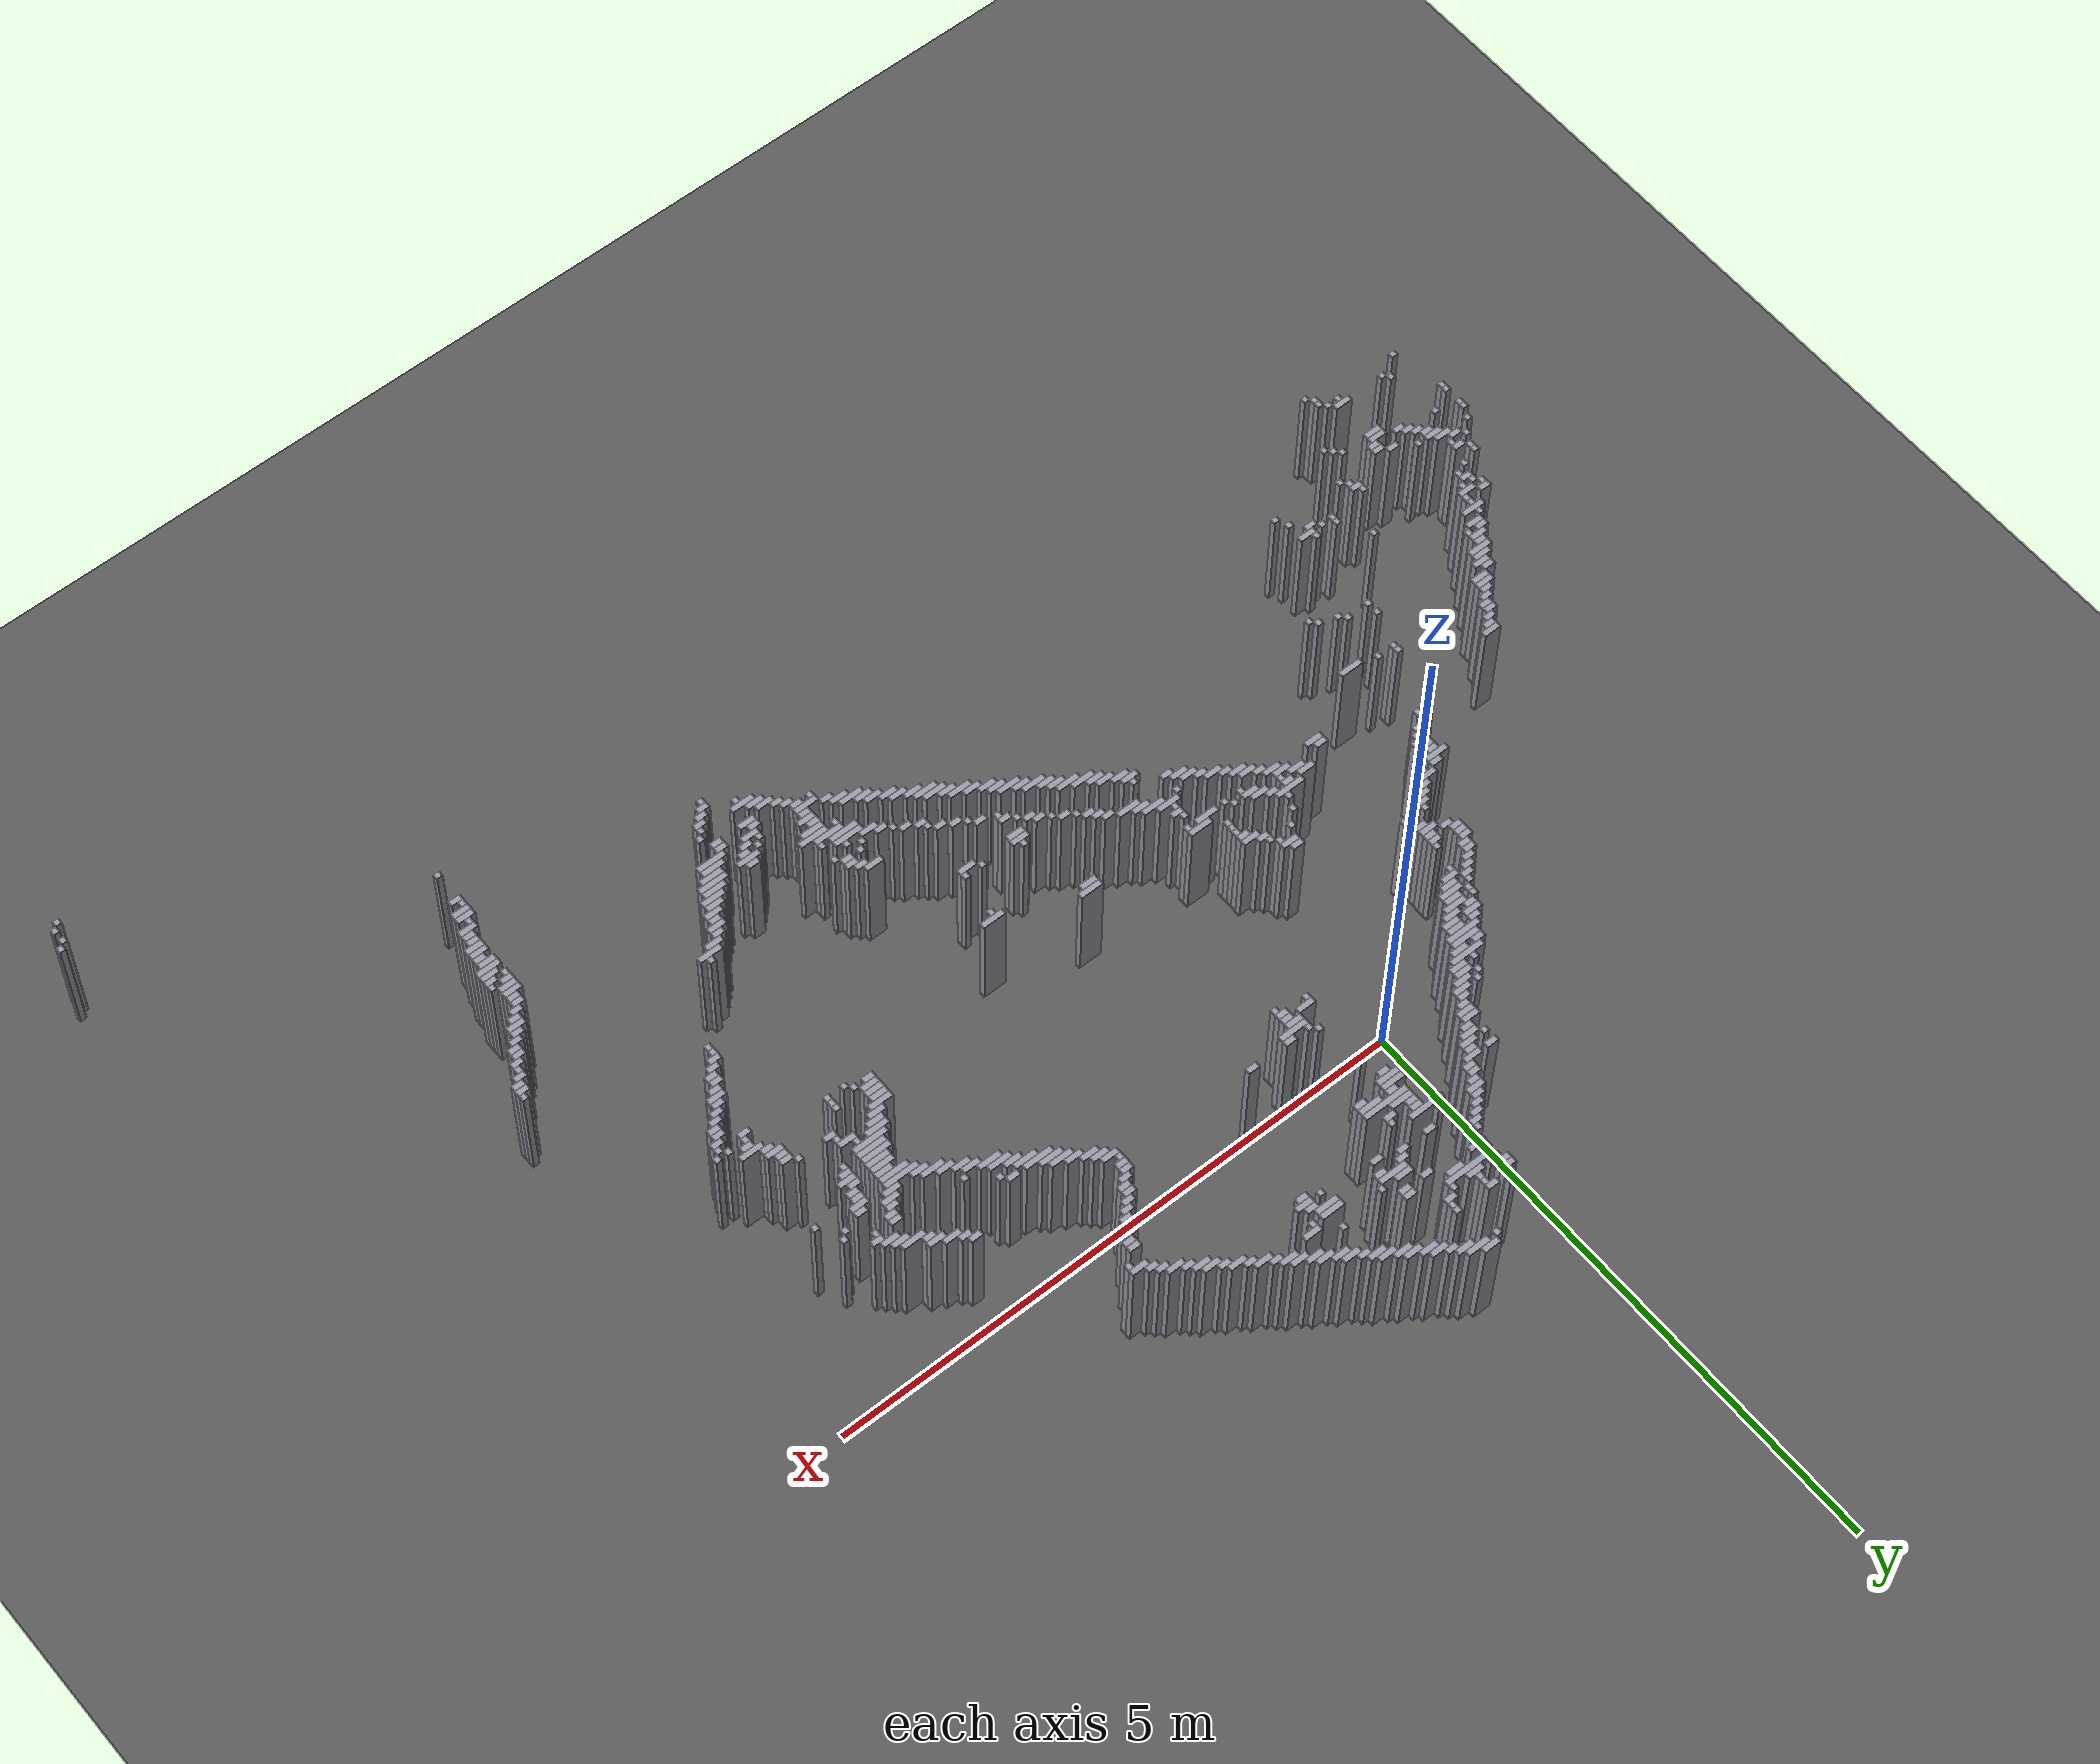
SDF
<?xml version="1.0"?>
<sdf version="1.8">
  <world name="dimi">
    <physics name="1ms" type="ignored">
      <max_step_size>0.004</max_step_size>
      <real_time_factor>1.0</real_time_factor>
    </physics>
    <plugin filename="gz-sim-physics-system" name="gz::sim::systems::Physics"/>
    <plugin filename="gz-sim-user-commands-system" name="gz::sim::systems::UserCommands"/>
    <plugin filename="gz-sim-scene-broadcaster-system" name="gz::sim::systems::SceneBroadcaster"/>
    <plugin filename="gz-sim-sensors-system" name="gz::sim::systems::Sensors">
      <render_engine>ogre2</render_engine>
    </plugin>

    <light type="directional" name="sun">
      <cast_shadows>false</cast_shadows>
      <pose>0 0 10 0 0 0</pose>
      <diffuse>0.9 0.9 0.9 1</diffuse>
      <direction>-0.3 0.2 -1</direction>
    </light>

    <model name="ground">
      <static>true</static>
      <link name="ground_link">
        <collision name="c"><geometry><plane><normal>0 0 1</normal><size>60 60</size></plane></geometry></collision>
        <visual name="v"><geometry><plane><normal>0 0 1</normal><size>60 60</size></plane></geometry>
          <material><ambient>0.3 0.3 0.3 1</ambient><diffuse>0.35 0.35 0.35 1</diffuse></material>
        </visual>
      </link>
    </model>

    <model name="walls">
      <static>true</static>
      <link name="wall_0">
        <pose>0.8850 2.0550 0.5000 0 0 0</pose>
        <collision name="c">
          <geometry><box><size>0.1500 0.0500 1.0000</size></box></geometry>
        </collision>
        <visual name="v">
          <geometry><box><size>0.1500 0.0500 1.0000</size></box></geometry>
          <material><ambient>0.5 0.5 0.55 1</ambient><diffuse>0.6 0.6 0.65 1</diffuse></material>
        </visual>
      </link>
      <link name="wall_1">
        <pose>0.7850 2.0050 0.5000 0 0 0</pose>
        <collision name="c">
          <geometry><box><size>0.0500 0.0500 1.0000</size></box></geometry>
        </collision>
        <visual name="v">
          <geometry><box><size>0.0500 0.0500 1.0000</size></box></geometry>
          <material><ambient>0.5 0.5 0.55 1</ambient><diffuse>0.6 0.6 0.65 1</diffuse></material>
        </visual>
      </link>
      <link name="wall_2">
        <pose>0.9600 2.0050 0.5000 0 0 0</pose>
        <collision name="c">
          <geometry><box><size>0.2000 0.0500 1.0000</size></box></geometry>
        </collision>
        <visual name="v">
          <geometry><box><size>0.2000 0.0500 1.0000</size></box></geometry>
          <material><ambient>0.5 0.5 0.55 1</ambient><diffuse>0.6 0.6 0.65 1</diffuse></material>
        </visual>
      </link>
      <link name="wall_3">
        <pose>1.0350 1.9550 0.5000 0 0 0</pose>
        <collision name="c">
          <geometry><box><size>0.1500 0.0500 1.0000</size></box></geometry>
        </collision>
        <visual name="v">
          <geometry><box><size>0.1500 0.0500 1.0000</size></box></geometry>
          <material><ambient>0.5 0.5 0.55 1</ambient><diffuse>0.6 0.6 0.65 1</diffuse></material>
        </visual>
      </link>
      <link name="wall_4">
        <pose>1.1100 1.9050 0.5000 0 0 0</pose>
        <collision name="c">
          <geometry><box><size>0.1000 0.0500 1.0000</size></box></geometry>
        </collision>
        <visual name="v">
          <geometry><box><size>0.1000 0.0500 1.0000</size></box></geometry>
          <material><ambient>0.5 0.5 0.55 1</ambient><diffuse>0.6 0.6 0.65 1</diffuse></material>
        </visual>
      </link>
      <link name="wall_5">
        <pose>1.1850 1.8550 0.5000 0 0 0</pose>
        <collision name="c">
          <geometry><box><size>0.1500 0.0500 1.0000</size></box></geometry>
        </collision>
        <visual name="v">
          <geometry><box><size>0.1500 0.0500 1.0000</size></box></geometry>
          <material><ambient>0.5 0.5 0.55 1</ambient><diffuse>0.6 0.6 0.65 1</diffuse></material>
        </visual>
      </link>
      <link name="wall_6">
        <pose>1.2350 1.8050 0.5000 0 0 0</pose>
        <collision name="c">
          <geometry><box><size>0.1500 0.0500 1.0000</size></box></geometry>
        </collision>
        <visual name="v">
          <geometry><box><size>0.1500 0.0500 1.0000</size></box></geometry>
          <material><ambient>0.5 0.5 0.55 1</ambient><diffuse>0.6 0.6 0.65 1</diffuse></material>
        </visual>
      </link>
      <link name="wall_7">
        <pose>0.4350 1.7550 0.5000 0 0 0</pose>
        <collision name="c">
          <geometry><box><size>0.0500 0.0500 1.0000</size></box></geometry>
        </collision>
        <visual name="v">
          <geometry><box><size>0.0500 0.0500 1.0000</size></box></geometry>
          <material><ambient>0.5 0.5 0.55 1</ambient><diffuse>0.6 0.6 0.65 1</diffuse></material>
        </visual>
      </link>
      <link name="wall_8">
        <pose>1.3350 1.7550 0.5000 0 0 0</pose>
        <collision name="c">
          <geometry><box><size>0.1500 0.0500 1.0000</size></box></geometry>
        </collision>
        <visual name="v">
          <geometry><box><size>0.1500 0.0500 1.0000</size></box></geometry>
          <material><ambient>0.5 0.5 0.55 1</ambient><diffuse>0.6 0.6 0.65 1</diffuse></material>
        </visual>
      </link>
      <link name="wall_9">
        <pose>0.3850 1.7050 0.5000 0 0 0</pose>
        <collision name="c">
          <geometry><box><size>0.0500 0.0500 1.0000</size></box></geometry>
        </collision>
        <visual name="v">
          <geometry><box><size>0.0500 0.0500 1.0000</size></box></geometry>
          <material><ambient>0.5 0.5 0.55 1</ambient><diffuse>0.6 0.6 0.65 1</diffuse></material>
        </visual>
      </link>
      <link name="wall_10">
        <pose>0.5600 1.7050 0.5000 0 0 0</pose>
        <collision name="c">
          <geometry><box><size>0.1000 0.0500 1.0000</size></box></geometry>
        </collision>
        <visual name="v">
          <geometry><box><size>0.1000 0.0500 1.0000</size></box></geometry>
          <material><ambient>0.5 0.5 0.55 1</ambient><diffuse>0.6 0.6 0.65 1</diffuse></material>
        </visual>
      </link>
      <link name="wall_11">
        <pose>0.8850 1.7050 0.5000 0 0 0</pose>
        <collision name="c">
          <geometry><box><size>0.0500 0.0500 1.0000</size></box></geometry>
        </collision>
        <visual name="v">
          <geometry><box><size>0.0500 0.0500 1.0000</size></box></geometry>
          <material><ambient>0.5 0.5 0.55 1</ambient><diffuse>0.6 0.6 0.65 1</diffuse></material>
        </visual>
      </link>
      <link name="wall_12">
        <pose>1.3850 1.7050 0.5000 0 0 0</pose>
        <collision name="c">
          <geometry><box><size>0.1500 0.0500 1.0000</size></box></geometry>
        </collision>
        <visual name="v">
          <geometry><box><size>0.1500 0.0500 1.0000</size></box></geometry>
          <material><ambient>0.5 0.5 0.55 1</ambient><diffuse>0.6 0.6 0.65 1</diffuse></material>
        </visual>
      </link>
      <link name="wall_13">
        <pose>0.3600 1.6550 0.5000 0 0 0</pose>
        <collision name="c">
          <geometry><box><size>0.1000 0.0500 1.0000</size></box></geometry>
        </collision>
        <visual name="v">
          <geometry><box><size>0.1000 0.0500 1.0000</size></box></geometry>
          <material><ambient>0.5 0.5 0.55 1</ambient><diffuse>0.6 0.6 0.65 1</diffuse></material>
        </visual>
      </link>
      <link name="wall_14">
        <pose>0.5850 1.6550 0.5000 0 0 0</pose>
        <collision name="c">
          <geometry><box><size>0.0500 0.0500 1.0000</size></box></geometry>
        </collision>
        <visual name="v">
          <geometry><box><size>0.0500 0.0500 1.0000</size></box></geometry>
          <material><ambient>0.5 0.5 0.55 1</ambient><diffuse>0.6 0.6 0.65 1</diffuse></material>
        </visual>
      </link>
      <link name="wall_15">
        <pose>0.8850 1.6550 0.5000 0 0 0</pose>
        <collision name="c">
          <geometry><box><size>0.0500 0.0500 1.0000</size></box></geometry>
        </collision>
        <visual name="v">
          <geometry><box><size>0.0500 0.0500 1.0000</size></box></geometry>
          <material><ambient>0.5 0.5 0.55 1</ambient><diffuse>0.6 0.6 0.65 1</diffuse></material>
        </visual>
      </link>
      <link name="wall_16">
        <pose>1.4850 1.6550 0.5000 0 0 0</pose>
        <collision name="c">
          <geometry><box><size>0.1500 0.0500 1.0000</size></box></geometry>
        </collision>
        <visual name="v">
          <geometry><box><size>0.1500 0.0500 1.0000</size></box></geometry>
          <material><ambient>0.5 0.5 0.55 1</ambient><diffuse>0.6 0.6 0.65 1</diffuse></material>
        </visual>
      </link>
      <link name="wall_17">
        <pose>0.3600 1.6050 0.5000 0 0 0</pose>
        <collision name="c">
          <geometry><box><size>0.1000 0.0500 1.0000</size></box></geometry>
        </collision>
        <visual name="v">
          <geometry><box><size>0.1000 0.0500 1.0000</size></box></geometry>
          <material><ambient>0.5 0.5 0.55 1</ambient><diffuse>0.6 0.6 0.65 1</diffuse></material>
        </visual>
      </link>
      <link name="wall_18">
        <pose>0.5850 1.6050 0.5000 0 0 0</pose>
        <collision name="c">
          <geometry><box><size>0.0500 0.0500 1.0000</size></box></geometry>
        </collision>
        <visual name="v">
          <geometry><box><size>0.0500 0.0500 1.0000</size></box></geometry>
          <material><ambient>0.5 0.5 0.55 1</ambient><diffuse>0.6 0.6 0.65 1</diffuse></material>
        </visual>
      </link>
      <link name="wall_19">
        <pose>0.8600 1.6050 0.5000 0 0 0</pose>
        <collision name="c">
          <geometry><box><size>0.1000 0.0500 1.0000</size></box></geometry>
        </collision>
        <visual name="v">
          <geometry><box><size>0.1000 0.0500 1.0000</size></box></geometry>
          <material><ambient>0.5 0.5 0.55 1</ambient><diffuse>0.6 0.6 0.65 1</diffuse></material>
        </visual>
      </link>
      <link name="wall_20">
        <pose>1.5350 1.6050 0.5000 0 0 0</pose>
        <collision name="c">
          <geometry><box><size>0.1500 0.0500 1.0000</size></box></geometry>
        </collision>
        <visual name="v">
          <geometry><box><size>0.1500 0.0500 1.0000</size></box></geometry>
          <material><ambient>0.5 0.5 0.55 1</ambient><diffuse>0.6 0.6 0.65 1</diffuse></material>
        </visual>
      </link>
      <link name="wall_21">
        <pose>0.4100 1.5550 0.5000 0 0 0</pose>
        <collision name="c">
          <geometry><box><size>0.1000 0.0500 1.0000</size></box></geometry>
        </collision>
        <visual name="v">
          <geometry><box><size>0.1000 0.0500 1.0000</size></box></geometry>
          <material><ambient>0.5 0.5 0.55 1</ambient><diffuse>0.6 0.6 0.65 1</diffuse></material>
        </visual>
      </link>
      <link name="wall_22">
        <pose>0.5850 1.5550 0.5000 0 0 0</pose>
        <collision name="c">
          <geometry><box><size>0.1500 0.0500 1.0000</size></box></geometry>
        </collision>
        <visual name="v">
          <geometry><box><size>0.1500 0.0500 1.0000</size></box></geometry>
          <material><ambient>0.5 0.5 0.55 1</ambient><diffuse>0.6 0.6 0.65 1</diffuse></material>
        </visual>
      </link>
      <link name="wall_23">
        <pose>0.7850 1.5550 0.5000 0 0 0</pose>
        <collision name="c">
          <geometry><box><size>0.0500 0.0500 1.0000</size></box></geometry>
        </collision>
        <visual name="v">
          <geometry><box><size>0.0500 0.0500 1.0000</size></box></geometry>
          <material><ambient>0.5 0.5 0.55 1</ambient><diffuse>0.6 0.6 0.65 1</diffuse></material>
        </visual>
      </link>
      <link name="wall_24">
        <pose>1.6100 1.5550 0.5000 0 0 0</pose>
        <collision name="c">
          <geometry><box><size>0.1000 0.0500 1.0000</size></box></geometry>
        </collision>
        <visual name="v">
          <geometry><box><size>0.1000 0.0500 1.0000</size></box></geometry>
          <material><ambient>0.5 0.5 0.55 1</ambient><diffuse>0.6 0.6 0.65 1</diffuse></material>
        </visual>
      </link>
      <link name="wall_25">
        <pose>0.6100 1.5050 0.5000 0 0 0</pose>
        <collision name="c">
          <geometry><box><size>0.4000 0.0500 1.0000</size></box></geometry>
        </collision>
        <visual name="v">
          <geometry><box><size>0.4000 0.0500 1.0000</size></box></geometry>
          <material><ambient>0.5 0.5 0.55 1</ambient><diffuse>0.6 0.6 0.65 1</diffuse></material>
        </visual>
      </link>
      <link name="wall_26">
        <pose>1.6850 1.5050 0.5000 0 0 0</pose>
        <collision name="c">
          <geometry><box><size>0.1500 0.0500 1.0000</size></box></geometry>
        </collision>
        <visual name="v">
          <geometry><box><size>0.1500 0.0500 1.0000</size></box></geometry>
          <material><ambient>0.5 0.5 0.55 1</ambient><diffuse>0.6 0.6 0.65 1</diffuse></material>
        </visual>
      </link>
      <link name="wall_27">
        <pose>0.3850 1.4550 0.5000 0 0 0</pose>
        <collision name="c">
          <geometry><box><size>0.0500 0.0500 1.0000</size></box></geometry>
        </collision>
        <visual name="v">
          <geometry><box><size>0.0500 0.0500 1.0000</size></box></geometry>
          <material><ambient>0.5 0.5 0.55 1</ambient><diffuse>0.6 0.6 0.65 1</diffuse></material>
        </visual>
      </link>
      <link name="wall_28">
        <pose>0.6850 1.4550 0.5000 0 0 0</pose>
        <collision name="c">
          <geometry><box><size>0.1500 0.0500 1.0000</size></box></geometry>
        </collision>
        <visual name="v">
          <geometry><box><size>0.1500 0.0500 1.0000</size></box></geometry>
          <material><ambient>0.5 0.5 0.55 1</ambient><diffuse>0.6 0.6 0.65 1</diffuse></material>
        </visual>
      </link>
      <link name="wall_29">
        <pose>1.7350 1.4550 0.5000 0 0 0</pose>
        <collision name="c">
          <geometry><box><size>0.1500 0.0500 1.0000</size></box></geometry>
        </collision>
        <visual name="v">
          <geometry><box><size>0.1500 0.0500 1.0000</size></box></geometry>
          <material><ambient>0.5 0.5 0.55 1</ambient><diffuse>0.6 0.6 0.65 1</diffuse></material>
        </visual>
      </link>
      <link name="wall_30">
        <pose>0.4350 1.4050 0.5000 0 0 0</pose>
        <collision name="c">
          <geometry><box><size>0.1500 0.0500 1.0000</size></box></geometry>
        </collision>
        <visual name="v">
          <geometry><box><size>0.1500 0.0500 1.0000</size></box></geometry>
          <material><ambient>0.5 0.5 0.55 1</ambient><diffuse>0.6 0.6 0.65 1</diffuse></material>
        </visual>
      </link>
      <link name="wall_31">
        <pose>1.0600 1.4050 0.5000 0 0 0</pose>
        <collision name="c">
          <geometry><box><size>0.1000 0.0500 1.0000</size></box></geometry>
        </collision>
        <visual name="v">
          <geometry><box><size>0.1000 0.0500 1.0000</size></box></geometry>
          <material><ambient>0.5 0.5 0.55 1</ambient><diffuse>0.6 0.6 0.65 1</diffuse></material>
        </visual>
      </link>
      <link name="wall_32">
        <pose>1.8350 1.4050 0.5000 0 0 0</pose>
        <collision name="c">
          <geometry><box><size>0.1500 0.0500 1.0000</size></box></geometry>
        </collision>
        <visual name="v">
          <geometry><box><size>0.1500 0.0500 1.0000</size></box></geometry>
          <material><ambient>0.5 0.5 0.55 1</ambient><diffuse>0.6 0.6 0.65 1</diffuse></material>
        </visual>
      </link>
      <link name="wall_33">
        <pose>0.8600 1.3550 0.5000 0 0 0</pose>
        <collision name="c">
          <geometry><box><size>0.1000 0.0500 1.0000</size></box></geometry>
        </collision>
        <visual name="v">
          <geometry><box><size>0.1000 0.0500 1.0000</size></box></geometry>
          <material><ambient>0.5 0.5 0.55 1</ambient><diffuse>0.6 0.6 0.65 1</diffuse></material>
        </visual>
      </link>
      <link name="wall_34">
        <pose>1.0600 1.3550 0.5000 0 0 0</pose>
        <collision name="c">
          <geometry><box><size>0.1000 0.0500 1.0000</size></box></geometry>
        </collision>
        <visual name="v">
          <geometry><box><size>0.1000 0.0500 1.0000</size></box></geometry>
          <material><ambient>0.5 0.5 0.55 1</ambient><diffuse>0.6 0.6 0.65 1</diffuse></material>
        </visual>
      </link>
      <link name="wall_35">
        <pose>1.8850 1.3550 0.5000 0 0 0</pose>
        <collision name="c">
          <geometry><box><size>0.1500 0.0500 1.0000</size></box></geometry>
        </collision>
        <visual name="v">
          <geometry><box><size>0.1500 0.0500 1.0000</size></box></geometry>
          <material><ambient>0.5 0.5 0.55 1</ambient><diffuse>0.6 0.6 0.65 1</diffuse></material>
        </visual>
      </link>
      <link name="wall_36">
        <pose>0.3350 1.3050 0.5000 0 0 0</pose>
        <collision name="c">
          <geometry><box><size>0.0500 0.0500 1.0000</size></box></geometry>
        </collision>
        <visual name="v">
          <geometry><box><size>0.0500 0.0500 1.0000</size></box></geometry>
          <material><ambient>0.5 0.5 0.55 1</ambient><diffuse>0.6 0.6 0.65 1</diffuse></material>
        </visual>
      </link>
      <link name="wall_37">
        <pose>1.5850 1.3050 0.5000 0 0 0</pose>
        <collision name="c">
          <geometry><box><size>0.0500 0.0500 1.0000</size></box></geometry>
        </collision>
        <visual name="v">
          <geometry><box><size>0.0500 0.0500 1.0000</size></box></geometry>
          <material><ambient>0.5 0.5 0.55 1</ambient><diffuse>0.6 0.6 0.65 1</diffuse></material>
        </visual>
      </link>
      <link name="wall_38">
        <pose>1.9850 1.3050 0.5000 0 0 0</pose>
        <collision name="c">
          <geometry><box><size>0.1500 0.0500 1.0000</size></box></geometry>
        </collision>
        <visual name="v">
          <geometry><box><size>0.1500 0.0500 1.0000</size></box></geometry>
          <material><ambient>0.5 0.5 0.55 1</ambient><diffuse>0.6 0.6 0.65 1</diffuse></material>
        </visual>
      </link>
      <link name="wall_39">
        <pose>0.3100 1.2550 0.5000 0 0 0</pose>
        <collision name="c">
          <geometry><box><size>0.1000 0.0500 1.0000</size></box></geometry>
        </collision>
        <visual name="v">
          <geometry><box><size>0.1000 0.0500 1.0000</size></box></geometry>
          <material><ambient>0.5 0.5 0.55 1</ambient><diffuse>0.6 0.6 0.65 1</diffuse></material>
        </visual>
      </link>
      <link name="wall_40">
        <pose>0.9850 1.2550 0.5000 0 0 0</pose>
        <collision name="c">
          <geometry><box><size>0.1500 0.0500 1.0000</size></box></geometry>
        </collision>
        <visual name="v">
          <geometry><box><size>0.1500 0.0500 1.0000</size></box></geometry>
          <material><ambient>0.5 0.5 0.55 1</ambient><diffuse>0.6 0.6 0.65 1</diffuse></material>
        </visual>
      </link>
      <link name="wall_41">
        <pose>1.1850 1.2550 0.5000 0 0 0</pose>
        <collision name="c">
          <geometry><box><size>0.0500 0.0500 1.0000</size></box></geometry>
        </collision>
        <visual name="v">
          <geometry><box><size>0.0500 0.0500 1.0000</size></box></geometry>
          <material><ambient>0.5 0.5 0.55 1</ambient><diffuse>0.6 0.6 0.65 1</diffuse></material>
        </visual>
      </link>
      <link name="wall_42">
        <pose>2.0350 1.2550 0.5000 0 0 0</pose>
        <collision name="c">
          <geometry><box><size>0.1500 0.0500 1.0000</size></box></geometry>
        </collision>
        <visual name="v">
          <geometry><box><size>0.1500 0.0500 1.0000</size></box></geometry>
          <material><ambient>0.5 0.5 0.55 1</ambient><diffuse>0.6 0.6 0.65 1</diffuse></material>
        </visual>
      </link>
      <link name="wall_43">
        <pose>0.2600 1.2050 0.5000 0 0 0</pose>
        <collision name="c">
          <geometry><box><size>0.1000 0.0500 1.0000</size></box></geometry>
        </collision>
        <visual name="v">
          <geometry><box><size>0.1000 0.0500 1.0000</size></box></geometry>
          <material><ambient>0.5 0.5 0.55 1</ambient><diffuse>0.6 0.6 0.65 1</diffuse></material>
        </visual>
      </link>
      <link name="wall_44">
        <pose>1.0350 1.2050 0.5000 0 0 0</pose>
        <collision name="c">
          <geometry><box><size>0.2500 0.0500 1.0000</size></box></geometry>
        </collision>
        <visual name="v">
          <geometry><box><size>0.2500 0.0500 1.0000</size></box></geometry>
          <material><ambient>0.5 0.5 0.55 1</ambient><diffuse>0.6 0.6 0.65 1</diffuse></material>
        </visual>
      </link>
      <link name="wall_45">
        <pose>1.7850 1.2050 0.5000 0 0 0</pose>
        <collision name="c">
          <geometry><box><size>0.1500 0.0500 1.0000</size></box></geometry>
        </collision>
        <visual name="v">
          <geometry><box><size>0.1500 0.0500 1.0000</size></box></geometry>
          <material><ambient>0.5 0.5 0.55 1</ambient><diffuse>0.6 0.6 0.65 1</diffuse></material>
        </visual>
      </link>
      <link name="wall_46">
        <pose>2.1100 1.2050 0.5000 0 0 0</pose>
        <collision name="c">
          <geometry><box><size>0.1000 0.0500 1.0000</size></box></geometry>
        </collision>
        <visual name="v">
          <geometry><box><size>0.1000 0.0500 1.0000</size></box></geometry>
          <material><ambient>0.5 0.5 0.55 1</ambient><diffuse>0.6 0.6 0.65 1</diffuse></material>
        </visual>
      </link>
      <link name="wall_47">
        <pose>0.2100 1.1550 0.5000 0 0 0</pose>
        <collision name="c">
          <geometry><box><size>0.1000 0.0500 1.0000</size></box></geometry>
        </collision>
        <visual name="v">
          <geometry><box><size>0.1000 0.0500 1.0000</size></box></geometry>
          <material><ambient>0.5 0.5 0.55 1</ambient><diffuse>0.6 0.6 0.65 1</diffuse></material>
        </visual>
      </link>
      <link name="wall_48">
        <pose>0.9100 1.1550 0.5000 0 0 0</pose>
        <collision name="c">
          <geometry><box><size>0.1000 0.0500 1.0000</size></box></geometry>
        </collision>
        <visual name="v">
          <geometry><box><size>0.1000 0.0500 1.0000</size></box></geometry>
          <material><ambient>0.5 0.5 0.55 1</ambient><diffuse>0.6 0.6 0.65 1</diffuse></material>
        </visual>
      </link>
      <link name="wall_49">
        <pose>1.1100 1.1550 0.5000 0 0 0</pose>
        <collision name="c">
          <geometry><box><size>0.1000 0.0500 1.0000</size></box></geometry>
        </collision>
        <visual name="v">
          <geometry><box><size>0.1000 0.0500 1.0000</size></box></geometry>
          <material><ambient>0.5 0.5 0.55 1</ambient><diffuse>0.6 0.6 0.65 1</diffuse></material>
        </visual>
      </link>
      <link name="wall_50">
        <pose>1.5600 1.1550 0.5000 0 0 0</pose>
        <collision name="c">
          <geometry><box><size>0.2000 0.0500 1.0000</size></box></geometry>
        </collision>
        <visual name="v">
          <geometry><box><size>0.2000 0.0500 1.0000</size></box></geometry>
          <material><ambient>0.5 0.5 0.55 1</ambient><diffuse>0.6 0.6 0.65 1</diffuse></material>
        </visual>
      </link>
      <link name="wall_51">
        <pose>1.7350 1.1550 0.5000 0 0 0</pose>
        <collision name="c">
          <geometry><box><size>0.0500 0.0500 1.0000</size></box></geometry>
        </collision>
        <visual name="v">
          <geometry><box><size>0.0500 0.0500 1.0000</size></box></geometry>
          <material><ambient>0.5 0.5 0.55 1</ambient><diffuse>0.6 0.6 0.65 1</diffuse></material>
        </visual>
      </link>
      <link name="wall_52">
        <pose>2.1850 1.1550 0.5000 0 0 0</pose>
        <collision name="c">
          <geometry><box><size>0.1500 0.0500 1.0000</size></box></geometry>
        </collision>
        <visual name="v">
          <geometry><box><size>0.1500 0.0500 1.0000</size></box></geometry>
          <material><ambient>0.5 0.5 0.55 1</ambient><diffuse>0.6 0.6 0.65 1</diffuse></material>
        </visual>
      </link>
      <link name="wall_53">
        <pose>0.1600 1.1050 0.5000 0 0 0</pose>
        <collision name="c">
          <geometry><box><size>0.1000 0.0500 1.0000</size></box></geometry>
        </collision>
        <visual name="v">
          <geometry><box><size>0.1000 0.0500 1.0000</size></box></geometry>
          <material><ambient>0.5 0.5 0.55 1</ambient><diffuse>0.6 0.6 0.65 1</diffuse></material>
        </visual>
      </link>
      <link name="wall_54">
        <pose>0.6100 1.1050 0.5000 0 0 0</pose>
        <collision name="c">
          <geometry><box><size>0.1000 0.0500 1.0000</size></box></geometry>
        </collision>
        <visual name="v">
          <geometry><box><size>0.1000 0.0500 1.0000</size></box></geometry>
          <material><ambient>0.5 0.5 0.55 1</ambient><diffuse>0.6 0.6 0.65 1</diffuse></material>
        </visual>
      </link>
      <link name="wall_55">
        <pose>0.8600 1.1050 0.5000 0 0 0</pose>
        <collision name="c">
          <geometry><box><size>0.1000 0.0500 1.0000</size></box></geometry>
        </collision>
        <visual name="v">
          <geometry><box><size>0.1000 0.0500 1.0000</size></box></geometry>
          <material><ambient>0.5 0.5 0.55 1</ambient><diffuse>0.6 0.6 0.65 1</diffuse></material>
        </visual>
      </link>
      <link name="wall_56">
        <pose>1.5600 1.1050 0.5000 0 0 0</pose>
        <collision name="c">
          <geometry><box><size>0.2000 0.0500 1.0000</size></box></geometry>
        </collision>
        <visual name="v">
          <geometry><box><size>0.2000 0.0500 1.0000</size></box></geometry>
          <material><ambient>0.5 0.5 0.55 1</ambient><diffuse>0.6 0.6 0.65 1</diffuse></material>
        </visual>
      </link>
      <link name="wall_57">
        <pose>2.2600 1.1050 0.5000 0 0 0</pose>
        <collision name="c">
          <geometry><box><size>0.1000 0.0500 1.0000</size></box></geometry>
        </collision>
        <visual name="v">
          <geometry><box><size>0.1000 0.0500 1.0000</size></box></geometry>
          <material><ambient>0.5 0.5 0.55 1</ambient><diffuse>0.6 0.6 0.65 1</diffuse></material>
        </visual>
      </link>
      <link name="wall_58">
        <pose>0.1350 1.0550 0.5000 0 0 0</pose>
        <collision name="c">
          <geometry><box><size>0.1500 0.0500 1.0000</size></box></geometry>
        </collision>
        <visual name="v">
          <geometry><box><size>0.1500 0.0500 1.0000</size></box></geometry>
          <material><ambient>0.5 0.5 0.55 1</ambient><diffuse>0.6 0.6 0.65 1</diffuse></material>
        </visual>
      </link>
      <link name="wall_59">
        <pose>1.0600 1.0550 0.5000 0 0 0</pose>
        <collision name="c">
          <geometry><box><size>0.1000 0.0500 1.0000</size></box></geometry>
        </collision>
        <visual name="v">
          <geometry><box><size>0.1000 0.0500 1.0000</size></box></geometry>
          <material><ambient>0.5 0.5 0.55 1</ambient><diffuse>0.6 0.6 0.65 1</diffuse></material>
        </visual>
      </link>
      <link name="wall_60">
        <pose>1.6600 1.0550 0.5000 0 0 0</pose>
        <collision name="c">
          <geometry><box><size>0.1000 0.0500 1.0000</size></box></geometry>
        </collision>
        <visual name="v">
          <geometry><box><size>0.1000 0.0500 1.0000</size></box></geometry>
          <material><ambient>0.5 0.5 0.55 1</ambient><diffuse>0.6 0.6 0.65 1</diffuse></material>
        </visual>
      </link>
      <link name="wall_61">
        <pose>2.3350 1.0550 0.5000 0 0 0</pose>
        <collision name="c">
          <geometry><box><size>0.1500 0.0500 1.0000</size></box></geometry>
        </collision>
        <visual name="v">
          <geometry><box><size>0.1500 0.0500 1.0000</size></box></geometry>
          <material><ambient>0.5 0.5 0.55 1</ambient><diffuse>0.6 0.6 0.65 1</diffuse></material>
        </visual>
      </link>
      <link name="wall_62">
        <pose>0.1100 1.0050 0.5000 0 0 0</pose>
        <collision name="c">
          <geometry><box><size>0.1000 0.0500 1.0000</size></box></geometry>
        </collision>
        <visual name="v">
          <geometry><box><size>0.1000 0.0500 1.0000</size></box></geometry>
          <material><ambient>0.5 0.5 0.55 1</ambient><diffuse>0.6 0.6 0.65 1</diffuse></material>
        </visual>
      </link>
      <link name="wall_63">
        <pose>0.4350 1.0050 0.5000 0 0 0</pose>
        <collision name="c">
          <geometry><box><size>0.0500 0.0500 1.0000</size></box></geometry>
        </collision>
        <visual name="v">
          <geometry><box><size>0.0500 0.0500 1.0000</size></box></geometry>
          <material><ambient>0.5 0.5 0.55 1</ambient><diffuse>0.6 0.6 0.65 1</diffuse></material>
        </visual>
      </link>
      <link name="wall_64">
        <pose>1.5350 1.0050 0.5000 0 0 0</pose>
        <collision name="c">
          <geometry><box><size>0.0500 0.0500 1.0000</size></box></geometry>
        </collision>
        <visual name="v">
          <geometry><box><size>0.0500 0.0500 1.0000</size></box></geometry>
          <material><ambient>0.5 0.5 0.55 1</ambient><diffuse>0.6 0.6 0.65 1</diffuse></material>
        </visual>
      </link>
      <link name="wall_65">
        <pose>1.6850 1.0050 0.5000 0 0 0</pose>
        <collision name="c">
          <geometry><box><size>0.1500 0.0500 1.0000</size></box></geometry>
        </collision>
        <visual name="v">
          <geometry><box><size>0.1500 0.0500 1.0000</size></box></geometry>
          <material><ambient>0.5 0.5 0.55 1</ambient><diffuse>0.6 0.6 0.65 1</diffuse></material>
        </visual>
      </link>
      <link name="wall_66">
        <pose>2.4100 1.0050 0.5000 0 0 0</pose>
        <collision name="c">
          <geometry><box><size>0.1000 0.0500 1.0000</size></box></geometry>
        </collision>
        <visual name="v">
          <geometry><box><size>0.1000 0.0500 1.0000</size></box></geometry>
          <material><ambient>0.5 0.5 0.55 1</ambient><diffuse>0.6 0.6 0.65 1</diffuse></material>
        </visual>
      </link>
      <link name="wall_67">
        <pose>0.0600 0.9550 0.5000 0 0 0</pose>
        <collision name="c">
          <geometry><box><size>0.1000 0.0500 1.0000</size></box></geometry>
        </collision>
        <visual name="v">
          <geometry><box><size>0.1000 0.0500 1.0000</size></box></geometry>
          <material><ambient>0.5 0.5 0.55 1</ambient><diffuse>0.6 0.6 0.65 1</diffuse></material>
        </visual>
      </link>
      <link name="wall_68">
        <pose>0.5100 0.9550 0.5000 0 0 0</pose>
        <collision name="c">
          <geometry><box><size>0.3000 0.0500 1.0000</size></box></geometry>
        </collision>
        <visual name="v">
          <geometry><box><size>0.3000 0.0500 1.0000</size></box></geometry>
          <material><ambient>0.5 0.5 0.55 1</ambient><diffuse>0.6 0.6 0.65 1</diffuse></material>
        </visual>
      </link>
      <link name="wall_69">
        <pose>1.6600 0.9550 0.5000 0 0 0</pose>
        <collision name="c">
          <geometry><box><size>0.1000 0.0500 1.0000</size></box></geometry>
        </collision>
        <visual name="v">
          <geometry><box><size>0.1000 0.0500 1.0000</size></box></geometry>
          <material><ambient>0.5 0.5 0.55 1</ambient><diffuse>0.6 0.6 0.65 1</diffuse></material>
        </visual>
      </link>
      <link name="wall_70">
        <pose>2.4850 0.9550 0.5000 0 0 0</pose>
        <collision name="c">
          <geometry><box><size>0.1500 0.0500 1.0000</size></box></geometry>
        </collision>
        <visual name="v">
          <geometry><box><size>0.1500 0.0500 1.0000</size></box></geometry>
          <material><ambient>0.5 0.5 0.55 1</ambient><diffuse>0.6 0.6 0.65 1</diffuse></material>
        </visual>
      </link>
      <link name="wall_71">
        <pose>0.0600 0.9050 0.5000 0 0 0</pose>
        <collision name="c">
          <geometry><box><size>0.1000 0.0500 1.0000</size></box></geometry>
        </collision>
        <visual name="v">
          <geometry><box><size>0.1000 0.0500 1.0000</size></box></geometry>
          <material><ambient>0.5 0.5 0.55 1</ambient><diffuse>0.6 0.6 0.65 1</diffuse></material>
        </visual>
      </link>
      <link name="wall_72">
        <pose>0.5600 0.9050 0.5000 0 0 0</pose>
        <collision name="c">
          <geometry><box><size>0.1000 0.0500 1.0000</size></box></geometry>
        </collision>
        <visual name="v">
          <geometry><box><size>0.1000 0.0500 1.0000</size></box></geometry>
          <material><ambient>0.5 0.5 0.55 1</ambient><diffuse>0.6 0.6 0.65 1</diffuse></material>
        </visual>
      </link>
      <link name="wall_73">
        <pose>0.7850 0.9050 0.5000 0 0 0</pose>
        <collision name="c">
          <geometry><box><size>0.0500 0.0500 1.0000</size></box></geometry>
        </collision>
        <visual name="v">
          <geometry><box><size>0.0500 0.0500 1.0000</size></box></geometry>
          <material><ambient>0.5 0.5 0.55 1</ambient><diffuse>0.6 0.6 0.65 1</diffuse></material>
        </visual>
      </link>
      <link name="wall_74">
        <pose>2.5350 0.9050 0.5000 0 0 0</pose>
        <collision name="c">
          <geometry><box><size>0.1500 0.0500 1.0000</size></box></geometry>
        </collision>
        <visual name="v">
          <geometry><box><size>0.1500 0.0500 1.0000</size></box></geometry>
          <material><ambient>0.5 0.5 0.55 1</ambient><diffuse>0.6 0.6 0.65 1</diffuse></material>
        </visual>
      </link>
      <link name="wall_75">
        <pose>-0.1900 0.8550 0.5000 0 0 0</pose>
        <collision name="c">
          <geometry><box><size>0.1000 0.0500 1.0000</size></box></geometry>
        </collision>
        <visual name="v">
          <geometry><box><size>0.1000 0.0500 1.0000</size></box></geometry>
          <material><ambient>0.5 0.5 0.55 1</ambient><diffuse>0.6 0.6 0.65 1</diffuse></material>
        </visual>
      </link>
      <link name="wall_76">
        <pose>-0.0150 0.8550 0.5000 0 0 0</pose>
        <collision name="c">
          <geometry><box><size>0.1500 0.0500 1.0000</size></box></geometry>
        </collision>
        <visual name="v">
          <geometry><box><size>0.1500 0.0500 1.0000</size></box></geometry>
          <material><ambient>0.5 0.5 0.55 1</ambient><diffuse>0.6 0.6 0.65 1</diffuse></material>
        </visual>
      </link>
      <link name="wall_77">
        <pose>0.5600 0.8550 0.5000 0 0 0</pose>
        <collision name="c">
          <geometry><box><size>0.1000 0.0500 1.0000</size></box></geometry>
        </collision>
        <visual name="v">
          <geometry><box><size>0.1000 0.0500 1.0000</size></box></geometry>
          <material><ambient>0.5 0.5 0.55 1</ambient><diffuse>0.6 0.6 0.65 1</diffuse></material>
        </visual>
      </link>
      <link name="wall_78">
        <pose>0.7600 0.8550 0.5000 0 0 0</pose>
        <collision name="c">
          <geometry><box><size>0.1000 0.0500 1.0000</size></box></geometry>
        </collision>
        <visual name="v">
          <geometry><box><size>0.1000 0.0500 1.0000</size></box></geometry>
          <material><ambient>0.5 0.5 0.55 1</ambient><diffuse>0.6 0.6 0.65 1</diffuse></material>
        </visual>
      </link>
      <link name="wall_79">
        <pose>2.6100 0.8550 0.5000 0 0 0</pose>
        <collision name="c">
          <geometry><box><size>0.1000 0.0500 1.0000</size></box></geometry>
        </collision>
        <visual name="v">
          <geometry><box><size>0.1000 0.0500 1.0000</size></box></geometry>
          <material><ambient>0.5 0.5 0.55 1</ambient><diffuse>0.6 0.6 0.65 1</diffuse></material>
        </visual>
      </link>
      <link name="wall_80">
        <pose>-0.0400 0.8050 0.5000 0 0 0</pose>
        <collision name="c">
          <geometry><box><size>0.1000 0.0500 1.0000</size></box></geometry>
        </collision>
        <visual name="v">
          <geometry><box><size>0.1000 0.0500 1.0000</size></box></geometry>
          <material><ambient>0.5 0.5 0.55 1</ambient><diffuse>0.6 0.6 0.65 1</diffuse></material>
        </visual>
      </link>
      <link name="wall_81">
        <pose>0.6100 0.8050 0.5000 0 0 0</pose>
        <collision name="c">
          <geometry><box><size>0.2000 0.0500 1.0000</size></box></geometry>
        </collision>
        <visual name="v">
          <geometry><box><size>0.2000 0.0500 1.0000</size></box></geometry>
          <material><ambient>0.5 0.5 0.55 1</ambient><diffuse>0.6 0.6 0.65 1</diffuse></material>
        </visual>
      </link>
      <link name="wall_82">
        <pose>2.6850 0.8050 0.5000 0 0 0</pose>
        <collision name="c">
          <geometry><box><size>0.1500 0.0500 1.0000</size></box></geometry>
        </collision>
        <visual name="v">
          <geometry><box><size>0.1500 0.0500 1.0000</size></box></geometry>
          <material><ambient>0.5 0.5 0.55 1</ambient><diffuse>0.6 0.6 0.65 1</diffuse></material>
        </visual>
      </link>
      <link name="wall_83">
        <pose>-0.2150 0.7550 0.5000 0 0 0</pose>
        <collision name="c">
          <geometry><box><size>0.0500 0.0500 1.0000</size></box></geometry>
        </collision>
        <visual name="v">
          <geometry><box><size>0.0500 0.0500 1.0000</size></box></geometry>
          <material><ambient>0.5 0.5 0.55 1</ambient><diffuse>0.6 0.6 0.65 1</diffuse></material>
        </visual>
      </link>
      <link name="wall_84">
        <pose>-0.0650 0.7550 0.5000 0 0 0</pose>
        <collision name="c">
          <geometry><box><size>0.1500 0.0500 1.0000</size></box></geometry>
        </collision>
        <visual name="v">
          <geometry><box><size>0.1500 0.0500 1.0000</size></box></geometry>
          <material><ambient>0.5 0.5 0.55 1</ambient><diffuse>0.6 0.6 0.65 1</diffuse></material>
        </visual>
      </link>
      <link name="wall_85">
        <pose>0.7100 0.7550 0.5000 0 0 0</pose>
        <collision name="c">
          <geometry><box><size>0.4000 0.0500 1.0000</size></box></geometry>
        </collision>
        <visual name="v">
          <geometry><box><size>0.4000 0.0500 1.0000</size></box></geometry>
          <material><ambient>0.5 0.5 0.55 1</ambient><diffuse>0.6 0.6 0.65 1</diffuse></material>
        </visual>
      </link>
      <link name="wall_86">
        <pose>2.7600 0.7550 0.5000 0 0 0</pose>
        <collision name="c">
          <geometry><box><size>0.1000 0.0500 1.0000</size></box></geometry>
        </collision>
        <visual name="v">
          <geometry><box><size>0.1000 0.0500 1.0000</size></box></geometry>
          <material><ambient>0.5 0.5 0.55 1</ambient><diffuse>0.6 0.6 0.65 1</diffuse></material>
        </visual>
      </link>
      <link name="wall_87">
        <pose>-0.1150 0.7050 0.5000 0 0 0</pose>
        <collision name="c">
          <geometry><box><size>0.1500 0.0500 1.0000</size></box></geometry>
        </collision>
        <visual name="v">
          <geometry><box><size>0.1500 0.0500 1.0000</size></box></geometry>
          <material><ambient>0.5 0.5 0.55 1</ambient><diffuse>0.6 0.6 0.65 1</diffuse></material>
        </visual>
      </link>
      <link name="wall_88">
        <pose>0.6100 0.7050 0.5000 0 0 0</pose>
        <collision name="c">
          <geometry><box><size>0.1000 0.0500 1.0000</size></box></geometry>
        </collision>
        <visual name="v">
          <geometry><box><size>0.1000 0.0500 1.0000</size></box></geometry>
          <material><ambient>0.5 0.5 0.55 1</ambient><diffuse>0.6 0.6 0.65 1</diffuse></material>
        </visual>
      </link>
      <link name="wall_89">
        <pose>0.8100 0.7050 0.5000 0 0 0</pose>
        <collision name="c">
          <geometry><box><size>0.2000 0.0500 1.0000</size></box></geometry>
        </collision>
        <visual name="v">
          <geometry><box><size>0.2000 0.0500 1.0000</size></box></geometry>
          <material><ambient>0.5 0.5 0.55 1</ambient><diffuse>0.6 0.6 0.65 1</diffuse></material>
        </visual>
      </link>
      <link name="wall_90">
        <pose>2.8100 0.7050 0.5000 0 0 0</pose>
        <collision name="c">
          <geometry><box><size>0.1000 0.0500 1.0000</size></box></geometry>
        </collision>
        <visual name="v">
          <geometry><box><size>0.1000 0.0500 1.0000</size></box></geometry>
          <material><ambient>0.5 0.5 0.55 1</ambient><diffuse>0.6 0.6 0.65 1</diffuse></material>
        </visual>
      </link>
      <link name="wall_91">
        <pose>-0.1400 0.6550 0.5000 0 0 0</pose>
        <collision name="c">
          <geometry><box><size>0.1000 0.0500 1.0000</size></box></geometry>
        </collision>
        <visual name="v">
          <geometry><box><size>0.1000 0.0500 1.0000</size></box></geometry>
          <material><ambient>0.5 0.5 0.55 1</ambient><diffuse>0.6 0.6 0.65 1</diffuse></material>
        </visual>
      </link>
      <link name="wall_92">
        <pose>0.5600 0.6550 0.5000 0 0 0</pose>
        <collision name="c">
          <geometry><box><size>0.2000 0.0500 1.0000</size></box></geometry>
        </collision>
        <visual name="v">
          <geometry><box><size>0.2000 0.0500 1.0000</size></box></geometry>
          <material><ambient>0.5 0.5 0.55 1</ambient><diffuse>0.6 0.6 0.65 1</diffuse></material>
        </visual>
      </link>
      <link name="wall_93">
        <pose>0.8600 0.6550 0.5000 0 0 0</pose>
        <collision name="c">
          <geometry><box><size>0.1000 0.0500 1.0000</size></box></geometry>
        </collision>
        <visual name="v">
          <geometry><box><size>0.1000 0.0500 1.0000</size></box></geometry>
          <material><ambient>0.5 0.5 0.55 1</ambient><diffuse>0.6 0.6 0.65 1</diffuse></material>
        </visual>
      </link>
      <link name="wall_94">
        <pose>2.8850 0.6550 0.5000 0 0 0</pose>
        <collision name="c">
          <geometry><box><size>0.1500 0.0500 1.0000</size></box></geometry>
        </collision>
        <visual name="v">
          <geometry><box><size>0.1500 0.0500 1.0000</size></box></geometry>
          <material><ambient>0.5 0.5 0.55 1</ambient><diffuse>0.6 0.6 0.65 1</diffuse></material>
        </visual>
      </link>
      <link name="wall_95">
        <pose>-0.2150 0.6050 0.5000 0 0 0</pose>
        <collision name="c">
          <geometry><box><size>0.1500 0.0500 1.0000</size></box></geometry>
        </collision>
        <visual name="v">
          <geometry><box><size>0.1500 0.0500 1.0000</size></box></geometry>
          <material><ambient>0.5 0.5 0.55 1</ambient><diffuse>0.6 0.6 0.65 1</diffuse></material>
        </visual>
      </link>
      <link name="wall_96">
        <pose>0.5600 0.6050 0.5000 0 0 0</pose>
        <collision name="c">
          <geometry><box><size>0.2000 0.0500 1.0000</size></box></geometry>
        </collision>
        <visual name="v">
          <geometry><box><size>0.2000 0.0500 1.0000</size></box></geometry>
          <material><ambient>0.5 0.5 0.55 1</ambient><diffuse>0.6 0.6 0.65 1</diffuse></material>
        </visual>
      </link>
      <link name="wall_97">
        <pose>2.9350 0.6050 0.5000 0 0 0</pose>
        <collision name="c">
          <geometry><box><size>0.0500 0.0500 1.0000</size></box></geometry>
        </collision>
        <visual name="v">
          <geometry><box><size>0.0500 0.0500 1.0000</size></box></geometry>
          <material><ambient>0.5 0.5 0.55 1</ambient><diffuse>0.6 0.6 0.65 1</diffuse></material>
        </visual>
      </link>
      <link name="wall_98">
        <pose>-0.2150 0.5550 0.5000 0 0 0</pose>
        <collision name="c">
          <geometry><box><size>0.1500 0.0500 1.0000</size></box></geometry>
        </collision>
        <visual name="v">
          <geometry><box><size>0.1500 0.0500 1.0000</size></box></geometry>
          <material><ambient>0.5 0.5 0.55 1</ambient><diffuse>0.6 0.6 0.65 1</diffuse></material>
        </visual>
      </link>
      <link name="wall_99">
        <pose>0.5600 0.5550 0.5000 0 0 0</pose>
        <collision name="c">
          <geometry><box><size>0.1000 0.0500 1.0000</size></box></geometry>
        </collision>
        <visual name="v">
          <geometry><box><size>0.1000 0.0500 1.0000</size></box></geometry>
          <material><ambient>0.5 0.5 0.55 1</ambient><diffuse>0.6 0.6 0.65 1</diffuse></material>
        </visual>
      </link>
      <link name="wall_100">
        <pose>-0.2400 0.5050 0.5000 0 0 0</pose>
        <collision name="c">
          <geometry><box><size>0.1000 0.0500 1.0000</size></box></geometry>
        </collision>
        <visual name="v">
          <geometry><box><size>0.1000 0.0500 1.0000</size></box></geometry>
          <material><ambient>0.5 0.5 0.55 1</ambient><diffuse>0.6 0.6 0.65 1</diffuse></material>
        </visual>
      </link>
      <link name="wall_101">
        <pose>2.8100 0.5050 0.5000 0 0 0</pose>
        <collision name="c">
          <geometry><box><size>0.1000 0.0500 1.0000</size></box></geometry>
        </collision>
        <visual name="v">
          <geometry><box><size>0.1000 0.0500 1.0000</size></box></geometry>
          <material><ambient>0.5 0.5 0.55 1</ambient><diffuse>0.6 0.6 0.65 1</diffuse></material>
        </visual>
      </link>
      <link name="wall_102">
        <pose>-0.2900 0.4550 0.5000 0 0 0</pose>
        <collision name="c">
          <geometry><box><size>0.1000 0.0500 1.0000</size></box></geometry>
        </collision>
        <visual name="v">
          <geometry><box><size>0.1000 0.0500 1.0000</size></box></geometry>
          <material><ambient>0.5 0.5 0.55 1</ambient><diffuse>0.6 0.6 0.65 1</diffuse></material>
        </visual>
      </link>
      <link name="wall_103">
        <pose>2.8100 0.4550 0.5000 0 0 0</pose>
        <collision name="c">
          <geometry><box><size>0.1000 0.0500 1.0000</size></box></geometry>
        </collision>
        <visual name="v">
          <geometry><box><size>0.1000 0.0500 1.0000</size></box></geometry>
          <material><ambient>0.5 0.5 0.55 1</ambient><diffuse>0.6 0.6 0.65 1</diffuse></material>
        </visual>
      </link>
      <link name="wall_104">
        <pose>-0.4650 0.4050 0.5000 0 0 0</pose>
        <collision name="c">
          <geometry><box><size>0.0500 0.0500 1.0000</size></box></geometry>
        </collision>
        <visual name="v">
          <geometry><box><size>0.0500 0.0500 1.0000</size></box></geometry>
          <material><ambient>0.5 0.5 0.55 1</ambient><diffuse>0.6 0.6 0.65 1</diffuse></material>
        </visual>
      </link>
      <link name="wall_105">
        <pose>-0.3150 0.4050 0.5000 0 0 0</pose>
        <collision name="c">
          <geometry><box><size>0.1500 0.0500 1.0000</size></box></geometry>
        </collision>
        <visual name="v">
          <geometry><box><size>0.1500 0.0500 1.0000</size></box></geometry>
          <material><ambient>0.5 0.5 0.55 1</ambient><diffuse>0.6 0.6 0.65 1</diffuse></material>
        </visual>
      </link>
      <link name="wall_106">
        <pose>2.7600 0.4050 0.5000 0 0 0</pose>
        <collision name="c">
          <geometry><box><size>0.1000 0.0500 1.0000</size></box></geometry>
        </collision>
        <visual name="v">
          <geometry><box><size>0.1000 0.0500 1.0000</size></box></geometry>
          <material><ambient>0.5 0.5 0.55 1</ambient><diffuse>0.6 0.6 0.65 1</diffuse></material>
        </visual>
      </link>
      <link name="wall_107">
        <pose>-0.5150 0.3550 0.5000 0 0 0</pose>
        <collision name="c">
          <geometry><box><size>0.0500 0.0500 1.0000</size></box></geometry>
        </collision>
        <visual name="v">
          <geometry><box><size>0.0500 0.0500 1.0000</size></box></geometry>
          <material><ambient>0.5 0.5 0.55 1</ambient><diffuse>0.6 0.6 0.65 1</diffuse></material>
        </visual>
      </link>
      <link name="wall_108">
        <pose>-0.3650 0.3550 0.5000 0 0 0</pose>
        <collision name="c">
          <geometry><box><size>0.1500 0.0500 1.0000</size></box></geometry>
        </collision>
        <visual name="v">
          <geometry><box><size>0.1500 0.0500 1.0000</size></box></geometry>
          <material><ambient>0.5 0.5 0.55 1</ambient><diffuse>0.6 0.6 0.65 1</diffuse></material>
        </visual>
      </link>
      <link name="wall_109">
        <pose>0.5850 0.3550 0.5000 0 0 0</pose>
        <collision name="c">
          <geometry><box><size>0.0500 0.0500 1.0000</size></box></geometry>
        </collision>
        <visual name="v">
          <geometry><box><size>0.0500 0.0500 1.0000</size></box></geometry>
          <material><ambient>0.5 0.5 0.55 1</ambient><diffuse>0.6 0.6 0.65 1</diffuse></material>
        </visual>
      </link>
      <link name="wall_110">
        <pose>2.7350 0.3550 0.5000 0 0 0</pose>
        <collision name="c">
          <geometry><box><size>0.0500 0.0500 1.0000</size></box></geometry>
        </collision>
        <visual name="v">
          <geometry><box><size>0.0500 0.0500 1.0000</size></box></geometry>
          <material><ambient>0.5 0.5 0.55 1</ambient><diffuse>0.6 0.6 0.65 1</diffuse></material>
        </visual>
      </link>
      <link name="wall_111">
        <pose>-0.4150 0.3050 0.5000 0 0 0</pose>
        <collision name="c">
          <geometry><box><size>0.1500 0.0500 1.0000</size></box></geometry>
        </collision>
        <visual name="v">
          <geometry><box><size>0.1500 0.0500 1.0000</size></box></geometry>
          <material><ambient>0.5 0.5 0.55 1</ambient><diffuse>0.6 0.6 0.65 1</diffuse></material>
        </visual>
      </link>
      <link name="wall_112">
        <pose>2.7100 0.3050 0.5000 0 0 0</pose>
        <collision name="c">
          <geometry><box><size>0.1000 0.0500 1.0000</size></box></geometry>
        </collision>
        <visual name="v">
          <geometry><box><size>0.1000 0.0500 1.0000</size></box></geometry>
          <material><ambient>0.5 0.5 0.55 1</ambient><diffuse>0.6 0.6 0.65 1</diffuse></material>
        </visual>
      </link>
      <link name="wall_113">
        <pose>-0.5650 0.2550 0.5000 0 0 0</pose>
        <collision name="c">
          <geometry><box><size>0.0500 0.0500 1.0000</size></box></geometry>
        </collision>
        <visual name="v">
          <geometry><box><size>0.0500 0.0500 1.0000</size></box></geometry>
          <material><ambient>0.5 0.5 0.55 1</ambient><diffuse>0.6 0.6 0.65 1</diffuse></material>
        </visual>
      </link>
      <link name="wall_114">
        <pose>-0.4150 0.2550 0.5000 0 0 0</pose>
        <collision name="c">
          <geometry><box><size>0.1500 0.0500 1.0000</size></box></geometry>
        </collision>
        <visual name="v">
          <geometry><box><size>0.1500 0.0500 1.0000</size></box></geometry>
          <material><ambient>0.5 0.5 0.55 1</ambient><diffuse>0.6 0.6 0.65 1</diffuse></material>
        </visual>
      </link>
      <link name="wall_115">
        <pose>2.6600 0.2550 0.5000 0 0 0</pose>
        <collision name="c">
          <geometry><box><size>0.1000 0.0500 1.0000</size></box></geometry>
        </collision>
        <visual name="v">
          <geometry><box><size>0.1000 0.0500 1.0000</size></box></geometry>
          <material><ambient>0.5 0.5 0.55 1</ambient><diffuse>0.6 0.6 0.65 1</diffuse></material>
        </visual>
      </link>
      <link name="wall_116">
        <pose>-0.5400 0.2050 0.5000 0 0 0</pose>
        <collision name="c">
          <geometry><box><size>0.3000 0.0500 1.0000</size></box></geometry>
        </collision>
        <visual name="v">
          <geometry><box><size>0.3000 0.0500 1.0000</size></box></geometry>
          <material><ambient>0.5 0.5 0.55 1</ambient><diffuse>0.6 0.6 0.65 1</diffuse></material>
        </visual>
      </link>
      <link name="wall_117">
        <pose>2.6100 0.2050 0.5000 0 0 0</pose>
        <collision name="c">
          <geometry><box><size>0.1000 0.0500 1.0000</size></box></geometry>
        </collision>
        <visual name="v">
          <geometry><box><size>0.1000 0.0500 1.0000</size></box></geometry>
          <material><ambient>0.5 0.5 0.55 1</ambient><diffuse>0.6 0.6 0.65 1</diffuse></material>
        </visual>
      </link>
      <link name="wall_118">
        <pose>-0.6900 0.1550 0.5000 0 0 0</pose>
        <collision name="c">
          <geometry><box><size>0.1000 0.0500 1.0000</size></box></geometry>
        </collision>
        <visual name="v">
          <geometry><box><size>0.1000 0.0500 1.0000</size></box></geometry>
          <material><ambient>0.5 0.5 0.55 1</ambient><diffuse>0.6 0.6 0.65 1</diffuse></material>
        </visual>
      </link>
      <link name="wall_119">
        <pose>-0.5150 0.1550 0.5000 0 0 0</pose>
        <collision name="c">
          <geometry><box><size>0.1500 0.0500 1.0000</size></box></geometry>
        </collision>
        <visual name="v">
          <geometry><box><size>0.1500 0.0500 1.0000</size></box></geometry>
          <material><ambient>0.5 0.5 0.55 1</ambient><diffuse>0.6 0.6 0.65 1</diffuse></material>
        </visual>
      </link>
      <link name="wall_120">
        <pose>2.5600 0.1550 0.5000 0 0 0</pose>
        <collision name="c">
          <geometry><box><size>0.1000 0.0500 1.0000</size></box></geometry>
        </collision>
        <visual name="v">
          <geometry><box><size>0.1000 0.0500 1.0000</size></box></geometry>
          <material><ambient>0.5 0.5 0.55 1</ambient><diffuse>0.6 0.6 0.65 1</diffuse></material>
        </visual>
      </link>
      <link name="wall_121">
        <pose>-0.6150 0.1050 0.5000 0 0 0</pose>
        <collision name="c">
          <geometry><box><size>0.2500 0.0500 1.0000</size></box></geometry>
        </collision>
        <visual name="v">
          <geometry><box><size>0.2500 0.0500 1.0000</size></box></geometry>
          <material><ambient>0.5 0.5 0.55 1</ambient><diffuse>0.6 0.6 0.65 1</diffuse></material>
        </visual>
      </link>
      <link name="wall_122">
        <pose>2.5600 0.1050 0.5000 0 0 0</pose>
        <collision name="c">
          <geometry><box><size>0.1000 0.0500 1.0000</size></box></geometry>
        </collision>
        <visual name="v">
          <geometry><box><size>0.1000 0.0500 1.0000</size></box></geometry>
          <material><ambient>0.5 0.5 0.55 1</ambient><diffuse>0.6 0.6 0.65 1</diffuse></material>
        </visual>
      </link>
      <link name="wall_123">
        <pose>-0.6400 0.0550 0.5000 0 0 0</pose>
        <collision name="c">
          <geometry><box><size>0.3000 0.0500 1.0000</size></box></geometry>
        </collision>
        <visual name="v">
          <geometry><box><size>0.3000 0.0500 1.0000</size></box></geometry>
          <material><ambient>0.5 0.5 0.55 1</ambient><diffuse>0.6 0.6 0.65 1</diffuse></material>
        </visual>
      </link>
      <link name="wall_124">
        <pose>2.5100 0.0550 0.5000 0 0 0</pose>
        <collision name="c">
          <geometry><box><size>0.1000 0.0500 1.0000</size></box></geometry>
        </collision>
        <visual name="v">
          <geometry><box><size>0.1000 0.0500 1.0000</size></box></geometry>
          <material><ambient>0.5 0.5 0.55 1</ambient><diffuse>0.6 0.6 0.65 1</diffuse></material>
        </visual>
      </link>
      <link name="wall_125">
        <pose>-0.7900 0.0050 0.5000 0 0 0</pose>
        <collision name="c">
          <geometry><box><size>0.1000 0.0500 1.0000</size></box></geometry>
        </collision>
        <visual name="v">
          <geometry><box><size>0.1000 0.0500 1.0000</size></box></geometry>
          <material><ambient>0.5 0.5 0.55 1</ambient><diffuse>0.6 0.6 0.65 1</diffuse></material>
        </visual>
      </link>
      <link name="wall_126">
        <pose>-0.6150 0.0050 0.5000 0 0 0</pose>
        <collision name="c">
          <geometry><box><size>0.1500 0.0500 1.0000</size></box></geometry>
        </collision>
        <visual name="v">
          <geometry><box><size>0.1500 0.0500 1.0000</size></box></geometry>
          <material><ambient>0.5 0.5 0.55 1</ambient><diffuse>0.6 0.6 0.65 1</diffuse></material>
        </visual>
      </link>
      <link name="wall_127">
        <pose>0.6850 0.0050 0.5000 0 0 0</pose>
        <collision name="c">
          <geometry><box><size>0.0500 0.0500 1.0000</size></box></geometry>
        </collision>
        <visual name="v">
          <geometry><box><size>0.0500 0.0500 1.0000</size></box></geometry>
          <material><ambient>0.5 0.5 0.55 1</ambient><diffuse>0.6 0.6 0.65 1</diffuse></material>
        </visual>
      </link>
      <link name="wall_128">
        <pose>2.4600 0.0050 0.5000 0 0 0</pose>
        <collision name="c">
          <geometry><box><size>0.1000 0.0500 1.0000</size></box></geometry>
        </collision>
        <visual name="v">
          <geometry><box><size>0.1000 0.0500 1.0000</size></box></geometry>
          <material><ambient>0.5 0.5 0.55 1</ambient><diffuse>0.6 0.6 0.65 1</diffuse></material>
        </visual>
      </link>
      <link name="wall_129">
        <pose>-0.8150 -0.0450 0.5000 0 0 0</pose>
        <collision name="c">
          <geometry><box><size>0.1500 0.0500 1.0000</size></box></geometry>
        </collision>
        <visual name="v">
          <geometry><box><size>0.1500 0.0500 1.0000</size></box></geometry>
          <material><ambient>0.5 0.5 0.55 1</ambient><diffuse>0.6 0.6 0.65 1</diffuse></material>
        </visual>
      </link>
      <link name="wall_130">
        <pose>-0.6150 -0.0450 0.5000 0 0 0</pose>
        <collision name="c">
          <geometry><box><size>0.1500 0.0500 1.0000</size></box></geometry>
        </collision>
        <visual name="v">
          <geometry><box><size>0.1500 0.0500 1.0000</size></box></geometry>
          <material><ambient>0.5 0.5 0.55 1</ambient><diffuse>0.6 0.6 0.65 1</diffuse></material>
        </visual>
      </link>
      <link name="wall_131">
        <pose>0.7350 -0.0450 0.5000 0 0 0</pose>
        <collision name="c">
          <geometry><box><size>0.0500 0.0500 1.0000</size></box></geometry>
        </collision>
        <visual name="v">
          <geometry><box><size>0.0500 0.0500 1.0000</size></box></geometry>
          <material><ambient>0.5 0.5 0.55 1</ambient><diffuse>0.6 0.6 0.65 1</diffuse></material>
        </visual>
      </link>
      <link name="wall_132">
        <pose>0.9100 -0.0450 0.5000 0 0 0</pose>
        <collision name="c">
          <geometry><box><size>0.1000 0.0500 1.0000</size></box></geometry>
        </collision>
        <visual name="v">
          <geometry><box><size>0.1000 0.0500 1.0000</size></box></geometry>
          <material><ambient>0.5 0.5 0.55 1</ambient><diffuse>0.6 0.6 0.65 1</diffuse></material>
        </visual>
      </link>
      <link name="wall_133">
        <pose>1.2600 -0.0450 0.5000 0 0 0</pose>
        <collision name="c">
          <geometry><box><size>0.1000 0.0500 1.0000</size></box></geometry>
        </collision>
        <visual name="v">
          <geometry><box><size>0.1000 0.0500 1.0000</size></box></geometry>
          <material><ambient>0.5 0.5 0.55 1</ambient><diffuse>0.6 0.6 0.65 1</diffuse></material>
        </visual>
      </link>
      <link name="wall_134">
        <pose>2.4600 -0.0450 0.5000 0 0 0</pose>
        <collision name="c">
          <geometry><box><size>0.1000 0.0500 1.0000</size></box></geometry>
        </collision>
        <visual name="v">
          <geometry><box><size>0.1000 0.0500 1.0000</size></box></geometry>
          <material><ambient>0.5 0.5 0.55 1</ambient><diffuse>0.6 0.6 0.65 1</diffuse></material>
        </visual>
      </link>
      <link name="wall_135">
        <pose>-0.8400 -0.0950 0.5000 0 0 0</pose>
        <collision name="c">
          <geometry><box><size>0.1000 0.0500 1.0000</size></box></geometry>
        </collision>
        <visual name="v">
          <geometry><box><size>0.1000 0.0500 1.0000</size></box></geometry>
          <material><ambient>0.5 0.5 0.55 1</ambient><diffuse>0.6 0.6 0.65 1</diffuse></material>
        </visual>
      </link>
      <link name="wall_136">
        <pose>-0.6650 -0.0950 0.5000 0 0 0</pose>
        <collision name="c">
          <geometry><box><size>0.1500 0.0500 1.0000</size></box></geometry>
        </collision>
        <visual name="v">
          <geometry><box><size>0.1500 0.0500 1.0000</size></box></geometry>
          <material><ambient>0.5 0.5 0.55 1</ambient><diffuse>0.6 0.6 0.65 1</diffuse></material>
        </visual>
      </link>
      <link name="wall_137">
        <pose>0.8350 -0.0950 0.5000 0 0 0</pose>
        <collision name="c">
          <geometry><box><size>0.2500 0.0500 1.0000</size></box></geometry>
        </collision>
        <visual name="v">
          <geometry><box><size>0.2500 0.0500 1.0000</size></box></geometry>
          <material><ambient>0.5 0.5 0.55 1</ambient><diffuse>0.6 0.6 0.65 1</diffuse></material>
        </visual>
      </link>
      <link name="wall_138">
        <pose>2.4350 -0.0950 0.5000 0 0 0</pose>
        <collision name="c">
          <geometry><box><size>0.0500 0.0500 1.0000</size></box></geometry>
        </collision>
        <visual name="v">
          <geometry><box><size>0.0500 0.0500 1.0000</size></box></geometry>
          <material><ambient>0.5 0.5 0.55 1</ambient><diffuse>0.6 0.6 0.65 1</diffuse></material>
        </visual>
      </link>
      <link name="wall_139">
        <pose>-0.9150 -0.1450 0.5000 0 0 0</pose>
        <collision name="c">
          <geometry><box><size>0.0500 0.0500 1.0000</size></box></geometry>
        </collision>
        <visual name="v">
          <geometry><box><size>0.0500 0.0500 1.0000</size></box></geometry>
          <material><ambient>0.5 0.5 0.55 1</ambient><diffuse>0.6 0.6 0.65 1</diffuse></material>
        </visual>
      </link>
      <link name="wall_140">
        <pose>-0.7400 -0.1450 0.5000 0 0 0</pose>
        <collision name="c">
          <geometry><box><size>0.2000 0.0500 1.0000</size></box></geometry>
        </collision>
        <visual name="v">
          <geometry><box><size>0.2000 0.0500 1.0000</size></box></geometry>
          <material><ambient>0.5 0.5 0.55 1</ambient><diffuse>0.6 0.6 0.65 1</diffuse></material>
        </visual>
      </link>
      <link name="wall_141">
        <pose>0.7850 -0.1450 0.5000 0 0 0</pose>
        <collision name="c">
          <geometry><box><size>0.1500 0.0500 1.0000</size></box></geometry>
        </collision>
        <visual name="v">
          <geometry><box><size>0.1500 0.0500 1.0000</size></box></geometry>
          <material><ambient>0.5 0.5 0.55 1</ambient><diffuse>0.6 0.6 0.65 1</diffuse></material>
        </visual>
      </link>
      <link name="wall_142">
        <pose>2.4850 -0.1450 0.5000 0 0 0</pose>
        <collision name="c">
          <geometry><box><size>0.1500 0.0500 1.0000</size></box></geometry>
        </collision>
        <visual name="v">
          <geometry><box><size>0.1500 0.0500 1.0000</size></box></geometry>
          <material><ambient>0.5 0.5 0.55 1</ambient><diffuse>0.6 0.6 0.65 1</diffuse></material>
        </visual>
      </link>
      <link name="wall_143">
        <pose>-0.9150 -0.1950 0.5000 0 0 0</pose>
        <collision name="c">
          <geometry><box><size>0.0500 0.0500 1.0000</size></box></geometry>
        </collision>
        <visual name="v">
          <geometry><box><size>0.0500 0.0500 1.0000</size></box></geometry>
          <material><ambient>0.5 0.5 0.55 1</ambient><diffuse>0.6 0.6 0.65 1</diffuse></material>
        </visual>
      </link>
      <link name="wall_144">
        <pose>-0.7650 -0.1950 0.5000 0 0 0</pose>
        <collision name="c">
          <geometry><box><size>0.1500 0.0500 1.0000</size></box></geometry>
        </collision>
        <visual name="v">
          <geometry><box><size>0.1500 0.0500 1.0000</size></box></geometry>
          <material><ambient>0.5 0.5 0.55 1</ambient><diffuse>0.6 0.6 0.65 1</diffuse></material>
        </visual>
      </link>
      <link name="wall_145">
        <pose>0.6350 -0.1950 0.5000 0 0 0</pose>
        <collision name="c">
          <geometry><box><size>0.1500 0.0500 1.0000</size></box></geometry>
        </collision>
        <visual name="v">
          <geometry><box><size>0.1500 0.0500 1.0000</size></box></geometry>
          <material><ambient>0.5 0.5 0.55 1</ambient><diffuse>0.6 0.6 0.65 1</diffuse></material>
        </visual>
      </link>
      <link name="wall_146">
        <pose>0.8100 -0.1950 0.5000 0 0 0</pose>
        <collision name="c">
          <geometry><box><size>0.1000 0.0500 1.0000</size></box></geometry>
        </collision>
        <visual name="v">
          <geometry><box><size>0.1000 0.0500 1.0000</size></box></geometry>
          <material><ambient>0.5 0.5 0.55 1</ambient><diffuse>0.6 0.6 0.65 1</diffuse></material>
        </visual>
      </link>
      <link name="wall_147">
        <pose>2.5350 -0.1950 0.5000 0 0 0</pose>
        <collision name="c">
          <geometry><box><size>0.1500 0.0500 1.0000</size></box></geometry>
        </collision>
        <visual name="v">
          <geometry><box><size>0.1500 0.0500 1.0000</size></box></geometry>
          <material><ambient>0.5 0.5 0.55 1</ambient><diffuse>0.6 0.6 0.65 1</diffuse></material>
        </visual>
      </link>
      <link name="wall_148">
        <pose>-0.9650 -0.2450 0.5000 0 0 0</pose>
        <collision name="c">
          <geometry><box><size>0.0500 0.0500 1.0000</size></box></geometry>
        </collision>
        <visual name="v">
          <geometry><box><size>0.0500 0.0500 1.0000</size></box></geometry>
          <material><ambient>0.5 0.5 0.55 1</ambient><diffuse>0.6 0.6 0.65 1</diffuse></material>
        </visual>
      </link>
      <link name="wall_149">
        <pose>-0.7900 -0.2450 0.5000 0 0 0</pose>
        <collision name="c">
          <geometry><box><size>0.2000 0.0500 1.0000</size></box></geometry>
        </collision>
        <visual name="v">
          <geometry><box><size>0.2000 0.0500 1.0000</size></box></geometry>
          <material><ambient>0.5 0.5 0.55 1</ambient><diffuse>0.6 0.6 0.65 1</diffuse></material>
        </visual>
      </link>
      <link name="wall_150">
        <pose>0.5850 -0.2450 0.5000 0 0 0</pose>
        <collision name="c">
          <geometry><box><size>0.0500 0.0500 1.0000</size></box></geometry>
        </collision>
        <visual name="v">
          <geometry><box><size>0.0500 0.0500 1.0000</size></box></geometry>
          <material><ambient>0.5 0.5 0.55 1</ambient><diffuse>0.6 0.6 0.65 1</diffuse></material>
        </visual>
      </link>
      <link name="wall_151">
        <pose>0.8100 -0.2450 0.5000 0 0 0</pose>
        <collision name="c">
          <geometry><box><size>0.1000 0.0500 1.0000</size></box></geometry>
        </collision>
        <visual name="v">
          <geometry><box><size>0.1000 0.0500 1.0000</size></box></geometry>
          <material><ambient>0.5 0.5 0.55 1</ambient><diffuse>0.6 0.6 0.65 1</diffuse></material>
        </visual>
      </link>
      <link name="wall_152">
        <pose>2.5850 -0.2450 0.5000 0 0 0</pose>
        <collision name="c">
          <geometry><box><size>0.1500 0.0500 1.0000</size></box></geometry>
        </collision>
        <visual name="v">
          <geometry><box><size>0.1500 0.0500 1.0000</size></box></geometry>
          <material><ambient>0.5 0.5 0.55 1</ambient><diffuse>0.6 0.6 0.65 1</diffuse></material>
        </visual>
      </link>
      <link name="wall_153">
        <pose>3.6100 -0.2450 0.5000 0 0 0</pose>
        <collision name="c">
          <geometry><box><size>0.1000 0.0500 1.0000</size></box></geometry>
        </collision>
        <visual name="v">
          <geometry><box><size>0.1000 0.0500 1.0000</size></box></geometry>
          <material><ambient>0.5 0.5 0.55 1</ambient><diffuse>0.6 0.6 0.65 1</diffuse></material>
        </visual>
      </link>
      <link name="wall_154">
        <pose>-0.9900 -0.2950 0.5000 0 0 0</pose>
        <collision name="c">
          <geometry><box><size>0.1000 0.0500 1.0000</size></box></geometry>
        </collision>
        <visual name="v">
          <geometry><box><size>0.1000 0.0500 1.0000</size></box></geometry>
          <material><ambient>0.5 0.5 0.55 1</ambient><diffuse>0.6 0.6 0.65 1</diffuse></material>
        </visual>
      </link>
      <link name="wall_155">
        <pose>-0.8150 -0.2950 0.5000 0 0 0</pose>
        <collision name="c">
          <geometry><box><size>0.1500 0.0500 1.0000</size></box></geometry>
        </collision>
        <visual name="v">
          <geometry><box><size>0.1500 0.0500 1.0000</size></box></geometry>
          <material><ambient>0.5 0.5 0.55 1</ambient><diffuse>0.6 0.6 0.65 1</diffuse></material>
        </visual>
      </link>
      <link name="wall_156">
        <pose>0.8350 -0.2950 0.5000 0 0 0</pose>
        <collision name="c">
          <geometry><box><size>0.0500 0.0500 1.0000</size></box></geometry>
        </collision>
        <visual name="v">
          <geometry><box><size>0.0500 0.0500 1.0000</size></box></geometry>
          <material><ambient>0.5 0.5 0.55 1</ambient><diffuse>0.6 0.6 0.65 1</diffuse></material>
        </visual>
      </link>
      <link name="wall_157">
        <pose>2.6850 -0.2950 0.5000 0 0 0</pose>
        <collision name="c">
          <geometry><box><size>0.1500 0.0500 1.0000</size></box></geometry>
        </collision>
        <visual name="v">
          <geometry><box><size>0.1500 0.0500 1.0000</size></box></geometry>
          <material><ambient>0.5 0.5 0.55 1</ambient><diffuse>0.6 0.6 0.65 1</diffuse></material>
        </visual>
      </link>
      <link name="wall_158">
        <pose>3.6600 -0.2950 0.5000 0 0 0</pose>
        <collision name="c">
          <geometry><box><size>0.1000 0.0500 1.0000</size></box></geometry>
        </collision>
        <visual name="v">
          <geometry><box><size>0.1000 0.0500 1.0000</size></box></geometry>
          <material><ambient>0.5 0.5 0.55 1</ambient><diffuse>0.6 0.6 0.65 1</diffuse></material>
        </visual>
      </link>
      <link name="wall_159">
        <pose>-1.0400 -0.3450 0.5000 0 0 0</pose>
        <collision name="c">
          <geometry><box><size>0.1000 0.0500 1.0000</size></box></geometry>
        </collision>
        <visual name="v">
          <geometry><box><size>0.1000 0.0500 1.0000</size></box></geometry>
          <material><ambient>0.5 0.5 0.55 1</ambient><diffuse>0.6 0.6 0.65 1</diffuse></material>
        </visual>
      </link>
      <link name="wall_160">
        <pose>-0.8650 -0.3450 0.5000 0 0 0</pose>
        <collision name="c">
          <geometry><box><size>0.1500 0.0500 1.0000</size></box></geometry>
        </collision>
        <visual name="v">
          <geometry><box><size>0.1500 0.0500 1.0000</size></box></geometry>
          <material><ambient>0.5 0.5 0.55 1</ambient><diffuse>0.6 0.6 0.65 1</diffuse></material>
        </visual>
      </link>
      <link name="wall_161">
        <pose>2.7600 -0.3450 0.5000 0 0 0</pose>
        <collision name="c">
          <geometry><box><size>0.2000 0.0500 1.0000</size></box></geometry>
        </collision>
        <visual name="v">
          <geometry><box><size>0.2000 0.0500 1.0000</size></box></geometry>
          <material><ambient>0.5 0.5 0.55 1</ambient><diffuse>0.6 0.6 0.65 1</diffuse></material>
        </visual>
      </link>
      <link name="wall_162">
        <pose>3.7350 -0.3450 0.5000 0 0 0</pose>
        <collision name="c">
          <geometry><box><size>0.1500 0.0500 1.0000</size></box></geometry>
        </collision>
        <visual name="v">
          <geometry><box><size>0.1500 0.0500 1.0000</size></box></geometry>
          <material><ambient>0.5 0.5 0.55 1</ambient><diffuse>0.6 0.6 0.65 1</diffuse></material>
        </visual>
      </link>
      <link name="wall_163">
        <pose>-1.0900 -0.3950 0.5000 0 0 0</pose>
        <collision name="c">
          <geometry><box><size>0.1000 0.0500 1.0000</size></box></geometry>
        </collision>
        <visual name="v">
          <geometry><box><size>0.1000 0.0500 1.0000</size></box></geometry>
          <material><ambient>0.5 0.5 0.55 1</ambient><diffuse>0.6 0.6 0.65 1</diffuse></material>
        </visual>
      </link>
      <link name="wall_164">
        <pose>-0.9150 -0.3950 0.5000 0 0 0</pose>
        <collision name="c">
          <geometry><box><size>0.0500 0.0500 1.0000</size></box></geometry>
        </collision>
        <visual name="v">
          <geometry><box><size>0.0500 0.0500 1.0000</size></box></geometry>
          <material><ambient>0.5 0.5 0.55 1</ambient><diffuse>0.6 0.6 0.65 1</diffuse></material>
        </visual>
      </link>
      <link name="wall_165">
        <pose>2.8100 -0.3950 0.5000 0 0 0</pose>
        <collision name="c">
          <geometry><box><size>0.2000 0.0500 1.0000</size></box></geometry>
        </collision>
        <visual name="v">
          <geometry><box><size>0.2000 0.0500 1.0000</size></box></geometry>
          <material><ambient>0.5 0.5 0.55 1</ambient><diffuse>0.6 0.6 0.65 1</diffuse></material>
        </visual>
      </link>
      <link name="wall_166">
        <pose>3.8350 -0.3950 0.5000 0 0 0</pose>
        <collision name="c">
          <geometry><box><size>0.1500 0.0500 1.0000</size></box></geometry>
        </collision>
        <visual name="v">
          <geometry><box><size>0.1500 0.0500 1.0000</size></box></geometry>
          <material><ambient>0.5 0.5 0.55 1</ambient><diffuse>0.6 0.6 0.65 1</diffuse></material>
        </visual>
      </link>
      <link name="wall_167">
        <pose>-1.1400 -0.4450 0.5000 0 0 0</pose>
        <collision name="c">
          <geometry><box><size>0.1000 0.0500 1.0000</size></box></geometry>
        </collision>
        <visual name="v">
          <geometry><box><size>0.1000 0.0500 1.0000</size></box></geometry>
          <material><ambient>0.5 0.5 0.55 1</ambient><diffuse>0.6 0.6 0.65 1</diffuse></material>
        </visual>
      </link>
      <link name="wall_168">
        <pose>2.8850 -0.4450 0.5000 0 0 0</pose>
        <collision name="c">
          <geometry><box><size>0.2500 0.0500 1.0000</size></box></geometry>
        </collision>
        <visual name="v">
          <geometry><box><size>0.2500 0.0500 1.0000</size></box></geometry>
          <material><ambient>0.5 0.5 0.55 1</ambient><diffuse>0.6 0.6 0.65 1</diffuse></material>
        </visual>
      </link>
      <link name="wall_169">
        <pose>3.1100 -0.4450 0.5000 0 0 0</pose>
        <collision name="c">
          <geometry><box><size>0.1000 0.0500 1.0000</size></box></geometry>
        </collision>
        <visual name="v">
          <geometry><box><size>0.1000 0.0500 1.0000</size></box></geometry>
          <material><ambient>0.5 0.5 0.55 1</ambient><diffuse>0.6 0.6 0.65 1</diffuse></material>
        </visual>
      </link>
      <link name="wall_170">
        <pose>3.8600 -0.4450 0.5000 0 0 0</pose>
        <collision name="c">
          <geometry><box><size>0.1000 0.0500 1.0000</size></box></geometry>
        </collision>
        <visual name="v">
          <geometry><box><size>0.1000 0.0500 1.0000</size></box></geometry>
          <material><ambient>0.5 0.5 0.55 1</ambient><diffuse>0.6 0.6 0.65 1</diffuse></material>
        </visual>
      </link>
      <link name="wall_171">
        <pose>-1.1400 -0.4950 0.5000 0 0 0</pose>
        <collision name="c">
          <geometry><box><size>0.1000 0.0500 1.0000</size></box></geometry>
        </collision>
        <visual name="v">
          <geometry><box><size>0.1000 0.0500 1.0000</size></box></geometry>
          <material><ambient>0.5 0.5 0.55 1</ambient><diffuse>0.6 0.6 0.65 1</diffuse></material>
        </visual>
      </link>
      <link name="wall_172">
        <pose>2.9600 -0.4950 0.5000 0 0 0</pose>
        <collision name="c">
          <geometry><box><size>0.2000 0.0500 1.0000</size></box></geometry>
        </collision>
        <visual name="v">
          <geometry><box><size>0.2000 0.0500 1.0000</size></box></geometry>
          <material><ambient>0.5 0.5 0.55 1</ambient><diffuse>0.6 0.6 0.65 1</diffuse></material>
        </visual>
      </link>
      <link name="wall_173">
        <pose>3.1850 -0.4950 0.5000 0 0 0</pose>
        <collision name="c">
          <geometry><box><size>0.0500 0.0500 1.0000</size></box></geometry>
        </collision>
        <visual name="v">
          <geometry><box><size>0.0500 0.0500 1.0000</size></box></geometry>
          <material><ambient>0.5 0.5 0.55 1</ambient><diffuse>0.6 0.6 0.65 1</diffuse></material>
        </visual>
      </link>
      <link name="wall_174">
        <pose>3.9600 -0.4950 0.5000 0 0 0</pose>
        <collision name="c">
          <geometry><box><size>0.2000 0.0500 1.0000</size></box></geometry>
        </collision>
        <visual name="v">
          <geometry><box><size>0.2000 0.0500 1.0000</size></box></geometry>
          <material><ambient>0.5 0.5 0.55 1</ambient><diffuse>0.6 0.6 0.65 1</diffuse></material>
        </visual>
      </link>
      <link name="wall_175">
        <pose>-1.1900 -0.5450 0.5000 0 0 0</pose>
        <collision name="c">
          <geometry><box><size>0.1000 0.0500 1.0000</size></box></geometry>
        </collision>
        <visual name="v">
          <geometry><box><size>0.1000 0.0500 1.0000</size></box></geometry>
          <material><ambient>0.5 0.5 0.55 1</ambient><diffuse>0.6 0.6 0.65 1</diffuse></material>
        </visual>
      </link>
      <link name="wall_176">
        <pose>3.0350 -0.5450 0.5000 0 0 0</pose>
        <collision name="c">
          <geometry><box><size>0.1500 0.0500 1.0000</size></box></geometry>
        </collision>
        <visual name="v">
          <geometry><box><size>0.1500 0.0500 1.0000</size></box></geometry>
          <material><ambient>0.5 0.5 0.55 1</ambient><diffuse>0.6 0.6 0.65 1</diffuse></material>
        </visual>
      </link>
      <link name="wall_177">
        <pose>4.0350 -0.5450 0.5000 0 0 0</pose>
        <collision name="c">
          <geometry><box><size>0.1500 0.0500 1.0000</size></box></geometry>
        </collision>
        <visual name="v">
          <geometry><box><size>0.1500 0.0500 1.0000</size></box></geometry>
          <material><ambient>0.5 0.5 0.55 1</ambient><diffuse>0.6 0.6 0.65 1</diffuse></material>
        </visual>
      </link>
      <link name="wall_178">
        <pose>-1.1900 -0.5950 0.5000 0 0 0</pose>
        <collision name="c">
          <geometry><box><size>0.1000 0.0500 1.0000</size></box></geometry>
        </collision>
        <visual name="v">
          <geometry><box><size>0.1000 0.0500 1.0000</size></box></geometry>
          <material><ambient>0.5 0.5 0.55 1</ambient><diffuse>0.6 0.6 0.65 1</diffuse></material>
        </visual>
      </link>
      <link name="wall_179">
        <pose>-0.9650 -0.5950 0.5000 0 0 0</pose>
        <collision name="c">
          <geometry><box><size>0.0500 0.0500 1.0000</size></box></geometry>
        </collision>
        <visual name="v">
          <geometry><box><size>0.0500 0.0500 1.0000</size></box></geometry>
          <material><ambient>0.5 0.5 0.55 1</ambient><diffuse>0.6 0.6 0.65 1</diffuse></material>
        </visual>
      </link>
      <link name="wall_180">
        <pose>3.1100 -0.5950 0.5000 0 0 0</pose>
        <collision name="c">
          <geometry><box><size>0.2000 0.0500 1.0000</size></box></geometry>
        </collision>
        <visual name="v">
          <geometry><box><size>0.2000 0.0500 1.0000</size></box></geometry>
          <material><ambient>0.5 0.5 0.55 1</ambient><diffuse>0.6 0.6 0.65 1</diffuse></material>
        </visual>
      </link>
      <link name="wall_181">
        <pose>4.0850 -0.5950 0.5000 0 0 0</pose>
        <collision name="c">
          <geometry><box><size>0.1500 0.0500 1.0000</size></box></geometry>
        </collision>
        <visual name="v">
          <geometry><box><size>0.1500 0.0500 1.0000</size></box></geometry>
          <material><ambient>0.5 0.5 0.55 1</ambient><diffuse>0.6 0.6 0.65 1</diffuse></material>
        </visual>
      </link>
      <link name="wall_182">
        <pose>-1.1900 -0.6450 0.5000 0 0 0</pose>
        <collision name="c">
          <geometry><box><size>0.1000 0.0500 1.0000</size></box></geometry>
        </collision>
        <visual name="v">
          <geometry><box><size>0.1000 0.0500 1.0000</size></box></geometry>
          <material><ambient>0.5 0.5 0.55 1</ambient><diffuse>0.6 0.6 0.65 1</diffuse></material>
        </visual>
      </link>
      <link name="wall_183">
        <pose>-0.9900 -0.6450 0.5000 0 0 0</pose>
        <collision name="c">
          <geometry><box><size>0.1000 0.0500 1.0000</size></box></geometry>
        </collision>
        <visual name="v">
          <geometry><box><size>0.1000 0.0500 1.0000</size></box></geometry>
          <material><ambient>0.5 0.5 0.55 1</ambient><diffuse>0.6 0.6 0.65 1</diffuse></material>
        </visual>
      </link>
      <link name="wall_184">
        <pose>3.1600 -0.6450 0.5000 0 0 0</pose>
        <collision name="c">
          <geometry><box><size>0.2000 0.0500 1.0000</size></box></geometry>
        </collision>
        <visual name="v">
          <geometry><box><size>0.2000 0.0500 1.0000</size></box></geometry>
          <material><ambient>0.5 0.5 0.55 1</ambient><diffuse>0.6 0.6 0.65 1</diffuse></material>
        </visual>
      </link>
      <link name="wall_185">
        <pose>3.3850 -0.6450 0.5000 0 0 0</pose>
        <collision name="c">
          <geometry><box><size>0.0500 0.0500 1.0000</size></box></geometry>
        </collision>
        <visual name="v">
          <geometry><box><size>0.0500 0.0500 1.0000</size></box></geometry>
          <material><ambient>0.5 0.5 0.55 1</ambient><diffuse>0.6 0.6 0.65 1</diffuse></material>
        </visual>
      </link>
      <link name="wall_186">
        <pose>4.1600 -0.6450 0.5000 0 0 0</pose>
        <collision name="c">
          <geometry><box><size>0.1000 0.0500 1.0000</size></box></geometry>
        </collision>
        <visual name="v">
          <geometry><box><size>0.1000 0.0500 1.0000</size></box></geometry>
          <material><ambient>0.5 0.5 0.55 1</ambient><diffuse>0.6 0.6 0.65 1</diffuse></material>
        </visual>
      </link>
      <link name="wall_187">
        <pose>-1.1400 -0.6950 0.5000 0 0 0</pose>
        <collision name="c">
          <geometry><box><size>0.1000 0.0500 1.0000</size></box></geometry>
        </collision>
        <visual name="v">
          <geometry><box><size>0.1000 0.0500 1.0000</size></box></geometry>
          <material><ambient>0.5 0.5 0.55 1</ambient><diffuse>0.6 0.6 0.65 1</diffuse></material>
        </visual>
      </link>
      <link name="wall_188">
        <pose>-0.9900 -0.6950 0.5000 0 0 0</pose>
        <collision name="c">
          <geometry><box><size>0.1000 0.0500 1.0000</size></box></geometry>
        </collision>
        <visual name="v">
          <geometry><box><size>0.1000 0.0500 1.0000</size></box></geometry>
          <material><ambient>0.5 0.5 0.55 1</ambient><diffuse>0.6 0.6 0.65 1</diffuse></material>
        </visual>
      </link>
      <link name="wall_189">
        <pose>3.2850 -0.6950 0.5000 0 0 0</pose>
        <collision name="c">
          <geometry><box><size>0.1500 0.0500 1.0000</size></box></geometry>
        </collision>
        <visual name="v">
          <geometry><box><size>0.1500 0.0500 1.0000</size></box></geometry>
          <material><ambient>0.5 0.5 0.55 1</ambient><diffuse>0.6 0.6 0.65 1</diffuse></material>
        </visual>
      </link>
      <link name="wall_190">
        <pose>3.9600 -0.6950 0.5000 0 0 0</pose>
        <collision name="c">
          <geometry><box><size>0.1000 0.0500 1.0000</size></box></geometry>
        </collision>
        <visual name="v">
          <geometry><box><size>0.1000 0.0500 1.0000</size></box></geometry>
          <material><ambient>0.5 0.5 0.55 1</ambient><diffuse>0.6 0.6 0.65 1</diffuse></material>
        </visual>
      </link>
      <link name="wall_191">
        <pose>4.1350 -0.6950 0.5000 0 0 0</pose>
        <collision name="c">
          <geometry><box><size>0.0500 0.0500 1.0000</size></box></geometry>
        </collision>
        <visual name="v">
          <geometry><box><size>0.0500 0.0500 1.0000</size></box></geometry>
          <material><ambient>0.5 0.5 0.55 1</ambient><diffuse>0.6 0.6 0.65 1</diffuse></material>
        </visual>
      </link>
      <link name="wall_192">
        <pose>-1.0150 -0.7450 0.5000 0 0 0</pose>
        <collision name="c">
          <geometry><box><size>0.1500 0.0500 1.0000</size></box></geometry>
        </collision>
        <visual name="v">
          <geometry><box><size>0.1500 0.0500 1.0000</size></box></geometry>
          <material><ambient>0.5 0.5 0.55 1</ambient><diffuse>0.6 0.6 0.65 1</diffuse></material>
        </visual>
      </link>
      <link name="wall_193">
        <pose>3.3350 -0.7450 0.5000 0 0 0</pose>
        <collision name="c">
          <geometry><box><size>0.1500 0.0500 1.0000</size></box></geometry>
        </collision>
        <visual name="v">
          <geometry><box><size>0.1500 0.0500 1.0000</size></box></geometry>
          <material><ambient>0.5 0.5 0.55 1</ambient><diffuse>0.6 0.6 0.65 1</diffuse></material>
        </visual>
      </link>
      <link name="wall_194">
        <pose>3.9600 -0.7450 0.5000 0 0 0</pose>
        <collision name="c">
          <geometry><box><size>0.1000 0.0500 1.0000</size></box></geometry>
        </collision>
        <visual name="v">
          <geometry><box><size>0.1000 0.0500 1.0000</size></box></geometry>
          <material><ambient>0.5 0.5 0.55 1</ambient><diffuse>0.6 0.6 0.65 1</diffuse></material>
        </visual>
      </link>
      <link name="wall_195">
        <pose>-0.9900 -0.7950 0.5000 0 0 0</pose>
        <collision name="c">
          <geometry><box><size>0.1000 0.0500 1.0000</size></box></geometry>
        </collision>
        <visual name="v">
          <geometry><box><size>0.1000 0.0500 1.0000</size></box></geometry>
          <material><ambient>0.5 0.5 0.55 1</ambient><diffuse>0.6 0.6 0.65 1</diffuse></material>
        </visual>
      </link>
      <link name="wall_196">
        <pose>3.4350 -0.7950 0.5000 0 0 0</pose>
        <collision name="c">
          <geometry><box><size>0.1500 0.0500 1.0000</size></box></geometry>
        </collision>
        <visual name="v">
          <geometry><box><size>0.1500 0.0500 1.0000</size></box></geometry>
          <material><ambient>0.5 0.5 0.55 1</ambient><diffuse>0.6 0.6 0.65 1</diffuse></material>
        </visual>
      </link>
      <link name="wall_197">
        <pose>3.9100 -0.7950 0.5000 0 0 0</pose>
        <collision name="c">
          <geometry><box><size>0.1000 0.0500 1.0000</size></box></geometry>
        </collision>
        <visual name="v">
          <geometry><box><size>0.1000 0.0500 1.0000</size></box></geometry>
          <material><ambient>0.5 0.5 0.55 1</ambient><diffuse>0.6 0.6 0.65 1</diffuse></material>
        </visual>
      </link>
      <link name="wall_198">
        <pose>4.3350 -0.7950 0.5000 0 0 0</pose>
        <collision name="c">
          <geometry><box><size>0.0500 0.0500 1.0000</size></box></geometry>
        </collision>
        <visual name="v">
          <geometry><box><size>0.0500 0.0500 1.0000</size></box></geometry>
          <material><ambient>0.5 0.5 0.55 1</ambient><diffuse>0.6 0.6 0.65 1</diffuse></material>
        </visual>
      </link>
      <link name="wall_199">
        <pose>-0.9400 -0.8450 0.5000 0 0 0</pose>
        <collision name="c">
          <geometry><box><size>0.1000 0.0500 1.0000</size></box></geometry>
        </collision>
        <visual name="v">
          <geometry><box><size>0.1000 0.0500 1.0000</size></box></geometry>
          <material><ambient>0.5 0.5 0.55 1</ambient><diffuse>0.6 0.6 0.65 1</diffuse></material>
        </visual>
      </link>
      <link name="wall_200">
        <pose>3.5100 -0.8450 0.5000 0 0 0</pose>
        <collision name="c">
          <geometry><box><size>0.2000 0.0500 1.0000</size></box></geometry>
        </collision>
        <visual name="v">
          <geometry><box><size>0.2000 0.0500 1.0000</size></box></geometry>
          <material><ambient>0.5 0.5 0.55 1</ambient><diffuse>0.6 0.6 0.65 1</diffuse></material>
        </visual>
      </link>
      <link name="wall_201">
        <pose>3.8850 -0.8450 0.5000 0 0 0</pose>
        <collision name="c">
          <geometry><box><size>0.1500 0.0500 1.0000</size></box></geometry>
        </collision>
        <visual name="v">
          <geometry><box><size>0.1500 0.0500 1.0000</size></box></geometry>
          <material><ambient>0.5 0.5 0.55 1</ambient><diffuse>0.6 0.6 0.65 1</diffuse></material>
        </visual>
      </link>
      <link name="wall_202">
        <pose>4.2850 -0.8450 0.5000 0 0 0</pose>
        <collision name="c">
          <geometry><box><size>0.0500 0.0500 1.0000</size></box></geometry>
        </collision>
        <visual name="v">
          <geometry><box><size>0.0500 0.0500 1.0000</size></box></geometry>
          <material><ambient>0.5 0.5 0.55 1</ambient><diffuse>0.6 0.6 0.65 1</diffuse></material>
        </visual>
      </link>
      <link name="wall_203">
        <pose>-1.1150 -0.8950 0.5000 0 0 0</pose>
        <collision name="c">
          <geometry><box><size>0.0500 0.0500 1.0000</size></box></geometry>
        </collision>
        <visual name="v">
          <geometry><box><size>0.0500 0.0500 1.0000</size></box></geometry>
          <material><ambient>0.5 0.5 0.55 1</ambient><diffuse>0.6 0.6 0.65 1</diffuse></material>
        </visual>
      </link>
      <link name="wall_204">
        <pose>-0.9400 -0.8950 0.5000 0 0 0</pose>
        <collision name="c">
          <geometry><box><size>0.1000 0.0500 1.0000</size></box></geometry>
        </collision>
        <visual name="v">
          <geometry><box><size>0.1000 0.0500 1.0000</size></box></geometry>
          <material><ambient>0.5 0.5 0.55 1</ambient><diffuse>0.6 0.6 0.65 1</diffuse></material>
        </visual>
      </link>
      <link name="wall_205">
        <pose>3.5850 -0.8950 0.5000 0 0 0</pose>
        <collision name="c">
          <geometry><box><size>0.1500 0.0500 1.0000</size></box></geometry>
        </collision>
        <visual name="v">
          <geometry><box><size>0.1500 0.0500 1.0000</size></box></geometry>
          <material><ambient>0.5 0.5 0.55 1</ambient><diffuse>0.6 0.6 0.65 1</diffuse></material>
        </visual>
      </link>
      <link name="wall_206">
        <pose>3.8350 -0.8950 0.5000 0 0 0</pose>
        <collision name="c">
          <geometry><box><size>0.1500 0.0500 1.0000</size></box></geometry>
        </collision>
        <visual name="v">
          <geometry><box><size>0.1500 0.0500 1.0000</size></box></geometry>
          <material><ambient>0.5 0.5 0.55 1</ambient><diffuse>0.6 0.6 0.65 1</diffuse></material>
        </visual>
      </link>
      <link name="wall_207">
        <pose>4.1100 -0.8950 0.5000 0 0 0</pose>
        <collision name="c">
          <geometry><box><size>0.1000 0.0500 1.0000</size></box></geometry>
        </collision>
        <visual name="v">
          <geometry><box><size>0.1000 0.0500 1.0000</size></box></geometry>
          <material><ambient>0.5 0.5 0.55 1</ambient><diffuse>0.6 0.6 0.65 1</diffuse></material>
        </visual>
      </link>
      <link name="wall_208">
        <pose>-1.1400 -0.9450 0.5000 0 0 0</pose>
        <collision name="c">
          <geometry><box><size>0.1000 0.0500 1.0000</size></box></geometry>
        </collision>
        <visual name="v">
          <geometry><box><size>0.1000 0.0500 1.0000</size></box></geometry>
          <material><ambient>0.5 0.5 0.55 1</ambient><diffuse>0.6 0.6 0.65 1</diffuse></material>
        </visual>
      </link>
      <link name="wall_209">
        <pose>3.7100 -0.9450 0.5000 0 0 0</pose>
        <collision name="c">
          <geometry><box><size>0.3000 0.0500 1.0000</size></box></geometry>
        </collision>
        <visual name="v">
          <geometry><box><size>0.3000 0.0500 1.0000</size></box></geometry>
          <material><ambient>0.5 0.5 0.55 1</ambient><diffuse>0.6 0.6 0.65 1</diffuse></material>
        </visual>
      </link>
      <link name="wall_210">
        <pose>4.0850 -0.9450 0.5000 0 0 0</pose>
        <collision name="c">
          <geometry><box><size>0.1500 0.0500 1.0000</size></box></geometry>
        </collision>
        <visual name="v">
          <geometry><box><size>0.1500 0.0500 1.0000</size></box></geometry>
          <material><ambient>0.5 0.5 0.55 1</ambient><diffuse>0.6 0.6 0.65 1</diffuse></material>
        </visual>
      </link>
      <link name="wall_211">
        <pose>-1.1650 -0.9950 0.5000 0 0 0</pose>
        <collision name="c">
          <geometry><box><size>0.1500 0.0500 1.0000</size></box></geometry>
        </collision>
        <visual name="v">
          <geometry><box><size>0.1500 0.0500 1.0000</size></box></geometry>
          <material><ambient>0.5 0.5 0.55 1</ambient><diffuse>0.6 0.6 0.65 1</diffuse></material>
        </visual>
      </link>
      <link name="wall_212">
        <pose>3.7350 -0.9950 0.5000 0 0 0</pose>
        <collision name="c">
          <geometry><box><size>0.2500 0.0500 1.0000</size></box></geometry>
        </collision>
        <visual name="v">
          <geometry><box><size>0.2500 0.0500 1.0000</size></box></geometry>
          <material><ambient>0.5 0.5 0.55 1</ambient><diffuse>0.6 0.6 0.65 1</diffuse></material>
        </visual>
      </link>
      <link name="wall_213">
        <pose>4.0600 -0.9950 0.5000 0 0 0</pose>
        <collision name="c">
          <geometry><box><size>0.1000 0.0500 1.0000</size></box></geometry>
        </collision>
        <visual name="v">
          <geometry><box><size>0.1000 0.0500 1.0000</size></box></geometry>
          <material><ambient>0.5 0.5 0.55 1</ambient><diffuse>0.6 0.6 0.65 1</diffuse></material>
        </visual>
      </link>
      <link name="wall_214">
        <pose>4.4350 -0.9950 0.5000 0 0 0</pose>
        <collision name="c">
          <geometry><box><size>0.0500 0.0500 1.0000</size></box></geometry>
        </collision>
        <visual name="v">
          <geometry><box><size>0.0500 0.0500 1.0000</size></box></geometry>
          <material><ambient>0.5 0.5 0.55 1</ambient><diffuse>0.6 0.6 0.65 1</diffuse></material>
        </visual>
      </link>
      <link name="wall_215">
        <pose>-1.2400 -1.0450 0.5000 0 0 0</pose>
        <collision name="c">
          <geometry><box><size>0.1000 0.0500 1.0000</size></box></geometry>
        </collision>
        <visual name="v">
          <geometry><box><size>0.1000 0.0500 1.0000</size></box></geometry>
          <material><ambient>0.5 0.5 0.55 1</ambient><diffuse>0.6 0.6 0.65 1</diffuse></material>
        </visual>
      </link>
      <link name="wall_216">
        <pose>3.7850 -1.0450 0.5000 0 0 0</pose>
        <collision name="c">
          <geometry><box><size>0.1500 0.0500 1.0000</size></box></geometry>
        </collision>
        <visual name="v">
          <geometry><box><size>0.1500 0.0500 1.0000</size></box></geometry>
          <material><ambient>0.5 0.5 0.55 1</ambient><diffuse>0.6 0.6 0.65 1</diffuse></material>
        </visual>
      </link>
      <link name="wall_217">
        <pose>4.0600 -1.0450 0.5000 0 0 0</pose>
        <collision name="c">
          <geometry><box><size>0.1000 0.0500 1.0000</size></box></geometry>
        </collision>
        <visual name="v">
          <geometry><box><size>0.1000 0.0500 1.0000</size></box></geometry>
          <material><ambient>0.5 0.5 0.55 1</ambient><diffuse>0.6 0.6 0.65 1</diffuse></material>
        </visual>
      </link>
      <link name="wall_218">
        <pose>-1.2900 -1.0950 0.5000 0 0 0</pose>
        <collision name="c">
          <geometry><box><size>0.2000 0.0500 1.0000</size></box></geometry>
        </collision>
        <visual name="v">
          <geometry><box><size>0.2000 0.0500 1.0000</size></box></geometry>
          <material><ambient>0.5 0.5 0.55 1</ambient><diffuse>0.6 0.6 0.65 1</diffuse></material>
        </visual>
      </link>
      <link name="wall_219">
        <pose>3.7600 -1.0950 0.5000 0 0 0</pose>
        <collision name="c">
          <geometry><box><size>0.2000 0.0500 1.0000</size></box></geometry>
        </collision>
        <visual name="v">
          <geometry><box><size>0.2000 0.0500 1.0000</size></box></geometry>
          <material><ambient>0.5 0.5 0.55 1</ambient><diffuse>0.6 0.6 0.65 1</diffuse></material>
        </visual>
      </link>
      <link name="wall_220">
        <pose>4.0100 -1.0950 0.5000 0 0 0</pose>
        <collision name="c">
          <geometry><box><size>0.1000 0.0500 1.0000</size></box></geometry>
        </collision>
        <visual name="v">
          <geometry><box><size>0.1000 0.0500 1.0000</size></box></geometry>
          <material><ambient>0.5 0.5 0.55 1</ambient><diffuse>0.6 0.6 0.65 1</diffuse></material>
        </visual>
      </link>
      <link name="wall_221">
        <pose>-1.4400 -1.1450 0.5000 0 0 0</pose>
        <collision name="c">
          <geometry><box><size>0.1000 0.0500 1.0000</size></box></geometry>
        </collision>
        <visual name="v">
          <geometry><box><size>0.1000 0.0500 1.0000</size></box></geometry>
          <material><ambient>0.5 0.5 0.55 1</ambient><diffuse>0.6 0.6 0.65 1</diffuse></material>
        </visual>
      </link>
      <link name="wall_222">
        <pose>-1.2900 -1.1450 0.5000 0 0 0</pose>
        <collision name="c">
          <geometry><box><size>0.1000 0.0500 1.0000</size></box></geometry>
        </collision>
        <visual name="v">
          <geometry><box><size>0.1000 0.0500 1.0000</size></box></geometry>
          <material><ambient>0.5 0.5 0.55 1</ambient><diffuse>0.6 0.6 0.65 1</diffuse></material>
        </visual>
      </link>
      <link name="wall_223">
        <pose>3.7600 -1.1450 0.5000 0 0 0</pose>
        <collision name="c">
          <geometry><box><size>0.2000 0.0500 1.0000</size></box></geometry>
        </collision>
        <visual name="v">
          <geometry><box><size>0.2000 0.0500 1.0000</size></box></geometry>
          <material><ambient>0.5 0.5 0.55 1</ambient><diffuse>0.6 0.6 0.65 1</diffuse></material>
        </visual>
      </link>
      <link name="wall_224">
        <pose>4.0350 -1.1450 0.5000 0 0 0</pose>
        <collision name="c">
          <geometry><box><size>0.1500 0.0500 1.0000</size></box></geometry>
        </collision>
        <visual name="v">
          <geometry><box><size>0.1500 0.0500 1.0000</size></box></geometry>
          <material><ambient>0.5 0.5 0.55 1</ambient><diffuse>0.6 0.6 0.65 1</diffuse></material>
        </visual>
      </link>
      <link name="wall_225">
        <pose>-1.4900 -1.1950 0.5000 0 0 0</pose>
        <collision name="c">
          <geometry><box><size>0.2000 0.0500 1.0000</size></box></geometry>
        </collision>
        <visual name="v">
          <geometry><box><size>0.2000 0.0500 1.0000</size></box></geometry>
          <material><ambient>0.5 0.5 0.55 1</ambient><diffuse>0.6 0.6 0.65 1</diffuse></material>
        </visual>
      </link>
      <link name="wall_226">
        <pose>3.7350 -1.1950 0.5000 0 0 0</pose>
        <collision name="c">
          <geometry><box><size>0.2500 0.0500 1.0000</size></box></geometry>
        </collision>
        <visual name="v">
          <geometry><box><size>0.2500 0.0500 1.0000</size></box></geometry>
          <material><ambient>0.5 0.5 0.55 1</ambient><diffuse>0.6 0.6 0.65 1</diffuse></material>
        </visual>
      </link>
      <link name="wall_227">
        <pose>4.0100 -1.1950 0.5000 0 0 0</pose>
        <collision name="c">
          <geometry><box><size>0.1000 0.0500 1.0000</size></box></geometry>
        </collision>
        <visual name="v">
          <geometry><box><size>0.1000 0.0500 1.0000</size></box></geometry>
          <material><ambient>0.5 0.5 0.55 1</ambient><diffuse>0.6 0.6 0.65 1</diffuse></material>
        </visual>
      </link>
      <link name="wall_228">
        <pose>-1.4900 -1.2450 0.5000 0 0 0</pose>
        <collision name="c">
          <geometry><box><size>0.1000 0.0500 1.0000</size></box></geometry>
        </collision>
        <visual name="v">
          <geometry><box><size>0.1000 0.0500 1.0000</size></box></geometry>
          <material><ambient>0.5 0.5 0.55 1</ambient><diffuse>0.6 0.6 0.65 1</diffuse></material>
        </visual>
      </link>
      <link name="wall_229">
        <pose>-0.1900 -1.2450 0.5000 0 0 0</pose>
        <collision name="c">
          <geometry><box><size>0.1000 0.0500 1.0000</size></box></geometry>
        </collision>
        <visual name="v">
          <geometry><box><size>0.1000 0.0500 1.0000</size></box></geometry>
          <material><ambient>0.5 0.5 0.55 1</ambient><diffuse>0.6 0.6 0.65 1</diffuse></material>
        </visual>
      </link>
      <link name="wall_230">
        <pose>3.7350 -1.2450 0.5000 0 0 0</pose>
        <collision name="c">
          <geometry><box><size>0.2500 0.0500 1.0000</size></box></geometry>
        </collision>
        <visual name="v">
          <geometry><box><size>0.2500 0.0500 1.0000</size></box></geometry>
          <material><ambient>0.5 0.5 0.55 1</ambient><diffuse>0.6 0.6 0.65 1</diffuse></material>
        </visual>
      </link>
      <link name="wall_231">
        <pose>3.9850 -1.2450 0.5000 0 0 0</pose>
        <collision name="c">
          <geometry><box><size>0.0500 0.0500 1.0000</size></box></geometry>
        </collision>
        <visual name="v">
          <geometry><box><size>0.0500 0.0500 1.0000</size></box></geometry>
          <material><ambient>0.5 0.5 0.55 1</ambient><diffuse>0.6 0.6 0.65 1</diffuse></material>
        </visual>
      </link>
      <link name="wall_232">
        <pose>-1.4650 -1.2950 0.5000 0 0 0</pose>
        <collision name="c">
          <geometry><box><size>0.1500 0.0500 1.0000</size></box></geometry>
        </collision>
        <visual name="v">
          <geometry><box><size>0.1500 0.0500 1.0000</size></box></geometry>
          <material><ambient>0.5 0.5 0.55 1</ambient><diffuse>0.6 0.6 0.65 1</diffuse></material>
        </visual>
      </link>
      <link name="wall_233">
        <pose>-0.1650 -1.2950 0.5000 0 0 0</pose>
        <collision name="c">
          <geometry><box><size>0.1500 0.0500 1.0000</size></box></geometry>
        </collision>
        <visual name="v">
          <geometry><box><size>0.1500 0.0500 1.0000</size></box></geometry>
          <material><ambient>0.5 0.5 0.55 1</ambient><diffuse>0.6 0.6 0.65 1</diffuse></material>
        </visual>
      </link>
      <link name="wall_234">
        <pose>3.7100 -1.2950 0.5000 0 0 0</pose>
        <collision name="c">
          <geometry><box><size>0.3000 0.0500 1.0000</size></box></geometry>
        </collision>
        <visual name="v">
          <geometry><box><size>0.3000 0.0500 1.0000</size></box></geometry>
          <material><ambient>0.5 0.5 0.55 1</ambient><diffuse>0.6 0.6 0.65 1</diffuse></material>
        </visual>
      </link>
      <link name="wall_235">
        <pose>-1.4400 -1.3450 0.5000 0 0 0</pose>
        <collision name="c">
          <geometry><box><size>0.1000 0.0500 1.0000</size></box></geometry>
        </collision>
        <visual name="v">
          <geometry><box><size>0.1000 0.0500 1.0000</size></box></geometry>
          <material><ambient>0.5 0.5 0.55 1</ambient><diffuse>0.6 0.6 0.65 1</diffuse></material>
        </visual>
      </link>
      <link name="wall_236">
        <pose>-0.1150 -1.3450 0.5000 0 0 0</pose>
        <collision name="c">
          <geometry><box><size>0.0500 0.0500 1.0000</size></box></geometry>
        </collision>
        <visual name="v">
          <geometry><box><size>0.0500 0.0500 1.0000</size></box></geometry>
          <material><ambient>0.5 0.5 0.55 1</ambient><diffuse>0.6 0.6 0.65 1</diffuse></material>
        </visual>
      </link>
      <link name="wall_237">
        <pose>3.6100 -1.3450 0.5000 0 0 0</pose>
        <collision name="c">
          <geometry><box><size>0.2000 0.0500 1.0000</size></box></geometry>
        </collision>
        <visual name="v">
          <geometry><box><size>0.2000 0.0500 1.0000</size></box></geometry>
          <material><ambient>0.5 0.5 0.55 1</ambient><diffuse>0.6 0.6 0.65 1</diffuse></material>
        </visual>
      </link>
      <link name="wall_238">
        <pose>3.7850 -1.3450 0.5000 0 0 0</pose>
        <collision name="c">
          <geometry><box><size>0.0500 0.0500 1.0000</size></box></geometry>
        </collision>
        <visual name="v">
          <geometry><box><size>0.0500 0.0500 1.0000</size></box></geometry>
          <material><ambient>0.5 0.5 0.55 1</ambient><diffuse>0.6 0.6 0.65 1</diffuse></material>
        </visual>
      </link>
      <link name="wall_239">
        <pose>-1.5150 -1.3950 0.5000 0 0 0</pose>
        <collision name="c">
          <geometry><box><size>0.1500 0.0500 1.0000</size></box></geometry>
        </collision>
        <visual name="v">
          <geometry><box><size>0.1500 0.0500 1.0000</size></box></geometry>
          <material><ambient>0.5 0.5 0.55 1</ambient><diffuse>0.6 0.6 0.65 1</diffuse></material>
        </visual>
      </link>
      <link name="wall_240">
        <pose>-0.2650 -1.3950 0.5000 0 0 0</pose>
        <collision name="c">
          <geometry><box><size>0.0500 0.0500 1.0000</size></box></geometry>
        </collision>
        <visual name="v">
          <geometry><box><size>0.0500 0.0500 1.0000</size></box></geometry>
          <material><ambient>0.5 0.5 0.55 1</ambient><diffuse>0.6 0.6 0.65 1</diffuse></material>
        </visual>
      </link>
      <link name="wall_241">
        <pose>-0.0650 -1.3950 0.5000 0 0 0</pose>
        <collision name="c">
          <geometry><box><size>0.0500 0.0500 1.0000</size></box></geometry>
        </collision>
        <visual name="v">
          <geometry><box><size>0.0500 0.0500 1.0000</size></box></geometry>
          <material><ambient>0.5 0.5 0.55 1</ambient><diffuse>0.6 0.6 0.65 1</diffuse></material>
        </visual>
      </link>
      <link name="wall_242">
        <pose>3.5850 -1.3950 0.5000 0 0 0</pose>
        <collision name="c">
          <geometry><box><size>0.1500 0.0500 1.0000</size></box></geometry>
        </collision>
        <visual name="v">
          <geometry><box><size>0.1500 0.0500 1.0000</size></box></geometry>
          <material><ambient>0.5 0.5 0.55 1</ambient><diffuse>0.6 0.6 0.65 1</diffuse></material>
        </visual>
      </link>
      <link name="wall_243">
        <pose>3.8350 -1.3950 0.5000 0 0 0</pose>
        <collision name="c">
          <geometry><box><size>0.1500 0.0500 1.0000</size></box></geometry>
        </collision>
        <visual name="v">
          <geometry><box><size>0.1500 0.0500 1.0000</size></box></geometry>
          <material><ambient>0.5 0.5 0.55 1</ambient><diffuse>0.6 0.6 0.65 1</diffuse></material>
        </visual>
      </link>
      <link name="wall_244">
        <pose>-1.5650 -1.4450 0.5000 0 0 0</pose>
        <collision name="c">
          <geometry><box><size>0.1500 0.0500 1.0000</size></box></geometry>
        </collision>
        <visual name="v">
          <geometry><box><size>0.1500 0.0500 1.0000</size></box></geometry>
          <material><ambient>0.5 0.5 0.55 1</ambient><diffuse>0.6 0.6 0.65 1</diffuse></material>
        </visual>
      </link>
      <link name="wall_245">
        <pose>-0.0400 -1.4450 0.5000 0 0 0</pose>
        <collision name="c">
          <geometry><box><size>0.1000 0.0500 1.0000</size></box></geometry>
        </collision>
        <visual name="v">
          <geometry><box><size>0.1000 0.0500 1.0000</size></box></geometry>
          <material><ambient>0.5 0.5 0.55 1</ambient><diffuse>0.6 0.6 0.65 1</diffuse></material>
        </visual>
      </link>
      <link name="wall_246">
        <pose>3.5350 -1.4450 0.5000 0 0 0</pose>
        <collision name="c">
          <geometry><box><size>0.1500 0.0500 1.0000</size></box></geometry>
        </collision>
        <visual name="v">
          <geometry><box><size>0.1500 0.0500 1.0000</size></box></geometry>
          <material><ambient>0.5 0.5 0.55 1</ambient><diffuse>0.6 0.6 0.65 1</diffuse></material>
        </visual>
      </link>
      <link name="wall_247">
        <pose>3.8850 -1.4450 0.5000 0 0 0</pose>
        <collision name="c">
          <geometry><box><size>0.0500 0.0500 1.0000</size></box></geometry>
        </collision>
        <visual name="v">
          <geometry><box><size>0.0500 0.0500 1.0000</size></box></geometry>
          <material><ambient>0.5 0.5 0.55 1</ambient><diffuse>0.6 0.6 0.65 1</diffuse></material>
        </visual>
      </link>
      <link name="wall_248">
        <pose>-1.6400 -1.4950 0.5000 0 0 0</pose>
        <collision name="c">
          <geometry><box><size>0.1000 0.0500 1.0000</size></box></geometry>
        </collision>
        <visual name="v">
          <geometry><box><size>0.1000 0.0500 1.0000</size></box></geometry>
          <material><ambient>0.5 0.5 0.55 1</ambient><diffuse>0.6 0.6 0.65 1</diffuse></material>
        </visual>
      </link>
      <link name="wall_249">
        <pose>-0.3650 -1.4950 0.5000 0 0 0</pose>
        <collision name="c">
          <geometry><box><size>0.0500 0.0500 1.0000</size></box></geometry>
        </collision>
        <visual name="v">
          <geometry><box><size>0.0500 0.0500 1.0000</size></box></geometry>
          <material><ambient>0.5 0.5 0.55 1</ambient><diffuse>0.6 0.6 0.65 1</diffuse></material>
        </visual>
      </link>
      <link name="wall_250">
        <pose>0.0350 -1.4950 0.5000 0 0 0</pose>
        <collision name="c">
          <geometry><box><size>0.1500 0.0500 1.0000</size></box></geometry>
        </collision>
        <visual name="v">
          <geometry><box><size>0.1500 0.0500 1.0000</size></box></geometry>
          <material><ambient>0.5 0.5 0.55 1</ambient><diffuse>0.6 0.6 0.65 1</diffuse></material>
        </visual>
      </link>
      <link name="wall_251">
        <pose>3.4600 -1.4950 0.5000 0 0 0</pose>
        <collision name="c">
          <geometry><box><size>0.2000 0.0500 1.0000</size></box></geometry>
        </collision>
        <visual name="v">
          <geometry><box><size>0.2000 0.0500 1.0000</size></box></geometry>
          <material><ambient>0.5 0.5 0.55 1</ambient><diffuse>0.6 0.6 0.65 1</diffuse></material>
        </visual>
      </link>
      <link name="wall_252">
        <pose>3.9100 -1.4950 0.5000 0 0 0</pose>
        <collision name="c">
          <geometry><box><size>0.1000 0.0500 1.0000</size></box></geometry>
        </collision>
        <visual name="v">
          <geometry><box><size>0.1000 0.0500 1.0000</size></box></geometry>
          <material><ambient>0.5 0.5 0.55 1</ambient><diffuse>0.6 0.6 0.65 1</diffuse></material>
        </visual>
      </link>
      <link name="wall_253">
        <pose>4.1850 -1.4950 0.5000 0 0 0</pose>
        <collision name="c">
          <geometry><box><size>0.0500 0.0500 1.0000</size></box></geometry>
        </collision>
        <visual name="v">
          <geometry><box><size>0.0500 0.0500 1.0000</size></box></geometry>
          <material><ambient>0.5 0.5 0.55 1</ambient><diffuse>0.6 0.6 0.65 1</diffuse></material>
        </visual>
      </link>
      <link name="wall_254">
        <pose>-1.6150 -1.5450 0.5000 0 0 0</pose>
        <collision name="c">
          <geometry><box><size>0.0500 0.0500 1.0000</size></box></geometry>
        </collision>
        <visual name="v">
          <geometry><box><size>0.0500 0.0500 1.0000</size></box></geometry>
          <material><ambient>0.5 0.5 0.55 1</ambient><diffuse>0.6 0.6 0.65 1</diffuse></material>
        </visual>
      </link>
      <link name="wall_255">
        <pose>0.0600 -1.5450 0.5000 0 0 0</pose>
        <collision name="c">
          <geometry><box><size>0.1000 0.0500 1.0000</size></box></geometry>
        </collision>
        <visual name="v">
          <geometry><box><size>0.1000 0.0500 1.0000</size></box></geometry>
          <material><ambient>0.5 0.5 0.55 1</ambient><diffuse>0.6 0.6 0.65 1</diffuse></material>
        </visual>
      </link>
      <link name="wall_256">
        <pose>3.4350 -1.5450 0.5000 0 0 0</pose>
        <collision name="c">
          <geometry><box><size>0.1500 0.0500 1.0000</size></box></geometry>
        </collision>
        <visual name="v">
          <geometry><box><size>0.1500 0.0500 1.0000</size></box></geometry>
          <material><ambient>0.5 0.5 0.55 1</ambient><diffuse>0.6 0.6 0.65 1</diffuse></material>
        </visual>
      </link>
      <link name="wall_257">
        <pose>4.2600 -1.5450 0.5000 0 0 0</pose>
        <collision name="c">
          <geometry><box><size>0.1000 0.0500 1.0000</size></box></geometry>
        </collision>
        <visual name="v">
          <geometry><box><size>0.1000 0.0500 1.0000</size></box></geometry>
          <material><ambient>0.5 0.5 0.55 1</ambient><diffuse>0.6 0.6 0.65 1</diffuse></material>
        </visual>
      </link>
      <link name="wall_258">
        <pose>-0.4150 -1.5950 0.5000 0 0 0</pose>
        <collision name="c">
          <geometry><box><size>0.0500 0.0500 1.0000</size></box></geometry>
        </collision>
        <visual name="v">
          <geometry><box><size>0.0500 0.0500 1.0000</size></box></geometry>
          <material><ambient>0.5 0.5 0.55 1</ambient><diffuse>0.6 0.6 0.65 1</diffuse></material>
        </visual>
      </link>
      <link name="wall_259">
        <pose>0.0850 -1.5950 0.5000 0 0 0</pose>
        <collision name="c">
          <geometry><box><size>0.0500 0.0500 1.0000</size></box></geometry>
        </collision>
        <visual name="v">
          <geometry><box><size>0.0500 0.0500 1.0000</size></box></geometry>
          <material><ambient>0.5 0.5 0.55 1</ambient><diffuse>0.6 0.6 0.65 1</diffuse></material>
        </visual>
      </link>
      <link name="wall_260">
        <pose>3.4350 -1.5950 0.5000 0 0 0</pose>
        <collision name="c">
          <geometry><box><size>0.1500 0.0500 1.0000</size></box></geometry>
        </collision>
        <visual name="v">
          <geometry><box><size>0.1500 0.0500 1.0000</size></box></geometry>
          <material><ambient>0.5 0.5 0.55 1</ambient><diffuse>0.6 0.6 0.65 1</diffuse></material>
        </visual>
      </link>
      <link name="wall_261">
        <pose>4.2600 -1.5950 0.5000 0 0 0</pose>
        <collision name="c">
          <geometry><box><size>0.1000 0.0500 1.0000</size></box></geometry>
        </collision>
        <visual name="v">
          <geometry><box><size>0.1000 0.0500 1.0000</size></box></geometry>
          <material><ambient>0.5 0.5 0.55 1</ambient><diffuse>0.6 0.6 0.65 1</diffuse></material>
        </visual>
      </link>
      <link name="wall_262">
        <pose>-0.4650 -1.6450 0.5000 0 0 0</pose>
        <collision name="c">
          <geometry><box><size>0.2500 0.0500 1.0000</size></box></geometry>
        </collision>
        <visual name="v">
          <geometry><box><size>0.2500 0.0500 1.0000</size></box></geometry>
          <material><ambient>0.5 0.5 0.55 1</ambient><diffuse>0.6 0.6 0.65 1</diffuse></material>
        </visual>
      </link>
      <link name="wall_263">
        <pose>0.0850 -1.6450 0.5000 0 0 0</pose>
        <collision name="c">
          <geometry><box><size>0.0500 0.0500 1.0000</size></box></geometry>
        </collision>
        <visual name="v">
          <geometry><box><size>0.0500 0.0500 1.0000</size></box></geometry>
          <material><ambient>0.5 0.5 0.55 1</ambient><diffuse>0.6 0.6 0.65 1</diffuse></material>
        </visual>
      </link>
      <link name="wall_264">
        <pose>3.4350 -1.6450 0.5000 0 0 0</pose>
        <collision name="c">
          <geometry><box><size>0.1500 0.0500 1.0000</size></box></geometry>
        </collision>
        <visual name="v">
          <geometry><box><size>0.1500 0.0500 1.0000</size></box></geometry>
          <material><ambient>0.5 0.5 0.55 1</ambient><diffuse>0.6 0.6 0.65 1</diffuse></material>
        </visual>
      </link>
      <link name="wall_265">
        <pose>3.7350 -1.6450 0.5000 0 0 0</pose>
        <collision name="c">
          <geometry><box><size>0.0500 0.0500 1.0000</size></box></geometry>
        </collision>
        <visual name="v">
          <geometry><box><size>0.0500 0.0500 1.0000</size></box></geometry>
          <material><ambient>0.5 0.5 0.55 1</ambient><diffuse>0.6 0.6 0.65 1</diffuse></material>
        </visual>
      </link>
      <link name="wall_266">
        <pose>4.2850 -1.6450 0.5000 0 0 0</pose>
        <collision name="c">
          <geometry><box><size>0.1500 0.0500 1.0000</size></box></geometry>
        </collision>
        <visual name="v">
          <geometry><box><size>0.1500 0.0500 1.0000</size></box></geometry>
          <material><ambient>0.5 0.5 0.55 1</ambient><diffuse>0.6 0.6 0.65 1</diffuse></material>
        </visual>
      </link>
      <link name="wall_267">
        <pose>-0.6650 -1.6950 0.5000 0 0 0</pose>
        <collision name="c">
          <geometry><box><size>0.1500 0.0500 1.0000</size></box></geometry>
        </collision>
        <visual name="v">
          <geometry><box><size>0.1500 0.0500 1.0000</size></box></geometry>
          <material><ambient>0.5 0.5 0.55 1</ambient><diffuse>0.6 0.6 0.65 1</diffuse></material>
        </visual>
      </link>
      <link name="wall_268">
        <pose>-0.4900 -1.6950 0.5000 0 0 0</pose>
        <collision name="c">
          <geometry><box><size>0.1000 0.0500 1.0000</size></box></geometry>
        </collision>
        <visual name="v">
          <geometry><box><size>0.1000 0.0500 1.0000</size></box></geometry>
          <material><ambient>0.5 0.5 0.55 1</ambient><diffuse>0.6 0.6 0.65 1</diffuse></material>
        </visual>
      </link>
      <link name="wall_269">
        <pose>-0.3400 -1.6950 0.5000 0 0 0</pose>
        <collision name="c">
          <geometry><box><size>0.1000 0.0500 1.0000</size></box></geometry>
        </collision>
        <visual name="v">
          <geometry><box><size>0.1000 0.0500 1.0000</size></box></geometry>
          <material><ambient>0.5 0.5 0.55 1</ambient><diffuse>0.6 0.6 0.65 1</diffuse></material>
        </visual>
      </link>
      <link name="wall_270">
        <pose>0.0850 -1.6950 0.5000 0 0 0</pose>
        <collision name="c">
          <geometry><box><size>0.0500 0.0500 1.0000</size></box></geometry>
        </collision>
        <visual name="v">
          <geometry><box><size>0.0500 0.0500 1.0000</size></box></geometry>
          <material><ambient>0.5 0.5 0.55 1</ambient><diffuse>0.6 0.6 0.65 1</diffuse></material>
        </visual>
      </link>
      <link name="wall_271">
        <pose>3.4100 -1.6950 0.5000 0 0 0</pose>
        <collision name="c">
          <geometry><box><size>0.1000 0.0500 1.0000</size></box></geometry>
        </collision>
        <visual name="v">
          <geometry><box><size>0.1000 0.0500 1.0000</size></box></geometry>
          <material><ambient>0.5 0.5 0.55 1</ambient><diffuse>0.6 0.6 0.65 1</diffuse></material>
        </visual>
      </link>
      <link name="wall_272">
        <pose>3.5350 -1.6950 0.5000 0 0 0</pose>
        <collision name="c">
          <geometry><box><size>0.0500 0.0500 1.0000</size></box></geometry>
        </collision>
        <visual name="v">
          <geometry><box><size>0.0500 0.0500 1.0000</size></box></geometry>
          <material><ambient>0.5 0.5 0.55 1</ambient><diffuse>0.6 0.6 0.65 1</diffuse></material>
        </visual>
      </link>
      <link name="wall_273">
        <pose>3.7350 -1.6950 0.5000 0 0 0</pose>
        <collision name="c">
          <geometry><box><size>0.0500 0.0500 1.0000</size></box></geometry>
        </collision>
        <visual name="v">
          <geometry><box><size>0.0500 0.0500 1.0000</size></box></geometry>
          <material><ambient>0.5 0.5 0.55 1</ambient><diffuse>0.6 0.6 0.65 1</diffuse></material>
        </visual>
      </link>
      <link name="wall_274">
        <pose>4.3100 -1.6950 0.5000 0 0 0</pose>
        <collision name="c">
          <geometry><box><size>0.1000 0.0500 1.0000</size></box></geometry>
        </collision>
        <visual name="v">
          <geometry><box><size>0.1000 0.0500 1.0000</size></box></geometry>
          <material><ambient>0.5 0.5 0.55 1</ambient><diffuse>0.6 0.6 0.65 1</diffuse></material>
        </visual>
      </link>
      <link name="wall_275">
        <pose>-2.5150 -1.7450 0.5000 0 0 0</pose>
        <collision name="c">
          <geometry><box><size>0.1500 0.0500 1.0000</size></box></geometry>
        </collision>
        <visual name="v">
          <geometry><box><size>0.1500 0.0500 1.0000</size></box></geometry>
          <material><ambient>0.5 0.5 0.55 1</ambient><diffuse>0.6 0.6 0.65 1</diffuse></material>
        </visual>
      </link>
      <link name="wall_276">
        <pose>-0.6150 -1.7450 0.5000 0 0 0</pose>
        <collision name="c">
          <geometry><box><size>0.1500 0.0500 1.0000</size></box></geometry>
        </collision>
        <visual name="v">
          <geometry><box><size>0.1500 0.0500 1.0000</size></box></geometry>
          <material><ambient>0.5 0.5 0.55 1</ambient><diffuse>0.6 0.6 0.65 1</diffuse></material>
        </visual>
      </link>
      <link name="wall_277">
        <pose>-0.4650 -1.7450 0.5000 0 0 0</pose>
        <collision name="c">
          <geometry><box><size>0.0500 0.0500 1.0000</size></box></geometry>
        </collision>
        <visual name="v">
          <geometry><box><size>0.0500 0.0500 1.0000</size></box></geometry>
          <material><ambient>0.5 0.5 0.55 1</ambient><diffuse>0.6 0.6 0.65 1</diffuse></material>
        </visual>
      </link>
      <link name="wall_278">
        <pose>-0.2650 -1.7450 0.5000 0 0 0</pose>
        <collision name="c">
          <geometry><box><size>0.1500 0.0500 1.0000</size></box></geometry>
        </collision>
        <visual name="v">
          <geometry><box><size>0.1500 0.0500 1.0000</size></box></geometry>
          <material><ambient>0.5 0.5 0.55 1</ambient><diffuse>0.6 0.6 0.65 1</diffuse></material>
        </visual>
      </link>
      <link name="wall_279">
        <pose>3.5850 -1.7450 0.5000 0 0 0</pose>
        <collision name="c">
          <geometry><box><size>0.0500 0.0500 1.0000</size></box></geometry>
        </collision>
        <visual name="v">
          <geometry><box><size>0.0500 0.0500 1.0000</size></box></geometry>
          <material><ambient>0.5 0.5 0.55 1</ambient><diffuse>0.6 0.6 0.65 1</diffuse></material>
        </visual>
      </link>
      <link name="wall_280">
        <pose>3.7350 -1.7450 0.5000 0 0 0</pose>
        <collision name="c">
          <geometry><box><size>0.0500 0.0500 1.0000</size></box></geometry>
        </collision>
        <visual name="v">
          <geometry><box><size>0.0500 0.0500 1.0000</size></box></geometry>
          <material><ambient>0.5 0.5 0.55 1</ambient><diffuse>0.6 0.6 0.65 1</diffuse></material>
        </visual>
      </link>
      <link name="wall_281">
        <pose>4.4100 -1.7450 0.5000 0 0 0</pose>
        <collision name="c">
          <geometry><box><size>0.2000 0.0500 1.0000</size></box></geometry>
        </collision>
        <visual name="v">
          <geometry><box><size>0.2000 0.0500 1.0000</size></box></geometry>
          <material><ambient>0.5 0.5 0.55 1</ambient><diffuse>0.6 0.6 0.65 1</diffuse></material>
        </visual>
      </link>
      <link name="wall_282">
        <pose>-2.5400 -1.7950 0.5000 0 0 0</pose>
        <collision name="c">
          <geometry><box><size>0.1000 0.0500 1.0000</size></box></geometry>
        </collision>
        <visual name="v">
          <geometry><box><size>0.1000 0.0500 1.0000</size></box></geometry>
          <material><ambient>0.5 0.5 0.55 1</ambient><diffuse>0.6 0.6 0.65 1</diffuse></material>
        </visual>
      </link>
      <link name="wall_283">
        <pose>-0.8900 -1.7950 0.5000 0 0 0</pose>
        <collision name="c">
          <geometry><box><size>0.1000 0.0500 1.0000</size></box></geometry>
        </collision>
        <visual name="v">
          <geometry><box><size>0.1000 0.0500 1.0000</size></box></geometry>
          <material><ambient>0.5 0.5 0.55 1</ambient><diffuse>0.6 0.6 0.65 1</diffuse></material>
        </visual>
      </link>
      <link name="wall_284">
        <pose>-0.5150 -1.7950 0.5000 0 0 0</pose>
        <collision name="c">
          <geometry><box><size>0.1500 0.0500 1.0000</size></box></geometry>
        </collision>
        <visual name="v">
          <geometry><box><size>0.1500 0.0500 1.0000</size></box></geometry>
          <material><ambient>0.5 0.5 0.55 1</ambient><diffuse>0.6 0.6 0.65 1</diffuse></material>
        </visual>
      </link>
      <link name="wall_285">
        <pose>-0.2150 -1.7950 0.5000 0 0 0</pose>
        <collision name="c">
          <geometry><box><size>0.1500 0.0500 1.0000</size></box></geometry>
        </collision>
        <visual name="v">
          <geometry><box><size>0.1500 0.0500 1.0000</size></box></geometry>
          <material><ambient>0.5 0.5 0.55 1</ambient><diffuse>0.6 0.6 0.65 1</diffuse></material>
        </visual>
      </link>
      <link name="wall_286">
        <pose>-0.0650 -1.7950 0.5000 0 0 0</pose>
        <collision name="c">
          <geometry><box><size>0.0500 0.0500 1.0000</size></box></geometry>
        </collision>
        <visual name="v">
          <geometry><box><size>0.0500 0.0500 1.0000</size></box></geometry>
          <material><ambient>0.5 0.5 0.55 1</ambient><diffuse>0.6 0.6 0.65 1</diffuse></material>
        </visual>
      </link>
      <link name="wall_287">
        <pose>0.2600 -1.7950 0.5000 0 0 0</pose>
        <collision name="c">
          <geometry><box><size>0.2000 0.0500 1.0000</size></box></geometry>
        </collision>
        <visual name="v">
          <geometry><box><size>0.2000 0.0500 1.0000</size></box></geometry>
          <material><ambient>0.5 0.5 0.55 1</ambient><diffuse>0.6 0.6 0.65 1</diffuse></material>
        </visual>
      </link>
      <link name="wall_288">
        <pose>4.4100 -1.7950 0.5000 0 0 0</pose>
        <collision name="c">
          <geometry><box><size>0.1000 0.0500 1.0000</size></box></geometry>
        </collision>
        <visual name="v">
          <geometry><box><size>0.1000 0.0500 1.0000</size></box></geometry>
          <material><ambient>0.5 0.5 0.55 1</ambient><diffuse>0.6 0.6 0.65 1</diffuse></material>
        </visual>
      </link>
      <link name="wall_289">
        <pose>-2.5900 -1.8450 0.5000 0 0 0</pose>
        <collision name="c">
          <geometry><box><size>0.1000 0.0500 1.0000</size></box></geometry>
        </collision>
        <visual name="v">
          <geometry><box><size>0.1000 0.0500 1.0000</size></box></geometry>
          <material><ambient>0.5 0.5 0.55 1</ambient><diffuse>0.6 0.6 0.65 1</diffuse></material>
        </visual>
      </link>
      <link name="wall_290">
        <pose>-0.8650 -1.8450 0.5000 0 0 0</pose>
        <collision name="c">
          <geometry><box><size>0.1500 0.0500 1.0000</size></box></geometry>
        </collision>
        <visual name="v">
          <geometry><box><size>0.1500 0.0500 1.0000</size></box></geometry>
          <material><ambient>0.5 0.5 0.55 1</ambient><diffuse>0.6 0.6 0.65 1</diffuse></material>
        </visual>
      </link>
      <link name="wall_291">
        <pose>-0.4650 -1.8450 0.5000 0 0 0</pose>
        <collision name="c">
          <geometry><box><size>0.1500 0.0500 1.0000</size></box></geometry>
        </collision>
        <visual name="v">
          <geometry><box><size>0.1500 0.0500 1.0000</size></box></geometry>
          <material><ambient>0.5 0.5 0.55 1</ambient><diffuse>0.6 0.6 0.65 1</diffuse></material>
        </visual>
      </link>
      <link name="wall_292">
        <pose>-0.1650 -1.8450 0.5000 0 0 0</pose>
        <collision name="c">
          <geometry><box><size>0.0500 0.0500 1.0000</size></box></geometry>
        </collision>
        <visual name="v">
          <geometry><box><size>0.0500 0.0500 1.0000</size></box></geometry>
          <material><ambient>0.5 0.5 0.55 1</ambient><diffuse>0.6 0.6 0.65 1</diffuse></material>
        </visual>
      </link>
      <link name="wall_293">
        <pose>-0.0150 -1.8450 0.5000 0 0 0</pose>
        <collision name="c">
          <geometry><box><size>0.0500 0.0500 1.0000</size></box></geometry>
        </collision>
        <visual name="v">
          <geometry><box><size>0.0500 0.0500 1.0000</size></box></geometry>
          <material><ambient>0.5 0.5 0.55 1</ambient><diffuse>0.6 0.6 0.65 1</diffuse></material>
        </visual>
      </link>
      <link name="wall_294">
        <pose>0.1600 -1.8450 0.5000 0 0 0</pose>
        <collision name="c">
          <geometry><box><size>0.2000 0.0500 1.0000</size></box></geometry>
        </collision>
        <visual name="v">
          <geometry><box><size>0.2000 0.0500 1.0000</size></box></geometry>
          <material><ambient>0.5 0.5 0.55 1</ambient><diffuse>0.6 0.6 0.65 1</diffuse></material>
        </visual>
      </link>
      <link name="wall_295">
        <pose>0.3350 -1.8450 0.5000 0 0 0</pose>
        <collision name="c">
          <geometry><box><size>0.0500 0.0500 1.0000</size></box></geometry>
        </collision>
        <visual name="v">
          <geometry><box><size>0.0500 0.0500 1.0000</size></box></geometry>
          <material><ambient>0.5 0.5 0.55 1</ambient><diffuse>0.6 0.6 0.65 1</diffuse></material>
        </visual>
      </link>
      <link name="wall_296">
        <pose>4.3850 -1.8450 0.5000 0 0 0</pose>
        <collision name="c">
          <geometry><box><size>0.0500 0.0500 1.0000</size></box></geometry>
        </collision>
        <visual name="v">
          <geometry><box><size>0.0500 0.0500 1.0000</size></box></geometry>
          <material><ambient>0.5 0.5 0.55 1</ambient><diffuse>0.6 0.6 0.65 1</diffuse></material>
        </visual>
      </link>
      <link name="wall_297">
        <pose>4.5350 -1.8450 0.5000 0 0 0</pose>
        <collision name="c">
          <geometry><box><size>0.0500 0.0500 1.0000</size></box></geometry>
        </collision>
        <visual name="v">
          <geometry><box><size>0.0500 0.0500 1.0000</size></box></geometry>
          <material><ambient>0.5 0.5 0.55 1</ambient><diffuse>0.6 0.6 0.65 1</diffuse></material>
        </visual>
      </link>
      <link name="wall_298">
        <pose>4.6350 -1.8450 0.5000 0 0 0</pose>
        <collision name="c">
          <geometry><box><size>0.0500 0.0500 1.0000</size></box></geometry>
        </collision>
        <visual name="v">
          <geometry><box><size>0.0500 0.0500 1.0000</size></box></geometry>
          <material><ambient>0.5 0.5 0.55 1</ambient><diffuse>0.6 0.6 0.65 1</diffuse></material>
        </visual>
      </link>
      <link name="wall_299">
        <pose>-2.6400 -1.8950 0.5000 0 0 0</pose>
        <collision name="c">
          <geometry><box><size>0.1000 0.0500 1.0000</size></box></geometry>
        </collision>
        <visual name="v">
          <geometry><box><size>0.1000 0.0500 1.0000</size></box></geometry>
          <material><ambient>0.5 0.5 0.55 1</ambient><diffuse>0.6 0.6 0.65 1</diffuse></material>
        </visual>
      </link>
      <link name="wall_300">
        <pose>-0.3900 -1.8950 0.5000 0 0 0</pose>
        <collision name="c">
          <geometry><box><size>0.1000 0.0500 1.0000</size></box></geometry>
        </collision>
        <visual name="v">
          <geometry><box><size>0.1000 0.0500 1.0000</size></box></geometry>
          <material><ambient>0.5 0.5 0.55 1</ambient><diffuse>0.6 0.6 0.65 1</diffuse></material>
        </visual>
      </link>
      <link name="wall_301">
        <pose>1.2100 -1.8950 0.5000 0 0 0</pose>
        <collision name="c">
          <geometry><box><size>0.2000 0.0500 1.0000</size></box></geometry>
        </collision>
        <visual name="v">
          <geometry><box><size>0.2000 0.0500 1.0000</size></box></geometry>
          <material><ambient>0.5 0.5 0.55 1</ambient><diffuse>0.6 0.6 0.65 1</diffuse></material>
        </visual>
      </link>
      <link name="wall_302">
        <pose>4.3600 -1.8950 0.5000 0 0 0</pose>
        <collision name="c">
          <geometry><box><size>0.1000 0.0500 1.0000</size></box></geometry>
        </collision>
        <visual name="v">
          <geometry><box><size>0.1000 0.0500 1.0000</size></box></geometry>
          <material><ambient>0.5 0.5 0.55 1</ambient><diffuse>0.6 0.6 0.65 1</diffuse></material>
        </visual>
      </link>
      <link name="wall_303">
        <pose>4.5850 -1.8950 0.5000 0 0 0</pose>
        <collision name="c">
          <geometry><box><size>0.0500 0.0500 1.0000</size></box></geometry>
        </collision>
        <visual name="v">
          <geometry><box><size>0.0500 0.0500 1.0000</size></box></geometry>
          <material><ambient>0.5 0.5 0.55 1</ambient><diffuse>0.6 0.6 0.65 1</diffuse></material>
        </visual>
      </link>
      <link name="wall_304">
        <pose>-2.6400 -1.9450 0.5000 0 0 0</pose>
        <collision name="c">
          <geometry><box><size>0.1000 0.0500 1.0000</size></box></geometry>
        </collision>
        <visual name="v">
          <geometry><box><size>0.1000 0.0500 1.0000</size></box></geometry>
          <material><ambient>0.5 0.5 0.55 1</ambient><diffuse>0.6 0.6 0.65 1</diffuse></material>
        </visual>
      </link>
      <link name="wall_305">
        <pose>-0.3150 -1.9450 0.5000 0 0 0</pose>
        <collision name="c">
          <geometry><box><size>0.1500 0.0500 1.0000</size></box></geometry>
        </collision>
        <visual name="v">
          <geometry><box><size>0.1500 0.0500 1.0000</size></box></geometry>
          <material><ambient>0.5 0.5 0.55 1</ambient><diffuse>0.6 0.6 0.65 1</diffuse></material>
        </visual>
      </link>
      <link name="wall_306">
        <pose>0.2850 -1.9450 0.5000 0 0 0</pose>
        <collision name="c">
          <geometry><box><size>0.0500 0.0500 1.0000</size></box></geometry>
        </collision>
        <visual name="v">
          <geometry><box><size>0.0500 0.0500 1.0000</size></box></geometry>
          <material><ambient>0.5 0.5 0.55 1</ambient><diffuse>0.6 0.6 0.65 1</diffuse></material>
        </visual>
      </link>
      <link name="wall_307">
        <pose>1.1850 -1.9450 0.5000 0 0 0</pose>
        <collision name="c">
          <geometry><box><size>0.1500 0.0500 1.0000</size></box></geometry>
        </collision>
        <visual name="v">
          <geometry><box><size>0.1500 0.0500 1.0000</size></box></geometry>
          <material><ambient>0.5 0.5 0.55 1</ambient><diffuse>0.6 0.6 0.65 1</diffuse></material>
        </visual>
      </link>
      <link name="wall_308">
        <pose>4.5600 -1.9450 0.5000 0 0 0</pose>
        <collision name="c">
          <geometry><box><size>0.1000 0.0500 1.0000</size></box></geometry>
        </collision>
        <visual name="v">
          <geometry><box><size>0.1000 0.0500 1.0000</size></box></geometry>
          <material><ambient>0.5 0.5 0.55 1</ambient><diffuse>0.6 0.6 0.65 1</diffuse></material>
        </visual>
      </link>
      <link name="wall_309">
        <pose>-2.6900 -1.9950 0.5000 0 0 0</pose>
        <collision name="c">
          <geometry><box><size>0.1000 0.0500 1.0000</size></box></geometry>
        </collision>
        <visual name="v">
          <geometry><box><size>0.1000 0.0500 1.0000</size></box></geometry>
          <material><ambient>0.5 0.5 0.55 1</ambient><diffuse>0.6 0.6 0.65 1</diffuse></material>
        </visual>
      </link>
      <link name="wall_310">
        <pose>-0.2650 -1.9950 0.5000 0 0 0</pose>
        <collision name="c">
          <geometry><box><size>0.1500 0.0500 1.0000</size></box></geometry>
        </collision>
        <visual name="v">
          <geometry><box><size>0.1500 0.0500 1.0000</size></box></geometry>
          <material><ambient>0.5 0.5 0.55 1</ambient><diffuse>0.6 0.6 0.65 1</diffuse></material>
        </visual>
      </link>
      <link name="wall_311">
        <pose>0.3100 -1.9950 0.5000 0 0 0</pose>
        <collision name="c">
          <geometry><box><size>0.1000 0.0500 1.0000</size></box></geometry>
        </collision>
        <visual name="v">
          <geometry><box><size>0.1000 0.0500 1.0000</size></box></geometry>
          <material><ambient>0.5 0.5 0.55 1</ambient><diffuse>0.6 0.6 0.65 1</diffuse></material>
        </visual>
      </link>
      <link name="wall_312">
        <pose>4.5100 -1.9950 0.5000 0 0 0</pose>
        <collision name="c">
          <geometry><box><size>0.1000 0.0500 1.0000</size></box></geometry>
        </collision>
        <visual name="v">
          <geometry><box><size>0.1000 0.0500 1.0000</size></box></geometry>
          <material><ambient>0.5 0.5 0.55 1</ambient><diffuse>0.6 0.6 0.65 1</diffuse></material>
        </visual>
      </link>
      <link name="wall_313">
        <pose>-2.7400 -2.0450 0.5000 0 0 0</pose>
        <collision name="c">
          <geometry><box><size>0.1000 0.0500 1.0000</size></box></geometry>
        </collision>
        <visual name="v">
          <geometry><box><size>0.1000 0.0500 1.0000</size></box></geometry>
          <material><ambient>0.5 0.5 0.55 1</ambient><diffuse>0.6 0.6 0.65 1</diffuse></material>
        </visual>
      </link>
      <link name="wall_314">
        <pose>-1.8650 -2.0450 0.5000 0 0 0</pose>
        <collision name="c">
          <geometry><box><size>0.0500 0.0500 1.0000</size></box></geometry>
        </collision>
        <visual name="v">
          <geometry><box><size>0.0500 0.0500 1.0000</size></box></geometry>
          <material><ambient>0.5 0.5 0.55 1</ambient><diffuse>0.6 0.6 0.65 1</diffuse></material>
        </visual>
      </link>
      <link name="wall_315">
        <pose>-0.1900 -2.0450 0.5000 0 0 0</pose>
        <collision name="c">
          <geometry><box><size>0.1000 0.0500 1.0000</size></box></geometry>
        </collision>
        <visual name="v">
          <geometry><box><size>0.1000 0.0500 1.0000</size></box></geometry>
          <material><ambient>0.5 0.5 0.55 1</ambient><diffuse>0.6 0.6 0.65 1</diffuse></material>
        </visual>
      </link>
      <link name="wall_316">
        <pose>0.2850 -2.0450 0.5000 0 0 0</pose>
        <collision name="c">
          <geometry><box><size>0.0500 0.0500 1.0000</size></box></geometry>
        </collision>
        <visual name="v">
          <geometry><box><size>0.0500 0.0500 1.0000</size></box></geometry>
          <material><ambient>0.5 0.5 0.55 1</ambient><diffuse>0.6 0.6 0.65 1</diffuse></material>
        </visual>
      </link>
      <link name="wall_317">
        <pose>4.5100 -2.0450 0.5000 0 0 0</pose>
        <collision name="c">
          <geometry><box><size>0.1000 0.0500 1.0000</size></box></geometry>
        </collision>
        <visual name="v">
          <geometry><box><size>0.1000 0.0500 1.0000</size></box></geometry>
          <material><ambient>0.5 0.5 0.55 1</ambient><diffuse>0.6 0.6 0.65 1</diffuse></material>
        </visual>
      </link>
      <link name="wall_318">
        <pose>-2.7650 -2.0950 0.5000 0 0 0</pose>
        <collision name="c">
          <geometry><box><size>0.1500 0.0500 1.0000</size></box></geometry>
        </collision>
        <visual name="v">
          <geometry><box><size>0.1500 0.0500 1.0000</size></box></geometry>
          <material><ambient>0.5 0.5 0.55 1</ambient><diffuse>0.6 0.6 0.65 1</diffuse></material>
        </visual>
      </link>
      <link name="wall_319">
        <pose>-1.8650 -2.0950 0.5000 0 0 0</pose>
        <collision name="c">
          <geometry><box><size>0.0500 0.0500 1.0000</size></box></geometry>
        </collision>
        <visual name="v">
          <geometry><box><size>0.0500 0.0500 1.0000</size></box></geometry>
          <material><ambient>0.5 0.5 0.55 1</ambient><diffuse>0.6 0.6 0.65 1</diffuse></material>
        </visual>
      </link>
      <link name="wall_320">
        <pose>-1.7150 -2.0950 0.5000 0 0 0</pose>
        <collision name="c">
          <geometry><box><size>0.0500 0.0500 1.0000</size></box></geometry>
        </collision>
        <visual name="v">
          <geometry><box><size>0.0500 0.0500 1.0000</size></box></geometry>
          <material><ambient>0.5 0.5 0.55 1</ambient><diffuse>0.6 0.6 0.65 1</diffuse></material>
        </visual>
      </link>
      <link name="wall_321">
        <pose>-0.1150 -2.0950 0.5000 0 0 0</pose>
        <collision name="c">
          <geometry><box><size>0.1500 0.0500 1.0000</size></box></geometry>
        </collision>
        <visual name="v">
          <geometry><box><size>0.1500 0.0500 1.0000</size></box></geometry>
          <material><ambient>0.5 0.5 0.55 1</ambient><diffuse>0.6 0.6 0.65 1</diffuse></material>
        </visual>
      </link>
      <link name="wall_322">
        <pose>0.3100 -2.0950 0.5000 0 0 0</pose>
        <collision name="c">
          <geometry><box><size>0.2000 0.0500 1.0000</size></box></geometry>
        </collision>
        <visual name="v">
          <geometry><box><size>0.2000 0.0500 1.0000</size></box></geometry>
          <material><ambient>0.5 0.5 0.55 1</ambient><diffuse>0.6 0.6 0.65 1</diffuse></material>
        </visual>
      </link>
      <link name="wall_323">
        <pose>4.4600 -2.0950 0.5000 0 0 0</pose>
        <collision name="c">
          <geometry><box><size>0.1000 0.0500 1.0000</size></box></geometry>
        </collision>
        <visual name="v">
          <geometry><box><size>0.1000 0.0500 1.0000</size></box></geometry>
          <material><ambient>0.5 0.5 0.55 1</ambient><diffuse>0.6 0.6 0.65 1</diffuse></material>
        </visual>
      </link>
      <link name="wall_324">
        <pose>-2.7650 -2.1450 0.5000 0 0 0</pose>
        <collision name="c">
          <geometry><box><size>0.1500 0.0500 1.0000</size></box></geometry>
        </collision>
        <visual name="v">
          <geometry><box><size>0.1500 0.0500 1.0000</size></box></geometry>
          <material><ambient>0.5 0.5 0.55 1</ambient><diffuse>0.6 0.6 0.65 1</diffuse></material>
        </visual>
      </link>
      <link name="wall_325">
        <pose>-1.4900 -2.1450 0.5000 0 0 0</pose>
        <collision name="c">
          <geometry><box><size>0.2000 0.0500 1.0000</size></box></geometry>
        </collision>
        <visual name="v">
          <geometry><box><size>0.2000 0.0500 1.0000</size></box></geometry>
          <material><ambient>0.5 0.5 0.55 1</ambient><diffuse>0.6 0.6 0.65 1</diffuse></material>
        </visual>
      </link>
      <link name="wall_326">
        <pose>-0.0400 -2.1450 0.5000 0 0 0</pose>
        <collision name="c">
          <geometry><box><size>0.1000 0.0500 1.0000</size></box></geometry>
        </collision>
        <visual name="v">
          <geometry><box><size>0.1000 0.0500 1.0000</size></box></geometry>
          <material><ambient>0.5 0.5 0.55 1</ambient><diffuse>0.6 0.6 0.65 1</diffuse></material>
        </visual>
      </link>
      <link name="wall_327">
        <pose>0.1850 -2.1450 0.5000 0 0 0</pose>
        <collision name="c">
          <geometry><box><size>0.0500 0.0500 1.0000</size></box></geometry>
        </collision>
        <visual name="v">
          <geometry><box><size>0.0500 0.0500 1.0000</size></box></geometry>
          <material><ambient>0.5 0.5 0.55 1</ambient><diffuse>0.6 0.6 0.65 1</diffuse></material>
        </visual>
      </link>
      <link name="wall_328">
        <pose>0.4100 -2.1450 0.5000 0 0 0</pose>
        <collision name="c">
          <geometry><box><size>0.2000 0.0500 1.0000</size></box></geometry>
        </collision>
        <visual name="v">
          <geometry><box><size>0.2000 0.0500 1.0000</size></box></geometry>
          <material><ambient>0.5 0.5 0.55 1</ambient><diffuse>0.6 0.6 0.65 1</diffuse></material>
        </visual>
      </link>
      <link name="wall_329">
        <pose>1.9100 -2.1450 0.5000 0 0 0</pose>
        <collision name="c">
          <geometry><box><size>0.2000 0.0500 1.0000</size></box></geometry>
        </collision>
        <visual name="v">
          <geometry><box><size>0.2000 0.0500 1.0000</size></box></geometry>
          <material><ambient>0.5 0.5 0.55 1</ambient><diffuse>0.6 0.6 0.65 1</diffuse></material>
        </visual>
      </link>
      <link name="wall_330">
        <pose>4.4100 -2.1450 0.5000 0 0 0</pose>
        <collision name="c">
          <geometry><box><size>0.1000 0.0500 1.0000</size></box></geometry>
        </collision>
        <visual name="v">
          <geometry><box><size>0.1000 0.0500 1.0000</size></box></geometry>
          <material><ambient>0.5 0.5 0.55 1</ambient><diffuse>0.6 0.6 0.65 1</diffuse></material>
        </visual>
      </link>
      <link name="wall_331">
        <pose>-2.8900 -2.1950 0.5000 0 0 0</pose>
        <collision name="c">
          <geometry><box><size>0.1000 0.0500 1.0000</size></box></geometry>
        </collision>
        <visual name="v">
          <geometry><box><size>0.1000 0.0500 1.0000</size></box></geometry>
          <material><ambient>0.5 0.5 0.55 1</ambient><diffuse>0.6 0.6 0.65 1</diffuse></material>
        </visual>
      </link>
      <link name="wall_332">
        <pose>0.0350 -2.1950 0.5000 0 0 0</pose>
        <collision name="c">
          <geometry><box><size>0.1500 0.0500 1.0000</size></box></geometry>
        </collision>
        <visual name="v">
          <geometry><box><size>0.1500 0.0500 1.0000</size></box></geometry>
          <material><ambient>0.5 0.5 0.55 1</ambient><diffuse>0.6 0.6 0.65 1</diffuse></material>
        </visual>
      </link>
      <link name="wall_333">
        <pose>0.4850 -2.1950 0.5000 0 0 0</pose>
        <collision name="c">
          <geometry><box><size>0.1500 0.0500 1.0000</size></box></geometry>
        </collision>
        <visual name="v">
          <geometry><box><size>0.1500 0.0500 1.0000</size></box></geometry>
          <material><ambient>0.5 0.5 0.55 1</ambient><diffuse>0.6 0.6 0.65 1</diffuse></material>
        </visual>
      </link>
      <link name="wall_334">
        <pose>1.8850 -2.1950 0.5000 0 0 0</pose>
        <collision name="c">
          <geometry><box><size>0.0500 0.0500 1.0000</size></box></geometry>
        </collision>
        <visual name="v">
          <geometry><box><size>0.0500 0.0500 1.0000</size></box></geometry>
          <material><ambient>0.5 0.5 0.55 1</ambient><diffuse>0.6 0.6 0.65 1</diffuse></material>
        </visual>
      </link>
      <link name="wall_335">
        <pose>4.3600 -2.1950 0.5000 0 0 0</pose>
        <collision name="c">
          <geometry><box><size>0.1000 0.0500 1.0000</size></box></geometry>
        </collision>
        <visual name="v">
          <geometry><box><size>0.1000 0.0500 1.0000</size></box></geometry>
          <material><ambient>0.5 0.5 0.55 1</ambient><diffuse>0.6 0.6 0.65 1</diffuse></material>
        </visual>
      </link>
      <link name="wall_336">
        <pose>-2.8650 -2.2450 0.5000 0 0 0</pose>
        <collision name="c">
          <geometry><box><size>0.1500 0.0500 1.0000</size></box></geometry>
        </collision>
        <visual name="v">
          <geometry><box><size>0.1500 0.0500 1.0000</size></box></geometry>
          <material><ambient>0.5 0.5 0.55 1</ambient><diffuse>0.6 0.6 0.65 1</diffuse></material>
        </visual>
      </link>
      <link name="wall_337">
        <pose>0.0850 -2.2450 0.5000 0 0 0</pose>
        <collision name="c">
          <geometry><box><size>0.1500 0.0500 1.0000</size></box></geometry>
        </collision>
        <visual name="v">
          <geometry><box><size>0.1500 0.0500 1.0000</size></box></geometry>
          <material><ambient>0.5 0.5 0.55 1</ambient><diffuse>0.6 0.6 0.65 1</diffuse></material>
        </visual>
      </link>
      <link name="wall_338">
        <pose>0.5600 -2.2450 0.5000 0 0 0</pose>
        <collision name="c">
          <geometry><box><size>0.2000 0.0500 1.0000</size></box></geometry>
        </collision>
        <visual name="v">
          <geometry><box><size>0.2000 0.0500 1.0000</size></box></geometry>
          <material><ambient>0.5 0.5 0.55 1</ambient><diffuse>0.6 0.6 0.65 1</diffuse></material>
        </visual>
      </link>
      <link name="wall_339">
        <pose>4.3350 -2.2450 0.5000 0 0 0</pose>
        <collision name="c">
          <geometry><box><size>0.1500 0.0500 1.0000</size></box></geometry>
        </collision>
        <visual name="v">
          <geometry><box><size>0.1500 0.0500 1.0000</size></box></geometry>
          <material><ambient>0.5 0.5 0.55 1</ambient><diffuse>0.6 0.6 0.65 1</diffuse></material>
        </visual>
      </link>
      <link name="wall_340">
        <pose>-2.9150 -2.2950 0.5000 0 0 0</pose>
        <collision name="c">
          <geometry><box><size>0.1500 0.0500 1.0000</size></box></geometry>
        </collision>
        <visual name="v">
          <geometry><box><size>0.1500 0.0500 1.0000</size></box></geometry>
          <material><ambient>0.5 0.5 0.55 1</ambient><diffuse>0.6 0.6 0.65 1</diffuse></material>
        </visual>
      </link>
      <link name="wall_341">
        <pose>0.1600 -2.2950 0.5000 0 0 0</pose>
        <collision name="c">
          <geometry><box><size>0.1000 0.0500 1.0000</size></box></geometry>
        </collision>
        <visual name="v">
          <geometry><box><size>0.1000 0.0500 1.0000</size></box></geometry>
          <material><ambient>0.5 0.5 0.55 1</ambient><diffuse>0.6 0.6 0.65 1</diffuse></material>
        </visual>
      </link>
      <link name="wall_342">
        <pose>0.7100 -2.2950 0.5000 0 0 0</pose>
        <collision name="c">
          <geometry><box><size>0.1000 0.0500 1.0000</size></box></geometry>
        </collision>
        <visual name="v">
          <geometry><box><size>0.1000 0.0500 1.0000</size></box></geometry>
          <material><ambient>0.5 0.5 0.55 1</ambient><diffuse>0.6 0.6 0.65 1</diffuse></material>
        </visual>
      </link>
      <link name="wall_343">
        <pose>4.3100 -2.2950 0.5000 0 0 0</pose>
        <collision name="c">
          <geometry><box><size>0.1000 0.0500 1.0000</size></box></geometry>
        </collision>
        <visual name="v">
          <geometry><box><size>0.1000 0.0500 1.0000</size></box></geometry>
          <material><ambient>0.5 0.5 0.55 1</ambient><diffuse>0.6 0.6 0.65 1</diffuse></material>
        </visual>
      </link>
      <link name="wall_344">
        <pose>-2.9400 -2.3450 0.5000 0 0 0</pose>
        <collision name="c">
          <geometry><box><size>0.2000 0.0500 1.0000</size></box></geometry>
        </collision>
        <visual name="v">
          <geometry><box><size>0.2000 0.0500 1.0000</size></box></geometry>
          <material><ambient>0.5 0.5 0.55 1</ambient><diffuse>0.6 0.6 0.65 1</diffuse></material>
        </visual>
      </link>
      <link name="wall_345">
        <pose>0.7600 -2.3450 0.5000 0 0 0</pose>
        <collision name="c">
          <geometry><box><size>0.1000 0.0500 1.0000</size></box></geometry>
        </collision>
        <visual name="v">
          <geometry><box><size>0.1000 0.0500 1.0000</size></box></geometry>
          <material><ambient>0.5 0.5 0.55 1</ambient><diffuse>0.6 0.6 0.65 1</diffuse></material>
        </visual>
      </link>
      <link name="wall_346">
        <pose>4.2600 -2.3450 0.5000 0 0 0</pose>
        <collision name="c">
          <geometry><box><size>0.1000 0.0500 1.0000</size></box></geometry>
        </collision>
        <visual name="v">
          <geometry><box><size>0.1000 0.0500 1.0000</size></box></geometry>
          <material><ambient>0.5 0.5 0.55 1</ambient><diffuse>0.6 0.6 0.65 1</diffuse></material>
        </visual>
      </link>
      <link name="wall_347">
        <pose>-2.9900 -2.3950 0.5000 0 0 0</pose>
        <collision name="c">
          <geometry><box><size>0.1000 0.0500 1.0000</size></box></geometry>
        </collision>
        <visual name="v">
          <geometry><box><size>0.1000 0.0500 1.0000</size></box></geometry>
          <material><ambient>0.5 0.5 0.55 1</ambient><diffuse>0.6 0.6 0.65 1</diffuse></material>
        </visual>
      </link>
      <link name="wall_348">
        <pose>-1.9650 -2.3950 0.5000 0 0 0</pose>
        <collision name="c">
          <geometry><box><size>0.0500 0.0500 1.0000</size></box></geometry>
        </collision>
        <visual name="v">
          <geometry><box><size>0.0500 0.0500 1.0000</size></box></geometry>
          <material><ambient>0.5 0.5 0.55 1</ambient><diffuse>0.6 0.6 0.65 1</diffuse></material>
        </visual>
      </link>
      <link name="wall_349">
        <pose>0.3850 -2.3950 0.5000 0 0 0</pose>
        <collision name="c">
          <geometry><box><size>0.0500 0.0500 1.0000</size></box></geometry>
        </collision>
        <visual name="v">
          <geometry><box><size>0.0500 0.0500 1.0000</size></box></geometry>
          <material><ambient>0.5 0.5 0.55 1</ambient><diffuse>0.6 0.6 0.65 1</diffuse></material>
        </visual>
      </link>
      <link name="wall_350">
        <pose>0.8100 -2.3950 0.5000 0 0 0</pose>
        <collision name="c">
          <geometry><box><size>0.1000 0.0500 1.0000</size></box></geometry>
        </collision>
        <visual name="v">
          <geometry><box><size>0.1000 0.0500 1.0000</size></box></geometry>
          <material><ambient>0.5 0.5 0.55 1</ambient><diffuse>0.6 0.6 0.65 1</diffuse></material>
        </visual>
      </link>
      <link name="wall_351">
        <pose>4.2600 -2.3950 0.5000 0 0 0</pose>
        <collision name="c">
          <geometry><box><size>0.1000 0.0500 1.0000</size></box></geometry>
        </collision>
        <visual name="v">
          <geometry><box><size>0.1000 0.0500 1.0000</size></box></geometry>
          <material><ambient>0.5 0.5 0.55 1</ambient><diffuse>0.6 0.6 0.65 1</diffuse></material>
        </visual>
      </link>
      <link name="wall_352">
        <pose>-3.0150 -2.4450 0.5000 0 0 0</pose>
        <collision name="c">
          <geometry><box><size>0.1500 0.0500 1.0000</size></box></geometry>
        </collision>
        <visual name="v">
          <geometry><box><size>0.1500 0.0500 1.0000</size></box></geometry>
          <material><ambient>0.5 0.5 0.55 1</ambient><diffuse>0.6 0.6 0.65 1</diffuse></material>
        </visual>
      </link>
      <link name="wall_353">
        <pose>0.3850 -2.4450 0.5000 0 0 0</pose>
        <collision name="c">
          <geometry><box><size>0.1500 0.0500 1.0000</size></box></geometry>
        </collision>
        <visual name="v">
          <geometry><box><size>0.1500 0.0500 1.0000</size></box></geometry>
          <material><ambient>0.5 0.5 0.55 1</ambient><diffuse>0.6 0.6 0.65 1</diffuse></material>
        </visual>
      </link>
      <link name="wall_354">
        <pose>0.8850 -2.4450 0.5000 0 0 0</pose>
        <collision name="c">
          <geometry><box><size>0.0500 0.0500 1.0000</size></box></geometry>
        </collision>
        <visual name="v">
          <geometry><box><size>0.0500 0.0500 1.0000</size></box></geometry>
          <material><ambient>0.5 0.5 0.55 1</ambient><diffuse>0.6 0.6 0.65 1</diffuse></material>
        </visual>
      </link>
      <link name="wall_355">
        <pose>4.2100 -2.4450 0.5000 0 0 0</pose>
        <collision name="c">
          <geometry><box><size>0.1000 0.0500 1.0000</size></box></geometry>
        </collision>
        <visual name="v">
          <geometry><box><size>0.1000 0.0500 1.0000</size></box></geometry>
          <material><ambient>0.5 0.5 0.55 1</ambient><diffuse>0.6 0.6 0.65 1</diffuse></material>
        </visual>
      </link>
      <link name="wall_356">
        <pose>-3.0900 -2.4950 0.5000 0 0 0</pose>
        <collision name="c">
          <geometry><box><size>0.1000 0.0500 1.0000</size></box></geometry>
        </collision>
        <visual name="v">
          <geometry><box><size>0.1000 0.0500 1.0000</size></box></geometry>
          <material><ambient>0.5 0.5 0.55 1</ambient><diffuse>0.6 0.6 0.65 1</diffuse></material>
        </visual>
      </link>
      <link name="wall_357">
        <pose>-2.9650 -2.4950 0.5000 0 0 0</pose>
        <collision name="c">
          <geometry><box><size>0.0500 0.0500 1.0000</size></box></geometry>
        </collision>
        <visual name="v">
          <geometry><box><size>0.0500 0.0500 1.0000</size></box></geometry>
          <material><ambient>0.5 0.5 0.55 1</ambient><diffuse>0.6 0.6 0.65 1</diffuse></material>
        </visual>
      </link>
      <link name="wall_358">
        <pose>-1.9650 -2.4950 0.5000 0 0 0</pose>
        <collision name="c">
          <geometry><box><size>0.0500 0.0500 1.0000</size></box></geometry>
        </collision>
        <visual name="v">
          <geometry><box><size>0.0500 0.0500 1.0000</size></box></geometry>
          <material><ambient>0.5 0.5 0.55 1</ambient><diffuse>0.6 0.6 0.65 1</diffuse></material>
        </visual>
      </link>
      <link name="wall_359">
        <pose>-1.7650 -2.4950 0.5000 0 0 0</pose>
        <collision name="c">
          <geometry><box><size>0.0500 0.0500 1.0000</size></box></geometry>
        </collision>
        <visual name="v">
          <geometry><box><size>0.0500 0.0500 1.0000</size></box></geometry>
          <material><ambient>0.5 0.5 0.55 1</ambient><diffuse>0.6 0.6 0.65 1</diffuse></material>
        </visual>
      </link>
      <link name="wall_360">
        <pose>0.4350 -2.4950 0.5000 0 0 0</pose>
        <collision name="c">
          <geometry><box><size>0.1500 0.0500 1.0000</size></box></geometry>
        </collision>
        <visual name="v">
          <geometry><box><size>0.1500 0.0500 1.0000</size></box></geometry>
          <material><ambient>0.5 0.5 0.55 1</ambient><diffuse>0.6 0.6 0.65 1</diffuse></material>
        </visual>
      </link>
      <link name="wall_361">
        <pose>0.9600 -2.4950 0.5000 0 0 0</pose>
        <collision name="c">
          <geometry><box><size>0.1000 0.0500 1.0000</size></box></geometry>
        </collision>
        <visual name="v">
          <geometry><box><size>0.1000 0.0500 1.0000</size></box></geometry>
          <material><ambient>0.5 0.5 0.55 1</ambient><diffuse>0.6 0.6 0.65 1</diffuse></material>
        </visual>
      </link>
      <link name="wall_362">
        <pose>1.3350 -2.4950 0.5000 0 0 0</pose>
        <collision name="c">
          <geometry><box><size>0.0500 0.0500 1.0000</size></box></geometry>
        </collision>
        <visual name="v">
          <geometry><box><size>0.0500 0.0500 1.0000</size></box></geometry>
          <material><ambient>0.5 0.5 0.55 1</ambient><diffuse>0.6 0.6 0.65 1</diffuse></material>
        </visual>
      </link>
      <link name="wall_363">
        <pose>4.1600 -2.4950 0.5000 0 0 0</pose>
        <collision name="c">
          <geometry><box><size>0.1000 0.0500 1.0000</size></box></geometry>
        </collision>
        <visual name="v">
          <geometry><box><size>0.1000 0.0500 1.0000</size></box></geometry>
          <material><ambient>0.5 0.5 0.55 1</ambient><diffuse>0.6 0.6 0.65 1</diffuse></material>
        </visual>
      </link>
      <link name="wall_364">
        <pose>-3.0650 -2.5450 0.5000 0 0 0</pose>
        <collision name="c">
          <geometry><box><size>0.1500 0.0500 1.0000</size></box></geometry>
        </collision>
        <visual name="v">
          <geometry><box><size>0.1500 0.0500 1.0000</size></box></geometry>
          <material><ambient>0.5 0.5 0.55 1</ambient><diffuse>0.6 0.6 0.65 1</diffuse></material>
        </visual>
      </link>
      <link name="wall_365">
        <pose>-1.7150 -2.5450 0.5000 0 0 0</pose>
        <collision name="c">
          <geometry><box><size>0.0500 0.0500 1.0000</size></box></geometry>
        </collision>
        <visual name="v">
          <geometry><box><size>0.0500 0.0500 1.0000</size></box></geometry>
          <material><ambient>0.5 0.5 0.55 1</ambient><diffuse>0.6 0.6 0.65 1</diffuse></material>
        </visual>
      </link>
      <link name="wall_366">
        <pose>0.5350 -2.5450 0.5000 0 0 0</pose>
        <collision name="c">
          <geometry><box><size>0.1500 0.0500 1.0000</size></box></geometry>
        </collision>
        <visual name="v">
          <geometry><box><size>0.1500 0.0500 1.0000</size></box></geometry>
          <material><ambient>0.5 0.5 0.55 1</ambient><diffuse>0.6 0.6 0.65 1</diffuse></material>
        </visual>
      </link>
      <link name="wall_367">
        <pose>1.0350 -2.5450 0.5000 0 0 0</pose>
        <collision name="c">
          <geometry><box><size>0.0500 0.0500 1.0000</size></box></geometry>
        </collision>
        <visual name="v">
          <geometry><box><size>0.0500 0.0500 1.0000</size></box></geometry>
          <material><ambient>0.5 0.5 0.55 1</ambient><diffuse>0.6 0.6 0.65 1</diffuse></material>
        </visual>
      </link>
      <link name="wall_368">
        <pose>1.3350 -2.5450 0.5000 0 0 0</pose>
        <collision name="c">
          <geometry><box><size>0.1500 0.0500 1.0000</size></box></geometry>
        </collision>
        <visual name="v">
          <geometry><box><size>0.1500 0.0500 1.0000</size></box></geometry>
          <material><ambient>0.5 0.5 0.55 1</ambient><diffuse>0.6 0.6 0.65 1</diffuse></material>
        </visual>
      </link>
      <link name="wall_369">
        <pose>1.6850 -2.5450 0.5000 0 0 0</pose>
        <collision name="c">
          <geometry><box><size>0.0500 0.0500 1.0000</size></box></geometry>
        </collision>
        <visual name="v">
          <geometry><box><size>0.0500 0.0500 1.0000</size></box></geometry>
          <material><ambient>0.5 0.5 0.55 1</ambient><diffuse>0.6 0.6 0.65 1</diffuse></material>
        </visual>
      </link>
      <link name="wall_370">
        <pose>1.8350 -2.5450 0.5000 0 0 0</pose>
        <collision name="c">
          <geometry><box><size>0.0500 0.0500 1.0000</size></box></geometry>
        </collision>
        <visual name="v">
          <geometry><box><size>0.0500 0.0500 1.0000</size></box></geometry>
          <material><ambient>0.5 0.5 0.55 1</ambient><diffuse>0.6 0.6 0.65 1</diffuse></material>
        </visual>
      </link>
      <link name="wall_371">
        <pose>4.1350 -2.5450 0.5000 0 0 0</pose>
        <collision name="c">
          <geometry><box><size>0.0500 0.0500 1.0000</size></box></geometry>
        </collision>
        <visual name="v">
          <geometry><box><size>0.0500 0.0500 1.0000</size></box></geometry>
          <material><ambient>0.5 0.5 0.55 1</ambient><diffuse>0.6 0.6 0.65 1</diffuse></material>
        </visual>
      </link>
      <link name="wall_372">
        <pose>-3.1650 -2.5950 0.5000 0 0 0</pose>
        <collision name="c">
          <geometry><box><size>0.0500 0.0500 1.0000</size></box></geometry>
        </collision>
        <visual name="v">
          <geometry><box><size>0.0500 0.0500 1.0000</size></box></geometry>
          <material><ambient>0.5 0.5 0.55 1</ambient><diffuse>0.6 0.6 0.65 1</diffuse></material>
        </visual>
      </link>
      <link name="wall_373">
        <pose>-1.5650 -2.5950 0.5000 0 0 0</pose>
        <collision name="c">
          <geometry><box><size>0.0500 0.0500 1.0000</size></box></geometry>
        </collision>
        <visual name="v">
          <geometry><box><size>0.0500 0.0500 1.0000</size></box></geometry>
          <material><ambient>0.5 0.5 0.55 1</ambient><diffuse>0.6 0.6 0.65 1</diffuse></material>
        </visual>
      </link>
      <link name="wall_374">
        <pose>0.5850 -2.5950 0.5000 0 0 0</pose>
        <collision name="c">
          <geometry><box><size>0.1500 0.0500 1.0000</size></box></geometry>
        </collision>
        <visual name="v">
          <geometry><box><size>0.1500 0.0500 1.0000</size></box></geometry>
          <material><ambient>0.5 0.5 0.55 1</ambient><diffuse>0.6 0.6 0.65 1</diffuse></material>
        </visual>
      </link>
      <link name="wall_375">
        <pose>1.1100 -2.5950 0.5000 0 0 0</pose>
        <collision name="c">
          <geometry><box><size>0.1000 0.0500 1.0000</size></box></geometry>
        </collision>
        <visual name="v">
          <geometry><box><size>0.1000 0.0500 1.0000</size></box></geometry>
          <material><ambient>0.5 0.5 0.55 1</ambient><diffuse>0.6 0.6 0.65 1</diffuse></material>
        </visual>
      </link>
      <link name="wall_376">
        <pose>1.3350 -2.5950 0.5000 0 0 0</pose>
        <collision name="c">
          <geometry><box><size>0.1500 0.0500 1.0000</size></box></geometry>
        </collision>
        <visual name="v">
          <geometry><box><size>0.1500 0.0500 1.0000</size></box></geometry>
          <material><ambient>0.5 0.5 0.55 1</ambient><diffuse>0.6 0.6 0.65 1</diffuse></material>
        </visual>
      </link>
      <link name="wall_377">
        <pose>1.7850 -2.5950 0.5000 0 0 0</pose>
        <collision name="c">
          <geometry><box><size>0.1500 0.0500 1.0000</size></box></geometry>
        </collision>
        <visual name="v">
          <geometry><box><size>0.1500 0.0500 1.0000</size></box></geometry>
          <material><ambient>0.5 0.5 0.55 1</ambient><diffuse>0.6 0.6 0.65 1</diffuse></material>
        </visual>
      </link>
      <link name="wall_378">
        <pose>4.1350 -2.5950 0.5000 0 0 0</pose>
        <collision name="c">
          <geometry><box><size>0.0500 0.0500 1.0000</size></box></geometry>
        </collision>
        <visual name="v">
          <geometry><box><size>0.0500 0.0500 1.0000</size></box></geometry>
          <material><ambient>0.5 0.5 0.55 1</ambient><diffuse>0.6 0.6 0.65 1</diffuse></material>
        </visual>
      </link>
      <link name="wall_379">
        <pose>-3.1400 -2.6450 0.5000 0 0 0</pose>
        <collision name="c">
          <geometry><box><size>0.2000 0.0500 1.0000</size></box></geometry>
        </collision>
        <visual name="v">
          <geometry><box><size>0.2000 0.0500 1.0000</size></box></geometry>
          <material><ambient>0.5 0.5 0.55 1</ambient><diffuse>0.6 0.6 0.65 1</diffuse></material>
        </visual>
      </link>
      <link name="wall_380">
        <pose>-1.5150 -2.6450 0.5000 0 0 0</pose>
        <collision name="c">
          <geometry><box><size>0.0500 0.0500 1.0000</size></box></geometry>
        </collision>
        <visual name="v">
          <geometry><box><size>0.0500 0.0500 1.0000</size></box></geometry>
          <material><ambient>0.5 0.5 0.55 1</ambient><diffuse>0.6 0.6 0.65 1</diffuse></material>
        </visual>
      </link>
      <link name="wall_381">
        <pose>0.6600 -2.6450 0.5000 0 0 0</pose>
        <collision name="c">
          <geometry><box><size>0.2000 0.0500 1.0000</size></box></geometry>
        </collision>
        <visual name="v">
          <geometry><box><size>0.2000 0.0500 1.0000</size></box></geometry>
          <material><ambient>0.5 0.5 0.55 1</ambient><diffuse>0.6 0.6 0.65 1</diffuse></material>
        </visual>
      </link>
      <link name="wall_382">
        <pose>1.1600 -2.6450 0.5000 0 0 0</pose>
        <collision name="c">
          <geometry><box><size>0.1000 0.0500 1.0000</size></box></geometry>
        </collision>
        <visual name="v">
          <geometry><box><size>0.1000 0.0500 1.0000</size></box></geometry>
          <material><ambient>0.5 0.5 0.55 1</ambient><diffuse>0.6 0.6 0.65 1</diffuse></material>
        </visual>
      </link>
      <link name="wall_383">
        <pose>-3.1650 -2.6950 0.5000 0 0 0</pose>
        <collision name="c">
          <geometry><box><size>0.0500 0.0500 1.0000</size></box></geometry>
        </collision>
        <visual name="v">
          <geometry><box><size>0.0500 0.0500 1.0000</size></box></geometry>
          <material><ambient>0.5 0.5 0.55 1</ambient><diffuse>0.6 0.6 0.65 1</diffuse></material>
        </visual>
      </link>
      <link name="wall_384">
        <pose>0.7600 -2.6950 0.5000 0 0 0</pose>
        <collision name="c">
          <geometry><box><size>0.2000 0.0500 1.0000</size></box></geometry>
        </collision>
        <visual name="v">
          <geometry><box><size>0.2000 0.0500 1.0000</size></box></geometry>
          <material><ambient>0.5 0.5 0.55 1</ambient><diffuse>0.6 0.6 0.65 1</diffuse></material>
        </visual>
      </link>
      <link name="wall_385">
        <pose>1.2350 -2.6950 0.5000 0 0 0</pose>
        <collision name="c">
          <geometry><box><size>0.0500 0.0500 1.0000</size></box></geometry>
        </collision>
        <visual name="v">
          <geometry><box><size>0.0500 0.0500 1.0000</size></box></geometry>
          <material><ambient>0.5 0.5 0.55 1</ambient><diffuse>0.6 0.6 0.65 1</diffuse></material>
        </visual>
      </link>
      <link name="wall_386">
        <pose>-3.3400 -2.7450 0.5000 0 0 0</pose>
        <collision name="c">
          <geometry><box><size>0.1000 0.0500 1.0000</size></box></geometry>
        </collision>
        <visual name="v">
          <geometry><box><size>0.1000 0.0500 1.0000</size></box></geometry>
          <material><ambient>0.5 0.5 0.55 1</ambient><diffuse>0.6 0.6 0.65 1</diffuse></material>
        </visual>
      </link>
      <link name="wall_387">
        <pose>-3.1650 -2.7450 0.5000 0 0 0</pose>
        <collision name="c">
          <geometry><box><size>0.0500 0.0500 1.0000</size></box></geometry>
        </collision>
        <visual name="v">
          <geometry><box><size>0.0500 0.0500 1.0000</size></box></geometry>
          <material><ambient>0.5 0.5 0.55 1</ambient><diffuse>0.6 0.6 0.65 1</diffuse></material>
        </visual>
      </link>
      <link name="wall_388">
        <pose>0.8350 -2.7450 0.5000 0 0 0</pose>
        <collision name="c">
          <geometry><box><size>0.1500 0.0500 1.0000</size></box></geometry>
        </collision>
        <visual name="v">
          <geometry><box><size>0.1500 0.0500 1.0000</size></box></geometry>
          <material><ambient>0.5 0.5 0.55 1</ambient><diffuse>0.6 0.6 0.65 1</diffuse></material>
        </visual>
      </link>
      <link name="wall_389">
        <pose>1.3100 -2.7450 0.5000 0 0 0</pose>
        <collision name="c">
          <geometry><box><size>0.1000 0.0500 1.0000</size></box></geometry>
        </collision>
        <visual name="v">
          <geometry><box><size>0.1000 0.0500 1.0000</size></box></geometry>
          <material><ambient>0.5 0.5 0.55 1</ambient><diffuse>0.6 0.6 0.65 1</diffuse></material>
        </visual>
      </link>
      <link name="wall_390">
        <pose>-3.3650 -2.7950 0.5000 0 0 0</pose>
        <collision name="c">
          <geometry><box><size>0.0500 0.0500 1.0000</size></box></geometry>
        </collision>
        <visual name="v">
          <geometry><box><size>0.0500 0.0500 1.0000</size></box></geometry>
          <material><ambient>0.5 0.5 0.55 1</ambient><diffuse>0.6 0.6 0.65 1</diffuse></material>
        </visual>
      </link>
      <link name="wall_391">
        <pose>-3.2150 -2.7950 0.5000 0 0 0</pose>
        <collision name="c">
          <geometry><box><size>0.1500 0.0500 1.0000</size></box></geometry>
        </collision>
        <visual name="v">
          <geometry><box><size>0.1500 0.0500 1.0000</size></box></geometry>
          <material><ambient>0.5 0.5 0.55 1</ambient><diffuse>0.6 0.6 0.65 1</diffuse></material>
        </visual>
      </link>
      <link name="wall_392">
        <pose>0.8850 -2.7950 0.5000 0 0 0</pose>
        <collision name="c">
          <geometry><box><size>0.1500 0.0500 1.0000</size></box></geometry>
        </collision>
        <visual name="v">
          <geometry><box><size>0.1500 0.0500 1.0000</size></box></geometry>
          <material><ambient>0.5 0.5 0.55 1</ambient><diffuse>0.6 0.6 0.65 1</diffuse></material>
        </visual>
      </link>
      <link name="wall_393">
        <pose>1.3350 -2.7950 0.5000 0 0 0</pose>
        <collision name="c">
          <geometry><box><size>0.0500 0.0500 1.0000</size></box></geometry>
        </collision>
        <visual name="v">
          <geometry><box><size>0.0500 0.0500 1.0000</size></box></geometry>
          <material><ambient>0.5 0.5 0.55 1</ambient><diffuse>0.6 0.6 0.65 1</diffuse></material>
        </visual>
      </link>
      <link name="wall_394">
        <pose>-3.3150 -2.8450 0.5000 0 0 0</pose>
        <collision name="c">
          <geometry><box><size>0.0500 0.0500 1.0000</size></box></geometry>
        </collision>
        <visual name="v">
          <geometry><box><size>0.0500 0.0500 1.0000</size></box></geometry>
          <material><ambient>0.5 0.5 0.55 1</ambient><diffuse>0.6 0.6 0.65 1</diffuse></material>
        </visual>
      </link>
      <link name="wall_395">
        <pose>-3.2150 -2.8450 0.5000 0 0 0</pose>
        <collision name="c">
          <geometry><box><size>0.0500 0.0500 1.0000</size></box></geometry>
        </collision>
        <visual name="v">
          <geometry><box><size>0.0500 0.0500 1.0000</size></box></geometry>
          <material><ambient>0.5 0.5 0.55 1</ambient><diffuse>0.6 0.6 0.65 1</diffuse></material>
        </visual>
      </link>
      <link name="wall_396">
        <pose>0.9600 -2.8450 0.5000 0 0 0</pose>
        <collision name="c">
          <geometry><box><size>0.2000 0.0500 1.0000</size></box></geometry>
        </collision>
        <visual name="v">
          <geometry><box><size>0.2000 0.0500 1.0000</size></box></geometry>
          <material><ambient>0.5 0.5 0.55 1</ambient><diffuse>0.6 0.6 0.65 1</diffuse></material>
        </visual>
      </link>
      <link name="wall_397">
        <pose>1.4600 -2.8450 0.5000 0 0 0</pose>
        <collision name="c">
          <geometry><box><size>0.1000 0.0500 1.0000</size></box></geometry>
        </collision>
        <visual name="v">
          <geometry><box><size>0.1000 0.0500 1.0000</size></box></geometry>
          <material><ambient>0.5 0.5 0.55 1</ambient><diffuse>0.6 0.6 0.65 1</diffuse></material>
        </visual>
      </link>
      <link name="wall_398">
        <pose>-3.2900 -2.8950 0.5000 0 0 0</pose>
        <collision name="c">
          <geometry><box><size>0.1000 0.0500 1.0000</size></box></geometry>
        </collision>
        <visual name="v">
          <geometry><box><size>0.1000 0.0500 1.0000</size></box></geometry>
          <material><ambient>0.5 0.5 0.55 1</ambient><diffuse>0.6 0.6 0.65 1</diffuse></material>
        </visual>
      </link>
      <link name="wall_399">
        <pose>1.0350 -2.8950 0.5000 0 0 0</pose>
        <collision name="c">
          <geometry><box><size>0.1500 0.0500 1.0000</size></box></geometry>
        </collision>
        <visual name="v">
          <geometry><box><size>0.1500 0.0500 1.0000</size></box></geometry>
          <material><ambient>0.5 0.5 0.55 1</ambient><diffuse>0.6 0.6 0.65 1</diffuse></material>
        </visual>
      </link>
      <link name="wall_400">
        <pose>1.5350 -2.8950 0.5000 0 0 0</pose>
        <collision name="c">
          <geometry><box><size>0.0500 0.0500 1.0000</size></box></geometry>
        </collision>
        <visual name="v">
          <geometry><box><size>0.0500 0.0500 1.0000</size></box></geometry>
          <material><ambient>0.5 0.5 0.55 1</ambient><diffuse>0.6 0.6 0.65 1</diffuse></material>
        </visual>
      </link>
      <link name="wall_401">
        <pose>-3.2650 -2.9450 0.5000 0 0 0</pose>
        <collision name="c">
          <geometry><box><size>0.0500 0.0500 1.0000</size></box></geometry>
        </collision>
        <visual name="v">
          <geometry><box><size>0.0500 0.0500 1.0000</size></box></geometry>
          <material><ambient>0.5 0.5 0.55 1</ambient><diffuse>0.6 0.6 0.65 1</diffuse></material>
        </visual>
      </link>
      <link name="wall_402">
        <pose>-2.4150 -2.9450 0.5000 0 0 0</pose>
        <collision name="c">
          <geometry><box><size>0.0500 0.0500 1.0000</size></box></geometry>
        </collision>
        <visual name="v">
          <geometry><box><size>0.0500 0.0500 1.0000</size></box></geometry>
          <material><ambient>0.5 0.5 0.55 1</ambient><diffuse>0.6 0.6 0.65 1</diffuse></material>
        </visual>
      </link>
      <link name="wall_403">
        <pose>1.1100 -2.9450 0.5000 0 0 0</pose>
        <collision name="c">
          <geometry><box><size>0.2000 0.0500 1.0000</size></box></geometry>
        </collision>
        <visual name="v">
          <geometry><box><size>0.2000 0.0500 1.0000</size></box></geometry>
          <material><ambient>0.5 0.5 0.55 1</ambient><diffuse>0.6 0.6 0.65 1</diffuse></material>
        </visual>
      </link>
      <link name="wall_404">
        <pose>1.6100 -2.9450 0.5000 0 0 0</pose>
        <collision name="c">
          <geometry><box><size>0.1000 0.0500 1.0000</size></box></geometry>
        </collision>
        <visual name="v">
          <geometry><box><size>0.1000 0.0500 1.0000</size></box></geometry>
          <material><ambient>0.5 0.5 0.55 1</ambient><diffuse>0.6 0.6 0.65 1</diffuse></material>
        </visual>
      </link>
      <link name="wall_405">
        <pose>-3.3650 -2.9950 0.5000 0 0 0</pose>
        <collision name="c">
          <geometry><box><size>0.0500 0.0500 1.0000</size></box></geometry>
        </collision>
        <visual name="v">
          <geometry><box><size>0.0500 0.0500 1.0000</size></box></geometry>
          <material><ambient>0.5 0.5 0.55 1</ambient><diffuse>0.6 0.6 0.65 1</diffuse></material>
        </visual>
      </link>
      <link name="wall_406">
        <pose>1.1850 -2.9950 0.5000 0 0 0</pose>
        <collision name="c">
          <geometry><box><size>0.1500 0.0500 1.0000</size></box></geometry>
        </collision>
        <visual name="v">
          <geometry><box><size>0.1500 0.0500 1.0000</size></box></geometry>
          <material><ambient>0.5 0.5 0.55 1</ambient><diffuse>0.6 0.6 0.65 1</diffuse></material>
        </visual>
      </link>
      <link name="wall_407">
        <pose>1.7100 -2.9950 0.5000 0 0 0</pose>
        <collision name="c">
          <geometry><box><size>0.1000 0.0500 1.0000</size></box></geometry>
        </collision>
        <visual name="v">
          <geometry><box><size>0.1000 0.0500 1.0000</size></box></geometry>
          <material><ambient>0.5 0.5 0.55 1</ambient><diffuse>0.6 0.6 0.65 1</diffuse></material>
        </visual>
      </link>
      <link name="wall_408">
        <pose>-3.5150 -3.0450 0.5000 0 0 0</pose>
        <collision name="c">
          <geometry><box><size>0.0500 0.0500 1.0000</size></box></geometry>
        </collision>
        <visual name="v">
          <geometry><box><size>0.0500 0.0500 1.0000</size></box></geometry>
          <material><ambient>0.5 0.5 0.55 1</ambient><diffuse>0.6 0.6 0.65 1</diffuse></material>
        </visual>
      </link>
      <link name="wall_409">
        <pose>1.2350 -3.0450 0.5000 0 0 0</pose>
        <collision name="c">
          <geometry><box><size>0.1500 0.0500 1.0000</size></box></geometry>
        </collision>
        <visual name="v">
          <geometry><box><size>0.1500 0.0500 1.0000</size></box></geometry>
          <material><ambient>0.5 0.5 0.55 1</ambient><diffuse>0.6 0.6 0.65 1</diffuse></material>
        </visual>
      </link>
      <link name="wall_410">
        <pose>1.7850 -3.0450 0.5000 0 0 0</pose>
        <collision name="c">
          <geometry><box><size>0.0500 0.0500 1.0000</size></box></geometry>
        </collision>
        <visual name="v">
          <geometry><box><size>0.0500 0.0500 1.0000</size></box></geometry>
          <material><ambient>0.5 0.5 0.55 1</ambient><diffuse>0.6 0.6 0.65 1</diffuse></material>
        </visual>
      </link>
      <link name="wall_411">
        <pose>2.2850 -3.0450 0.5000 0 0 0</pose>
        <collision name="c">
          <geometry><box><size>0.1500 0.0500 1.0000</size></box></geometry>
        </collision>
        <visual name="v">
          <geometry><box><size>0.1500 0.0500 1.0000</size></box></geometry>
          <material><ambient>0.5 0.5 0.55 1</ambient><diffuse>0.6 0.6 0.65 1</diffuse></material>
        </visual>
      </link>
      <link name="wall_412">
        <pose>-3.5150 -3.0950 0.5000 0 0 0</pose>
        <collision name="c">
          <geometry><box><size>0.0500 0.0500 1.0000</size></box></geometry>
        </collision>
        <visual name="v">
          <geometry><box><size>0.0500 0.0500 1.0000</size></box></geometry>
          <material><ambient>0.5 0.5 0.55 1</ambient><diffuse>0.6 0.6 0.65 1</diffuse></material>
        </visual>
      </link>
      <link name="wall_413">
        <pose>1.3350 -3.0950 0.5000 0 0 0</pose>
        <collision name="c">
          <geometry><box><size>0.1500 0.0500 1.0000</size></box></geometry>
        </collision>
        <visual name="v">
          <geometry><box><size>0.1500 0.0500 1.0000</size></box></geometry>
          <material><ambient>0.5 0.5 0.55 1</ambient><diffuse>0.6 0.6 0.65 1</diffuse></material>
        </visual>
      </link>
      <link name="wall_414">
        <pose>1.8100 -3.0950 0.5000 0 0 0</pose>
        <collision name="c">
          <geometry><box><size>0.1000 0.0500 1.0000</size></box></geometry>
        </collision>
        <visual name="v">
          <geometry><box><size>0.1000 0.0500 1.0000</size></box></geometry>
          <material><ambient>0.5 0.5 0.55 1</ambient><diffuse>0.6 0.6 0.65 1</diffuse></material>
        </visual>
      </link>
      <link name="wall_415">
        <pose>2.3600 -3.0950 0.5000 0 0 0</pose>
        <collision name="c">
          <geometry><box><size>0.1000 0.0500 1.0000</size></box></geometry>
        </collision>
        <visual name="v">
          <geometry><box><size>0.1000 0.0500 1.0000</size></box></geometry>
          <material><ambient>0.5 0.5 0.55 1</ambient><diffuse>0.6 0.6 0.65 1</diffuse></material>
        </visual>
      </link>
      <link name="wall_416">
        <pose>5.3850 -3.0950 0.5000 0 0 0</pose>
        <collision name="c">
          <geometry><box><size>0.0500 0.0500 1.0000</size></box></geometry>
        </collision>
        <visual name="v">
          <geometry><box><size>0.0500 0.0500 1.0000</size></box></geometry>
          <material><ambient>0.5 0.5 0.55 1</ambient><diffuse>0.6 0.6 0.65 1</diffuse></material>
        </visual>
      </link>
      <link name="wall_417">
        <pose>-3.4400 -3.1450 0.5000 0 0 0</pose>
        <collision name="c">
          <geometry><box><size>0.1000 0.0500 1.0000</size></box></geometry>
        </collision>
        <visual name="v">
          <geometry><box><size>0.1000 0.0500 1.0000</size></box></geometry>
          <material><ambient>0.5 0.5 0.55 1</ambient><diffuse>0.6 0.6 0.65 1</diffuse></material>
        </visual>
      </link>
      <link name="wall_418">
        <pose>1.4100 -3.1450 0.5000 0 0 0</pose>
        <collision name="c">
          <geometry><box><size>0.2000 0.0500 1.0000</size></box></geometry>
        </collision>
        <visual name="v">
          <geometry><box><size>0.2000 0.0500 1.0000</size></box></geometry>
          <material><ambient>0.5 0.5 0.55 1</ambient><diffuse>0.6 0.6 0.65 1</diffuse></material>
        </visual>
      </link>
      <link name="wall_419">
        <pose>1.9100 -3.1450 0.5000 0 0 0</pose>
        <collision name="c">
          <geometry><box><size>0.1000 0.0500 1.0000</size></box></geometry>
        </collision>
        <visual name="v">
          <geometry><box><size>0.1000 0.0500 1.0000</size></box></geometry>
          <material><ambient>0.5 0.5 0.55 1</ambient><diffuse>0.6 0.6 0.65 1</diffuse></material>
        </visual>
      </link>
      <link name="wall_420">
        <pose>2.4100 -3.1450 0.5000 0 0 0</pose>
        <collision name="c">
          <geometry><box><size>0.1000 0.0500 1.0000</size></box></geometry>
        </collision>
        <visual name="v">
          <geometry><box><size>0.1000 0.0500 1.0000</size></box></geometry>
          <material><ambient>0.5 0.5 0.55 1</ambient><diffuse>0.6 0.6 0.65 1</diffuse></material>
        </visual>
      </link>
      <link name="wall_421">
        <pose>3.6850 -3.1450 0.5000 0 0 0</pose>
        <collision name="c">
          <geometry><box><size>0.0500 0.0500 1.0000</size></box></geometry>
        </collision>
        <visual name="v">
          <geometry><box><size>0.0500 0.0500 1.0000</size></box></geometry>
          <material><ambient>0.5 0.5 0.55 1</ambient><diffuse>0.6 0.6 0.65 1</diffuse></material>
        </visual>
      </link>
      <link name="wall_422">
        <pose>5.3600 -3.1450 0.5000 0 0 0</pose>
        <collision name="c">
          <geometry><box><size>0.1000 0.0500 1.0000</size></box></geometry>
        </collision>
        <visual name="v">
          <geometry><box><size>0.1000 0.0500 1.0000</size></box></geometry>
          <material><ambient>0.5 0.5 0.55 1</ambient><diffuse>0.6 0.6 0.65 1</diffuse></material>
        </visual>
      </link>
      <link name="wall_423">
        <pose>-3.5650 -3.1950 0.5000 0 0 0</pose>
        <collision name="c">
          <geometry><box><size>0.0500 0.0500 1.0000</size></box></geometry>
        </collision>
        <visual name="v">
          <geometry><box><size>0.0500 0.0500 1.0000</size></box></geometry>
          <material><ambient>0.5 0.5 0.55 1</ambient><diffuse>0.6 0.6 0.65 1</diffuse></material>
        </visual>
      </link>
      <link name="wall_424">
        <pose>-3.4150 -3.1950 0.5000 0 0 0</pose>
        <collision name="c">
          <geometry><box><size>0.0500 0.0500 1.0000</size></box></geometry>
        </collision>
        <visual name="v">
          <geometry><box><size>0.0500 0.0500 1.0000</size></box></geometry>
          <material><ambient>0.5 0.5 0.55 1</ambient><diffuse>0.6 0.6 0.65 1</diffuse></material>
        </visual>
      </link>
      <link name="wall_425">
        <pose>-2.2650 -3.1950 0.5000 0 0 0</pose>
        <collision name="c">
          <geometry><box><size>0.0500 0.0500 1.0000</size></box></geometry>
        </collision>
        <visual name="v">
          <geometry><box><size>0.0500 0.0500 1.0000</size></box></geometry>
          <material><ambient>0.5 0.5 0.55 1</ambient><diffuse>0.6 0.6 0.65 1</diffuse></material>
        </visual>
      </link>
      <link name="wall_426">
        <pose>-2.0650 -3.1950 0.5000 0 0 0</pose>
        <collision name="c">
          <geometry><box><size>0.0500 0.0500 1.0000</size></box></geometry>
        </collision>
        <visual name="v">
          <geometry><box><size>0.0500 0.0500 1.0000</size></box></geometry>
          <material><ambient>0.5 0.5 0.55 1</ambient><diffuse>0.6 0.6 0.65 1</diffuse></material>
        </visual>
      </link>
      <link name="wall_427">
        <pose>1.4850 -3.1950 0.5000 0 0 0</pose>
        <collision name="c">
          <geometry><box><size>0.1500 0.0500 1.0000</size></box></geometry>
        </collision>
        <visual name="v">
          <geometry><box><size>0.1500 0.0500 1.0000</size></box></geometry>
          <material><ambient>0.5 0.5 0.55 1</ambient><diffuse>0.6 0.6 0.65 1</diffuse></material>
        </visual>
      </link>
      <link name="wall_428">
        <pose>1.9850 -3.1950 0.5000 0 0 0</pose>
        <collision name="c">
          <geometry><box><size>0.0500 0.0500 1.0000</size></box></geometry>
        </collision>
        <visual name="v">
          <geometry><box><size>0.0500 0.0500 1.0000</size></box></geometry>
          <material><ambient>0.5 0.5 0.55 1</ambient><diffuse>0.6 0.6 0.65 1</diffuse></material>
        </visual>
      </link>
      <link name="wall_429">
        <pose>2.2850 -3.1950 0.5000 0 0 0</pose>
        <collision name="c">
          <geometry><box><size>0.0500 0.0500 1.0000</size></box></geometry>
        </collision>
        <visual name="v">
          <geometry><box><size>0.0500 0.0500 1.0000</size></box></geometry>
          <material><ambient>0.5 0.5 0.55 1</ambient><diffuse>0.6 0.6 0.65 1</diffuse></material>
        </visual>
      </link>
      <link name="wall_430">
        <pose>2.4100 -3.1950 0.5000 0 0 0</pose>
        <collision name="c">
          <geometry><box><size>0.1000 0.0500 1.0000</size></box></geometry>
        </collision>
        <visual name="v">
          <geometry><box><size>0.1000 0.0500 1.0000</size></box></geometry>
          <material><ambient>0.5 0.5 0.55 1</ambient><diffuse>0.6 0.6 0.65 1</diffuse></material>
        </visual>
      </link>
      <link name="wall_431">
        <pose>3.6600 -3.1950 0.5000 0 0 0</pose>
        <collision name="c">
          <geometry><box><size>0.2000 0.0500 1.0000</size></box></geometry>
        </collision>
        <visual name="v">
          <geometry><box><size>0.2000 0.0500 1.0000</size></box></geometry>
          <material><ambient>0.5 0.5 0.55 1</ambient><diffuse>0.6 0.6 0.65 1</diffuse></material>
        </visual>
      </link>
      <link name="wall_432">
        <pose>5.3600 -3.1950 0.5000 0 0 0</pose>
        <collision name="c">
          <geometry><box><size>0.1000 0.0500 1.0000</size></box></geometry>
        </collision>
        <visual name="v">
          <geometry><box><size>0.1000 0.0500 1.0000</size></box></geometry>
          <material><ambient>0.5 0.5 0.55 1</ambient><diffuse>0.6 0.6 0.65 1</diffuse></material>
        </visual>
      </link>
      <link name="wall_433">
        <pose>-3.4900 -3.2450 0.5000 0 0 0</pose>
        <collision name="c">
          <geometry><box><size>0.1000 0.0500 1.0000</size></box></geometry>
        </collision>
        <visual name="v">
          <geometry><box><size>0.1000 0.0500 1.0000</size></box></geometry>
          <material><ambient>0.5 0.5 0.55 1</ambient><diffuse>0.6 0.6 0.65 1</diffuse></material>
        </visual>
      </link>
      <link name="wall_434">
        <pose>-2.2650 -3.2450 0.5000 0 0 0</pose>
        <collision name="c">
          <geometry><box><size>0.0500 0.0500 1.0000</size></box></geometry>
        </collision>
        <visual name="v">
          <geometry><box><size>0.0500 0.0500 1.0000</size></box></geometry>
          <material><ambient>0.5 0.5 0.55 1</ambient><diffuse>0.6 0.6 0.65 1</diffuse></material>
        </visual>
      </link>
      <link name="wall_435">
        <pose>-2.1650 -3.2450 0.5000 0 0 0</pose>
        <collision name="c">
          <geometry><box><size>0.0500 0.0500 1.0000</size></box></geometry>
        </collision>
        <visual name="v">
          <geometry><box><size>0.0500 0.0500 1.0000</size></box></geometry>
          <material><ambient>0.5 0.5 0.55 1</ambient><diffuse>0.6 0.6 0.65 1</diffuse></material>
        </visual>
      </link>
      <link name="wall_436">
        <pose>-2.0150 -3.2450 0.5000 0 0 0</pose>
        <collision name="c">
          <geometry><box><size>0.1500 0.0500 1.0000</size></box></geometry>
        </collision>
        <visual name="v">
          <geometry><box><size>0.1500 0.0500 1.0000</size></box></geometry>
          <material><ambient>0.5 0.5 0.55 1</ambient><diffuse>0.6 0.6 0.65 1</diffuse></material>
        </visual>
      </link>
      <link name="wall_437">
        <pose>1.5600 -3.2450 0.5000 0 0 0</pose>
        <collision name="c">
          <geometry><box><size>0.2000 0.0500 1.0000</size></box></geometry>
        </collision>
        <visual name="v">
          <geometry><box><size>0.2000 0.0500 1.0000</size></box></geometry>
          <material><ambient>0.5 0.5 0.55 1</ambient><diffuse>0.6 0.6 0.65 1</diffuse></material>
        </visual>
      </link>
      <link name="wall_438">
        <pose>2.0600 -3.2450 0.5000 0 0 0</pose>
        <collision name="c">
          <geometry><box><size>0.1000 0.0500 1.0000</size></box></geometry>
        </collision>
        <visual name="v">
          <geometry><box><size>0.1000 0.0500 1.0000</size></box></geometry>
          <material><ambient>0.5 0.5 0.55 1</ambient><diffuse>0.6 0.6 0.65 1</diffuse></material>
        </visual>
      </link>
      <link name="wall_439">
        <pose>2.2350 -3.2450 0.5000 0 0 0</pose>
        <collision name="c">
          <geometry><box><size>0.0500 0.0500 1.0000</size></box></geometry>
        </collision>
        <visual name="v">
          <geometry><box><size>0.0500 0.0500 1.0000</size></box></geometry>
          <material><ambient>0.5 0.5 0.55 1</ambient><diffuse>0.6 0.6 0.65 1</diffuse></material>
        </visual>
      </link>
      <link name="wall_440">
        <pose>2.4850 -3.2450 0.5000 0 0 0</pose>
        <collision name="c">
          <geometry><box><size>0.0500 0.0500 1.0000</size></box></geometry>
        </collision>
        <visual name="v">
          <geometry><box><size>0.0500 0.0500 1.0000</size></box></geometry>
          <material><ambient>0.5 0.5 0.55 1</ambient><diffuse>0.6 0.6 0.65 1</diffuse></material>
        </visual>
      </link>
      <link name="wall_441">
        <pose>3.5850 -3.2450 0.5000 0 0 0</pose>
        <collision name="c">
          <geometry><box><size>0.1500 0.0500 1.0000</size></box></geometry>
        </collision>
        <visual name="v">
          <geometry><box><size>0.1500 0.0500 1.0000</size></box></geometry>
          <material><ambient>0.5 0.5 0.55 1</ambient><diffuse>0.6 0.6 0.65 1</diffuse></material>
        </visual>
      </link>
      <link name="wall_442">
        <pose>5.3100 -3.2450 0.5000 0 0 0</pose>
        <collision name="c">
          <geometry><box><size>0.1000 0.0500 1.0000</size></box></geometry>
        </collision>
        <visual name="v">
          <geometry><box><size>0.1000 0.0500 1.0000</size></box></geometry>
          <material><ambient>0.5 0.5 0.55 1</ambient><diffuse>0.6 0.6 0.65 1</diffuse></material>
        </visual>
      </link>
      <link name="wall_443">
        <pose>-3.6650 -3.2950 0.5000 0 0 0</pose>
        <collision name="c">
          <geometry><box><size>0.0500 0.0500 1.0000</size></box></geometry>
        </collision>
        <visual name="v">
          <geometry><box><size>0.0500 0.0500 1.0000</size></box></geometry>
          <material><ambient>0.5 0.5 0.55 1</ambient><diffuse>0.6 0.6 0.65 1</diffuse></material>
        </visual>
      </link>
      <link name="wall_444">
        <pose>-3.4150 -3.2950 0.5000 0 0 0</pose>
        <collision name="c">
          <geometry><box><size>0.1500 0.0500 1.0000</size></box></geometry>
        </collision>
        <visual name="v">
          <geometry><box><size>0.1500 0.0500 1.0000</size></box></geometry>
          <material><ambient>0.5 0.5 0.55 1</ambient><diffuse>0.6 0.6 0.65 1</diffuse></material>
        </visual>
      </link>
      <link name="wall_445">
        <pose>-2.6150 -3.2950 0.5000 0 0 0</pose>
        <collision name="c">
          <geometry><box><size>0.0500 0.0500 1.0000</size></box></geometry>
        </collision>
        <visual name="v">
          <geometry><box><size>0.0500 0.0500 1.0000</size></box></geometry>
          <material><ambient>0.5 0.5 0.55 1</ambient><diffuse>0.6 0.6 0.65 1</diffuse></material>
        </visual>
      </link>
      <link name="wall_446">
        <pose>-2.0900 -3.2950 0.5000 0 0 0</pose>
        <collision name="c">
          <geometry><box><size>0.1000 0.0500 1.0000</size></box></geometry>
        </collision>
        <visual name="v">
          <geometry><box><size>0.1000 0.0500 1.0000</size></box></geometry>
          <material><ambient>0.5 0.5 0.55 1</ambient><diffuse>0.6 0.6 0.65 1</diffuse></material>
        </visual>
      </link>
      <link name="wall_447">
        <pose>1.6100 -3.2950 0.5000 0 0 0</pose>
        <collision name="c">
          <geometry><box><size>0.2000 0.0500 1.0000</size></box></geometry>
        </collision>
        <visual name="v">
          <geometry><box><size>0.2000 0.0500 1.0000</size></box></geometry>
          <material><ambient>0.5 0.5 0.55 1</ambient><diffuse>0.6 0.6 0.65 1</diffuse></material>
        </visual>
      </link>
      <link name="wall_448">
        <pose>2.1350 -3.2950 0.5000 0 0 0</pose>
        <collision name="c">
          <geometry><box><size>0.1500 0.0500 1.0000</size></box></geometry>
        </collision>
        <visual name="v">
          <geometry><box><size>0.1500 0.0500 1.0000</size></box></geometry>
          <material><ambient>0.5 0.5 0.55 1</ambient><diffuse>0.6 0.6 0.65 1</diffuse></material>
        </visual>
      </link>
      <link name="wall_449">
        <pose>2.3350 -3.2950 0.5000 0 0 0</pose>
        <collision name="c">
          <geometry><box><size>0.0500 0.0500 1.0000</size></box></geometry>
        </collision>
        <visual name="v">
          <geometry><box><size>0.0500 0.0500 1.0000</size></box></geometry>
          <material><ambient>0.5 0.5 0.55 1</ambient><diffuse>0.6 0.6 0.65 1</diffuse></material>
        </visual>
      </link>
      <link name="wall_450">
        <pose>3.5100 -3.2950 0.5000 0 0 0</pose>
        <collision name="c">
          <geometry><box><size>0.1000 0.0500 1.0000</size></box></geometry>
        </collision>
        <visual name="v">
          <geometry><box><size>0.1000 0.0500 1.0000</size></box></geometry>
          <material><ambient>0.5 0.5 0.55 1</ambient><diffuse>0.6 0.6 0.65 1</diffuse></material>
        </visual>
      </link>
      <link name="wall_451">
        <pose>5.2850 -3.2950 0.5000 0 0 0</pose>
        <collision name="c">
          <geometry><box><size>0.0500 0.0500 1.0000</size></box></geometry>
        </collision>
        <visual name="v">
          <geometry><box><size>0.0500 0.0500 1.0000</size></box></geometry>
          <material><ambient>0.5 0.5 0.55 1</ambient><diffuse>0.6 0.6 0.65 1</diffuse></material>
        </visual>
      </link>
      <link name="wall_452">
        <pose>-3.3650 -3.3450 0.5000 0 0 0</pose>
        <collision name="c">
          <geometry><box><size>0.1500 0.0500 1.0000</size></box></geometry>
        </collision>
        <visual name="v">
          <geometry><box><size>0.1500 0.0500 1.0000</size></box></geometry>
          <material><ambient>0.5 0.5 0.55 1</ambient><diffuse>0.6 0.6 0.65 1</diffuse></material>
        </visual>
      </link>
      <link name="wall_453">
        <pose>-3.2150 -3.3450 0.5000 0 0 0</pose>
        <collision name="c">
          <geometry><box><size>0.0500 0.0500 1.0000</size></box></geometry>
        </collision>
        <visual name="v">
          <geometry><box><size>0.0500 0.0500 1.0000</size></box></geometry>
          <material><ambient>0.5 0.5 0.55 1</ambient><diffuse>0.6 0.6 0.65 1</diffuse></material>
        </visual>
      </link>
      <link name="wall_454">
        <pose>-2.5900 -3.3450 0.5000 0 0 0</pose>
        <collision name="c">
          <geometry><box><size>0.1000 0.0500 1.0000</size></box></geometry>
        </collision>
        <visual name="v">
          <geometry><box><size>0.1000 0.0500 1.0000</size></box></geometry>
          <material><ambient>0.5 0.5 0.55 1</ambient><diffuse>0.6 0.6 0.65 1</diffuse></material>
        </visual>
      </link>
      <link name="wall_455">
        <pose>1.6850 -3.3450 0.5000 0 0 0</pose>
        <collision name="c">
          <geometry><box><size>0.1500 0.0500 1.0000</size></box></geometry>
        </collision>
        <visual name="v">
          <geometry><box><size>0.1500 0.0500 1.0000</size></box></geometry>
          <material><ambient>0.5 0.5 0.55 1</ambient><diffuse>0.6 0.6 0.65 1</diffuse></material>
        </visual>
      </link>
      <link name="wall_456">
        <pose>2.2850 -3.3450 0.5000 0 0 0</pose>
        <collision name="c">
          <geometry><box><size>0.2500 0.0500 1.0000</size></box></geometry>
        </collision>
        <visual name="v">
          <geometry><box><size>0.2500 0.0500 1.0000</size></box></geometry>
          <material><ambient>0.5 0.5 0.55 1</ambient><diffuse>0.6 0.6 0.65 1</diffuse></material>
        </visual>
      </link>
      <link name="wall_457">
        <pose>3.4850 -3.3450 0.5000 0 0 0</pose>
        <collision name="c">
          <geometry><box><size>0.1500 0.0500 1.0000</size></box></geometry>
        </collision>
        <visual name="v">
          <geometry><box><size>0.1500 0.0500 1.0000</size></box></geometry>
          <material><ambient>0.5 0.5 0.55 1</ambient><diffuse>0.6 0.6 0.65 1</diffuse></material>
        </visual>
      </link>
      <link name="wall_458">
        <pose>5.2600 -3.3450 0.5000 0 0 0</pose>
        <collision name="c">
          <geometry><box><size>0.1000 0.0500 1.0000</size></box></geometry>
        </collision>
        <visual name="v">
          <geometry><box><size>0.1000 0.0500 1.0000</size></box></geometry>
          <material><ambient>0.5 0.5 0.55 1</ambient><diffuse>0.6 0.6 0.65 1</diffuse></material>
        </visual>
      </link>
      <link name="wall_459">
        <pose>-3.7150 -3.3950 0.5000 0 0 0</pose>
        <collision name="c">
          <geometry><box><size>0.0500 0.0500 1.0000</size></box></geometry>
        </collision>
        <visual name="v">
          <geometry><box><size>0.0500 0.0500 1.0000</size></box></geometry>
          <material><ambient>0.5 0.5 0.55 1</ambient><diffuse>0.6 0.6 0.65 1</diffuse></material>
        </visual>
      </link>
      <link name="wall_460">
        <pose>-3.3400 -3.3950 0.5000 0 0 0</pose>
        <collision name="c">
          <geometry><box><size>0.1000 0.0500 1.0000</size></box></geometry>
        </collision>
        <visual name="v">
          <geometry><box><size>0.1000 0.0500 1.0000</size></box></geometry>
          <material><ambient>0.5 0.5 0.55 1</ambient><diffuse>0.6 0.6 0.65 1</diffuse></material>
        </visual>
      </link>
      <link name="wall_461">
        <pose>-2.5650 -3.3950 0.5000 0 0 0</pose>
        <collision name="c">
          <geometry><box><size>0.0500 0.0500 1.0000</size></box></geometry>
        </collision>
        <visual name="v">
          <geometry><box><size>0.0500 0.0500 1.0000</size></box></geometry>
          <material><ambient>0.5 0.5 0.55 1</ambient><diffuse>0.6 0.6 0.65 1</diffuse></material>
        </visual>
      </link>
      <link name="wall_462">
        <pose>-1.9650 -3.3950 0.5000 0 0 0</pose>
        <collision name="c">
          <geometry><box><size>0.0500 0.0500 1.0000</size></box></geometry>
        </collision>
        <visual name="v">
          <geometry><box><size>0.0500 0.0500 1.0000</size></box></geometry>
          <material><ambient>0.5 0.5 0.55 1</ambient><diffuse>0.6 0.6 0.65 1</diffuse></material>
        </visual>
      </link>
      <link name="wall_463">
        <pose>1.7850 -3.3950 0.5000 0 0 0</pose>
        <collision name="c">
          <geometry><box><size>0.1500 0.0500 1.0000</size></box></geometry>
        </collision>
        <visual name="v">
          <geometry><box><size>0.1500 0.0500 1.0000</size></box></geometry>
          <material><ambient>0.5 0.5 0.55 1</ambient><diffuse>0.6 0.6 0.65 1</diffuse></material>
        </visual>
      </link>
      <link name="wall_464">
        <pose>2.2850 -3.3950 0.5000 0 0 0</pose>
        <collision name="c">
          <geometry><box><size>0.2500 0.0500 1.0000</size></box></geometry>
        </collision>
        <visual name="v">
          <geometry><box><size>0.2500 0.0500 1.0000</size></box></geometry>
          <material><ambient>0.5 0.5 0.55 1</ambient><diffuse>0.6 0.6 0.65 1</diffuse></material>
        </visual>
      </link>
      <link name="wall_465">
        <pose>2.4850 -3.3950 0.5000 0 0 0</pose>
        <collision name="c">
          <geometry><box><size>0.0500 0.0500 1.0000</size></box></geometry>
        </collision>
        <visual name="v">
          <geometry><box><size>0.0500 0.0500 1.0000</size></box></geometry>
          <material><ambient>0.5 0.5 0.55 1</ambient><diffuse>0.6 0.6 0.65 1</diffuse></material>
        </visual>
      </link>
      <link name="wall_466">
        <pose>3.4600 -3.3950 0.5000 0 0 0</pose>
        <collision name="c">
          <geometry><box><size>0.1000 0.0500 1.0000</size></box></geometry>
        </collision>
        <visual name="v">
          <geometry><box><size>0.1000 0.0500 1.0000</size></box></geometry>
          <material><ambient>0.5 0.5 0.55 1</ambient><diffuse>0.6 0.6 0.65 1</diffuse></material>
        </visual>
      </link>
      <link name="wall_467">
        <pose>5.2100 -3.3950 0.5000 0 0 0</pose>
        <collision name="c">
          <geometry><box><size>0.1000 0.0500 1.0000</size></box></geometry>
        </collision>
        <visual name="v">
          <geometry><box><size>0.1000 0.0500 1.0000</size></box></geometry>
          <material><ambient>0.5 0.5 0.55 1</ambient><diffuse>0.6 0.6 0.65 1</diffuse></material>
        </visual>
      </link>
      <link name="wall_468">
        <pose>-3.7150 -3.4450 0.5000 0 0 0</pose>
        <collision name="c">
          <geometry><box><size>0.0500 0.0500 1.0000</size></box></geometry>
        </collision>
        <visual name="v">
          <geometry><box><size>0.0500 0.0500 1.0000</size></box></geometry>
          <material><ambient>0.5 0.5 0.55 1</ambient><diffuse>0.6 0.6 0.65 1</diffuse></material>
        </visual>
      </link>
      <link name="wall_469">
        <pose>-3.2900 -3.4450 0.5000 0 0 0</pose>
        <collision name="c">
          <geometry><box><size>0.1000 0.0500 1.0000</size></box></geometry>
        </collision>
        <visual name="v">
          <geometry><box><size>0.1000 0.0500 1.0000</size></box></geometry>
          <material><ambient>0.5 0.5 0.55 1</ambient><diffuse>0.6 0.6 0.65 1</diffuse></material>
        </visual>
      </link>
      <link name="wall_470">
        <pose>-3.0400 -3.4450 0.5000 0 0 0</pose>
        <collision name="c">
          <geometry><box><size>0.1000 0.0500 1.0000</size></box></geometry>
        </collision>
        <visual name="v">
          <geometry><box><size>0.1000 0.0500 1.0000</size></box></geometry>
          <material><ambient>0.5 0.5 0.55 1</ambient><diffuse>0.6 0.6 0.65 1</diffuse></material>
        </visual>
      </link>
      <link name="wall_471">
        <pose>-2.5150 -3.4450 0.5000 0 0 0</pose>
        <collision name="c">
          <geometry><box><size>0.0500 0.0500 1.0000</size></box></geometry>
        </collision>
        <visual name="v">
          <geometry><box><size>0.0500 0.0500 1.0000</size></box></geometry>
          <material><ambient>0.5 0.5 0.55 1</ambient><diffuse>0.6 0.6 0.65 1</diffuse></material>
        </visual>
      </link>
      <link name="wall_472">
        <pose>1.8350 -3.4450 0.5000 0 0 0</pose>
        <collision name="c">
          <geometry><box><size>0.1500 0.0500 1.0000</size></box></geometry>
        </collision>
        <visual name="v">
          <geometry><box><size>0.1500 0.0500 1.0000</size></box></geometry>
          <material><ambient>0.5 0.5 0.55 1</ambient><diffuse>0.6 0.6 0.65 1</diffuse></material>
        </visual>
      </link>
      <link name="wall_473">
        <pose>2.3850 -3.4450 0.5000 0 0 0</pose>
        <collision name="c">
          <geometry><box><size>0.2500 0.0500 1.0000</size></box></geometry>
        </collision>
        <visual name="v">
          <geometry><box><size>0.2500 0.0500 1.0000</size></box></geometry>
          <material><ambient>0.5 0.5 0.55 1</ambient><diffuse>0.6 0.6 0.65 1</diffuse></material>
        </visual>
      </link>
      <link name="wall_474">
        <pose>3.4350 -3.4450 0.5000 0 0 0</pose>
        <collision name="c">
          <geometry><box><size>0.1500 0.0500 1.0000</size></box></geometry>
        </collision>
        <visual name="v">
          <geometry><box><size>0.1500 0.0500 1.0000</size></box></geometry>
          <material><ambient>0.5 0.5 0.55 1</ambient><diffuse>0.6 0.6 0.65 1</diffuse></material>
        </visual>
      </link>
      <link name="wall_475">
        <pose>5.2100 -3.4450 0.5000 0 0 0</pose>
        <collision name="c">
          <geometry><box><size>0.1000 0.0500 1.0000</size></box></geometry>
        </collision>
        <visual name="v">
          <geometry><box><size>0.1000 0.0500 1.0000</size></box></geometry>
          <material><ambient>0.5 0.5 0.55 1</ambient><diffuse>0.6 0.6 0.65 1</diffuse></material>
        </visual>
      </link>
      <link name="wall_476">
        <pose>-3.5150 -3.4950 0.5000 0 0 0</pose>
        <collision name="c">
          <geometry><box><size>0.0500 0.0500 1.0000</size></box></geometry>
        </collision>
        <visual name="v">
          <geometry><box><size>0.0500 0.0500 1.0000</size></box></geometry>
          <material><ambient>0.5 0.5 0.55 1</ambient><diffuse>0.6 0.6 0.65 1</diffuse></material>
        </visual>
      </link>
      <link name="wall_477">
        <pose>-3.2400 -3.4950 0.5000 0 0 0</pose>
        <collision name="c">
          <geometry><box><size>0.1000 0.0500 1.0000</size></box></geometry>
        </collision>
        <visual name="v">
          <geometry><box><size>0.1000 0.0500 1.0000</size></box></geometry>
          <material><ambient>0.5 0.5 0.55 1</ambient><diffuse>0.6 0.6 0.65 1</diffuse></material>
        </visual>
      </link>
      <link name="wall_478">
        <pose>-2.9400 -3.4950 0.5000 0 0 0</pose>
        <collision name="c">
          <geometry><box><size>0.1000 0.0500 1.0000</size></box></geometry>
        </collision>
        <visual name="v">
          <geometry><box><size>0.1000 0.0500 1.0000</size></box></geometry>
          <material><ambient>0.5 0.5 0.55 1</ambient><diffuse>0.6 0.6 0.65 1</diffuse></material>
        </visual>
      </link>
      <link name="wall_479">
        <pose>-1.9150 -3.4950 0.5000 0 0 0</pose>
        <collision name="c">
          <geometry><box><size>0.0500 0.0500 1.0000</size></box></geometry>
        </collision>
        <visual name="v">
          <geometry><box><size>0.0500 0.0500 1.0000</size></box></geometry>
          <material><ambient>0.5 0.5 0.55 1</ambient><diffuse>0.6 0.6 0.65 1</diffuse></material>
        </visual>
      </link>
      <link name="wall_480">
        <pose>1.9350 -3.4950 0.5000 0 0 0</pose>
        <collision name="c">
          <geometry><box><size>0.1500 0.0500 1.0000</size></box></geometry>
        </collision>
        <visual name="v">
          <geometry><box><size>0.1500 0.0500 1.0000</size></box></geometry>
          <material><ambient>0.5 0.5 0.55 1</ambient><diffuse>0.6 0.6 0.65 1</diffuse></material>
        </visual>
      </link>
      <link name="wall_481">
        <pose>2.2850 -3.4950 0.5000 0 0 0</pose>
        <collision name="c">
          <geometry><box><size>0.0500 0.0500 1.0000</size></box></geometry>
        </collision>
        <visual name="v">
          <geometry><box><size>0.0500 0.0500 1.0000</size></box></geometry>
          <material><ambient>0.5 0.5 0.55 1</ambient><diffuse>0.6 0.6 0.65 1</diffuse></material>
        </visual>
      </link>
      <link name="wall_482">
        <pose>2.4850 -3.4950 0.5000 0 0 0</pose>
        <collision name="c">
          <geometry><box><size>0.2500 0.0500 1.0000</size></box></geometry>
        </collision>
        <visual name="v">
          <geometry><box><size>0.2500 0.0500 1.0000</size></box></geometry>
          <material><ambient>0.5 0.5 0.55 1</ambient><diffuse>0.6 0.6 0.65 1</diffuse></material>
        </visual>
      </link>
      <link name="wall_483">
        <pose>3.3850 -3.4950 0.5000 0 0 0</pose>
        <collision name="c">
          <geometry><box><size>0.1500 0.0500 1.0000</size></box></geometry>
        </collision>
        <visual name="v">
          <geometry><box><size>0.1500 0.0500 1.0000</size></box></geometry>
          <material><ambient>0.5 0.5 0.55 1</ambient><diffuse>0.6 0.6 0.65 1</diffuse></material>
        </visual>
      </link>
      <link name="wall_484">
        <pose>5.1600 -3.4950 0.5000 0 0 0</pose>
        <collision name="c">
          <geometry><box><size>0.1000 0.0500 1.0000</size></box></geometry>
        </collision>
        <visual name="v">
          <geometry><box><size>0.1000 0.0500 1.0000</size></box></geometry>
          <material><ambient>0.5 0.5 0.55 1</ambient><diffuse>0.6 0.6 0.65 1</diffuse></material>
        </visual>
      </link>
      <link name="wall_485">
        <pose>-3.1900 -3.5450 0.5000 0 0 0</pose>
        <collision name="c">
          <geometry><box><size>0.1000 0.0500 1.0000</size></box></geometry>
        </collision>
        <visual name="v">
          <geometry><box><size>0.1000 0.0500 1.0000</size></box></geometry>
          <material><ambient>0.5 0.5 0.55 1</ambient><diffuse>0.6 0.6 0.65 1</diffuse></material>
        </visual>
      </link>
      <link name="wall_486">
        <pose>-2.9400 -3.5450 0.5000 0 0 0</pose>
        <collision name="c">
          <geometry><box><size>0.1000 0.0500 1.0000</size></box></geometry>
        </collision>
        <visual name="v">
          <geometry><box><size>0.1000 0.0500 1.0000</size></box></geometry>
          <material><ambient>0.5 0.5 0.55 1</ambient><diffuse>0.6 0.6 0.65 1</diffuse></material>
        </visual>
      </link>
      <link name="wall_487">
        <pose>1.9850 -3.5450 0.5000 0 0 0</pose>
        <collision name="c">
          <geometry><box><size>0.1500 0.0500 1.0000</size></box></geometry>
        </collision>
        <visual name="v">
          <geometry><box><size>0.1500 0.0500 1.0000</size></box></geometry>
          <material><ambient>0.5 0.5 0.55 1</ambient><diffuse>0.6 0.6 0.65 1</diffuse></material>
        </visual>
      </link>
      <link name="wall_488">
        <pose>2.4600 -3.5450 0.5000 0 0 0</pose>
        <collision name="c">
          <geometry><box><size>0.2000 0.0500 1.0000</size></box></geometry>
        </collision>
        <visual name="v">
          <geometry><box><size>0.2000 0.0500 1.0000</size></box></geometry>
          <material><ambient>0.5 0.5 0.55 1</ambient><diffuse>0.6 0.6 0.65 1</diffuse></material>
        </visual>
      </link>
      <link name="wall_489">
        <pose>3.3600 -3.5450 0.5000 0 0 0</pose>
        <collision name="c">
          <geometry><box><size>0.2000 0.0500 1.0000</size></box></geometry>
        </collision>
        <visual name="v">
          <geometry><box><size>0.2000 0.0500 1.0000</size></box></geometry>
          <material><ambient>0.5 0.5 0.55 1</ambient><diffuse>0.6 0.6 0.65 1</diffuse></material>
        </visual>
      </link>
      <link name="wall_490">
        <pose>5.1100 -3.5450 0.5000 0 0 0</pose>
        <collision name="c">
          <geometry><box><size>0.1000 0.0500 1.0000</size></box></geometry>
        </collision>
        <visual name="v">
          <geometry><box><size>0.1000 0.0500 1.0000</size></box></geometry>
          <material><ambient>0.5 0.5 0.55 1</ambient><diffuse>0.6 0.6 0.65 1</diffuse></material>
        </visual>
      </link>
      <link name="wall_491">
        <pose>-3.7150 -3.5950 0.5000 0 0 0</pose>
        <collision name="c">
          <geometry><box><size>0.0500 0.0500 1.0000</size></box></geometry>
        </collision>
        <visual name="v">
          <geometry><box><size>0.0500 0.0500 1.0000</size></box></geometry>
          <material><ambient>0.5 0.5 0.55 1</ambient><diffuse>0.6 0.6 0.65 1</diffuse></material>
        </visual>
      </link>
      <link name="wall_492">
        <pose>-3.0150 -3.5950 0.5000 0 0 0</pose>
        <collision name="c">
          <geometry><box><size>0.1500 0.0500 1.0000</size></box></geometry>
        </collision>
        <visual name="v">
          <geometry><box><size>0.1500 0.0500 1.0000</size></box></geometry>
          <material><ambient>0.5 0.5 0.55 1</ambient><diffuse>0.6 0.6 0.65 1</diffuse></material>
        </visual>
      </link>
      <link name="wall_493">
        <pose>2.0600 -3.5950 0.5000 0 0 0</pose>
        <collision name="c">
          <geometry><box><size>0.2000 0.0500 1.0000</size></box></geometry>
        </collision>
        <visual name="v">
          <geometry><box><size>0.2000 0.0500 1.0000</size></box></geometry>
          <material><ambient>0.5 0.5 0.55 1</ambient><diffuse>0.6 0.6 0.65 1</diffuse></material>
        </visual>
      </link>
      <link name="wall_494">
        <pose>2.4100 -3.5950 0.5000 0 0 0</pose>
        <collision name="c">
          <geometry><box><size>0.1000 0.0500 1.0000</size></box></geometry>
        </collision>
        <visual name="v">
          <geometry><box><size>0.1000 0.0500 1.0000</size></box></geometry>
          <material><ambient>0.5 0.5 0.55 1</ambient><diffuse>0.6 0.6 0.65 1</diffuse></material>
        </visual>
      </link>
      <link name="wall_495">
        <pose>2.9600 -3.5950 0.5000 0 0 0</pose>
        <collision name="c">
          <geometry><box><size>0.1000 0.0500 1.0000</size></box></geometry>
        </collision>
        <visual name="v">
          <geometry><box><size>0.1000 0.0500 1.0000</size></box></geometry>
          <material><ambient>0.5 0.5 0.55 1</ambient><diffuse>0.6 0.6 0.65 1</diffuse></material>
        </visual>
      </link>
      <link name="wall_496">
        <pose>3.3100 -3.5950 0.5000 0 0 0</pose>
        <collision name="c">
          <geometry><box><size>0.2000 0.0500 1.0000</size></box></geometry>
        </collision>
        <visual name="v">
          <geometry><box><size>0.2000 0.0500 1.0000</size></box></geometry>
          <material><ambient>0.5 0.5 0.55 1</ambient><diffuse>0.6 0.6 0.65 1</diffuse></material>
        </visual>
      </link>
      <link name="wall_497">
        <pose>5.0850 -3.5950 0.5000 0 0 0</pose>
        <collision name="c">
          <geometry><box><size>0.1500 0.0500 1.0000</size></box></geometry>
        </collision>
        <visual name="v">
          <geometry><box><size>0.1500 0.0500 1.0000</size></box></geometry>
          <material><ambient>0.5 0.5 0.55 1</ambient><diffuse>0.6 0.6 0.65 1</diffuse></material>
        </visual>
      </link>
      <link name="wall_498">
        <pose>-3.7150 -3.6450 0.5000 0 0 0</pose>
        <collision name="c">
          <geometry><box><size>0.0500 0.0500 1.0000</size></box></geometry>
        </collision>
        <visual name="v">
          <geometry><box><size>0.0500 0.0500 1.0000</size></box></geometry>
          <material><ambient>0.5 0.5 0.55 1</ambient><diffuse>0.6 0.6 0.65 1</diffuse></material>
        </visual>
      </link>
      <link name="wall_499">
        <pose>-3.0150 -3.6450 0.5000 0 0 0</pose>
        <collision name="c">
          <geometry><box><size>0.1500 0.0500 1.0000</size></box></geometry>
        </collision>
        <visual name="v">
          <geometry><box><size>0.1500 0.0500 1.0000</size></box></geometry>
          <material><ambient>0.5 0.5 0.55 1</ambient><diffuse>0.6 0.6 0.65 1</diffuse></material>
        </visual>
      </link>
      <link name="wall_500">
        <pose>-2.7150 -3.6450 0.5000 0 0 0</pose>
        <collision name="c">
          <geometry><box><size>0.0500 0.0500 1.0000</size></box></geometry>
        </collision>
        <visual name="v">
          <geometry><box><size>0.0500 0.0500 1.0000</size></box></geometry>
          <material><ambient>0.5 0.5 0.55 1</ambient><diffuse>0.6 0.6 0.65 1</diffuse></material>
        </visual>
      </link>
      <link name="wall_501">
        <pose>2.1350 -3.6450 0.5000 0 0 0</pose>
        <collision name="c">
          <geometry><box><size>0.1500 0.0500 1.0000</size></box></geometry>
        </collision>
        <visual name="v">
          <geometry><box><size>0.1500 0.0500 1.0000</size></box></geometry>
          <material><ambient>0.5 0.5 0.55 1</ambient><diffuse>0.6 0.6 0.65 1</diffuse></material>
        </visual>
      </link>
      <link name="wall_502">
        <pose>2.4350 -3.6450 0.5000 0 0 0</pose>
        <collision name="c">
          <geometry><box><size>0.1500 0.0500 1.0000</size></box></geometry>
        </collision>
        <visual name="v">
          <geometry><box><size>0.1500 0.0500 1.0000</size></box></geometry>
          <material><ambient>0.5 0.5 0.55 1</ambient><diffuse>0.6 0.6 0.65 1</diffuse></material>
        </visual>
      </link>
      <link name="wall_503">
        <pose>2.9600 -3.6450 0.5000 0 0 0</pose>
        <collision name="c">
          <geometry><box><size>0.2000 0.0500 1.0000</size></box></geometry>
        </collision>
        <visual name="v">
          <geometry><box><size>0.2000 0.0500 1.0000</size></box></geometry>
          <material><ambient>0.5 0.5 0.55 1</ambient><diffuse>0.6 0.6 0.65 1</diffuse></material>
        </visual>
      </link>
      <link name="wall_504">
        <pose>3.2850 -3.6450 0.5000 0 0 0</pose>
        <collision name="c">
          <geometry><box><size>0.2500 0.0500 1.0000</size></box></geometry>
        </collision>
        <visual name="v">
          <geometry><box><size>0.2500 0.0500 1.0000</size></box></geometry>
          <material><ambient>0.5 0.5 0.55 1</ambient><diffuse>0.6 0.6 0.65 1</diffuse></material>
        </visual>
      </link>
      <link name="wall_505">
        <pose>5.0600 -3.6450 0.5000 0 0 0</pose>
        <collision name="c">
          <geometry><box><size>0.1000 0.0500 1.0000</size></box></geometry>
        </collision>
        <visual name="v">
          <geometry><box><size>0.1000 0.0500 1.0000</size></box></geometry>
          <material><ambient>0.5 0.5 0.55 1</ambient><diffuse>0.6 0.6 0.65 1</diffuse></material>
        </visual>
      </link>
      <link name="wall_506">
        <pose>-2.6650 -3.6950 0.5000 0 0 0</pose>
        <collision name="c">
          <geometry><box><size>0.0500 0.0500 1.0000</size></box></geometry>
        </collision>
        <visual name="v">
          <geometry><box><size>0.0500 0.0500 1.0000</size></box></geometry>
          <material><ambient>0.5 0.5 0.55 1</ambient><diffuse>0.6 0.6 0.65 1</diffuse></material>
        </visual>
      </link>
      <link name="wall_507">
        <pose>2.2100 -3.6950 0.5000 0 0 0</pose>
        <collision name="c">
          <geometry><box><size>0.1000 0.0500 1.0000</size></box></geometry>
        </collision>
        <visual name="v">
          <geometry><box><size>0.1000 0.0500 1.0000</size></box></geometry>
          <material><ambient>0.5 0.5 0.55 1</ambient><diffuse>0.6 0.6 0.65 1</diffuse></material>
        </visual>
      </link>
      <link name="wall_508">
        <pose>2.4100 -3.6950 0.5000 0 0 0</pose>
        <collision name="c">
          <geometry><box><size>0.1000 0.0500 1.0000</size></box></geometry>
        </collision>
        <visual name="v">
          <geometry><box><size>0.1000 0.0500 1.0000</size></box></geometry>
          <material><ambient>0.5 0.5 0.55 1</ambient><diffuse>0.6 0.6 0.65 1</diffuse></material>
        </visual>
      </link>
      <link name="wall_509">
        <pose>2.8350 -3.6950 0.5000 0 0 0</pose>
        <collision name="c">
          <geometry><box><size>0.0500 0.0500 1.0000</size></box></geometry>
        </collision>
        <visual name="v">
          <geometry><box><size>0.0500 0.0500 1.0000</size></box></geometry>
          <material><ambient>0.5 0.5 0.55 1</ambient><diffuse>0.6 0.6 0.65 1</diffuse></material>
        </visual>
      </link>
      <link name="wall_510">
        <pose>2.9600 -3.6950 0.5000 0 0 0</pose>
        <collision name="c">
          <geometry><box><size>0.1000 0.0500 1.0000</size></box></geometry>
        </collision>
        <visual name="v">
          <geometry><box><size>0.1000 0.0500 1.0000</size></box></geometry>
          <material><ambient>0.5 0.5 0.55 1</ambient><diffuse>0.6 0.6 0.65 1</diffuse></material>
        </visual>
      </link>
      <link name="wall_511">
        <pose>3.2600 -3.6950 0.5000 0 0 0</pose>
        <collision name="c">
          <geometry><box><size>0.2000 0.0500 1.0000</size></box></geometry>
        </collision>
        <visual name="v">
          <geometry><box><size>0.2000 0.0500 1.0000</size></box></geometry>
          <material><ambient>0.5 0.5 0.55 1</ambient><diffuse>0.6 0.6 0.65 1</diffuse></material>
        </visual>
      </link>
      <link name="wall_512">
        <pose>5.0100 -3.6950 0.5000 0 0 0</pose>
        <collision name="c">
          <geometry><box><size>0.1000 0.0500 1.0000</size></box></geometry>
        </collision>
        <visual name="v">
          <geometry><box><size>0.1000 0.0500 1.0000</size></box></geometry>
          <material><ambient>0.5 0.5 0.55 1</ambient><diffuse>0.6 0.6 0.65 1</diffuse></material>
        </visual>
      </link>
      <link name="wall_513">
        <pose>-2.6150 -3.7450 0.5000 0 0 0</pose>
        <collision name="c">
          <geometry><box><size>0.0500 0.0500 1.0000</size></box></geometry>
        </collision>
        <visual name="v">
          <geometry><box><size>0.0500 0.0500 1.0000</size></box></geometry>
          <material><ambient>0.5 0.5 0.55 1</ambient><diffuse>0.6 0.6 0.65 1</diffuse></material>
        </visual>
      </link>
      <link name="wall_514">
        <pose>2.3600 -3.7450 0.5000 0 0 0</pose>
        <collision name="c">
          <geometry><box><size>0.2000 0.0500 1.0000</size></box></geometry>
        </collision>
        <visual name="v">
          <geometry><box><size>0.2000 0.0500 1.0000</size></box></geometry>
          <material><ambient>0.5 0.5 0.55 1</ambient><diffuse>0.6 0.6 0.65 1</diffuse></material>
        </visual>
      </link>
      <link name="wall_515">
        <pose>2.7850 -3.7450 0.5000 0 0 0</pose>
        <collision name="c">
          <geometry><box><size>0.0500 0.0500 1.0000</size></box></geometry>
        </collision>
        <visual name="v">
          <geometry><box><size>0.0500 0.0500 1.0000</size></box></geometry>
          <material><ambient>0.5 0.5 0.55 1</ambient><diffuse>0.6 0.6 0.65 1</diffuse></material>
        </visual>
      </link>
      <link name="wall_516">
        <pose>2.9100 -3.7450 0.5000 0 0 0</pose>
        <collision name="c">
          <geometry><box><size>0.1000 0.0500 1.0000</size></box></geometry>
        </collision>
        <visual name="v">
          <geometry><box><size>0.1000 0.0500 1.0000</size></box></geometry>
          <material><ambient>0.5 0.5 0.55 1</ambient><diffuse>0.6 0.6 0.65 1</diffuse></material>
        </visual>
      </link>
      <link name="wall_517">
        <pose>3.2100 -3.7450 0.5000 0 0 0</pose>
        <collision name="c">
          <geometry><box><size>0.2000 0.0500 1.0000</size></box></geometry>
        </collision>
        <visual name="v">
          <geometry><box><size>0.2000 0.0500 1.0000</size></box></geometry>
          <material><ambient>0.5 0.5 0.55 1</ambient><diffuse>0.6 0.6 0.65 1</diffuse></material>
        </visual>
      </link>
      <link name="wall_518">
        <pose>4.9600 -3.7450 0.5000 0 0 0</pose>
        <collision name="c">
          <geometry><box><size>0.1000 0.0500 1.0000</size></box></geometry>
        </collision>
        <visual name="v">
          <geometry><box><size>0.1000 0.0500 1.0000</size></box></geometry>
          <material><ambient>0.5 0.5 0.55 1</ambient><diffuse>0.6 0.6 0.65 1</diffuse></material>
        </visual>
      </link>
      <link name="wall_519">
        <pose>2.2850 -3.7950 0.5000 0 0 0</pose>
        <collision name="c">
          <geometry><box><size>0.0500 0.0500 1.0000</size></box></geometry>
        </collision>
        <visual name="v">
          <geometry><box><size>0.0500 0.0500 1.0000</size></box></geometry>
          <material><ambient>0.5 0.5 0.55 1</ambient><diffuse>0.6 0.6 0.65 1</diffuse></material>
        </visual>
      </link>
      <link name="wall_520">
        <pose>2.4100 -3.7950 0.5000 0 0 0</pose>
        <collision name="c">
          <geometry><box><size>0.1000 0.0500 1.0000</size></box></geometry>
        </collision>
        <visual name="v">
          <geometry><box><size>0.1000 0.0500 1.0000</size></box></geometry>
          <material><ambient>0.5 0.5 0.55 1</ambient><diffuse>0.6 0.6 0.65 1</diffuse></material>
        </visual>
      </link>
      <link name="wall_521">
        <pose>2.8350 -3.7950 0.5000 0 0 0</pose>
        <collision name="c">
          <geometry><box><size>0.1500 0.0500 1.0000</size></box></geometry>
        </collision>
        <visual name="v">
          <geometry><box><size>0.1500 0.0500 1.0000</size></box></geometry>
          <material><ambient>0.5 0.5 0.55 1</ambient><diffuse>0.6 0.6 0.65 1</diffuse></material>
        </visual>
      </link>
      <link name="wall_522">
        <pose>3.1850 -3.7950 0.5000 0 0 0</pose>
        <collision name="c">
          <geometry><box><size>0.2500 0.0500 1.0000</size></box></geometry>
        </collision>
        <visual name="v">
          <geometry><box><size>0.2500 0.0500 1.0000</size></box></geometry>
          <material><ambient>0.5 0.5 0.55 1</ambient><diffuse>0.6 0.6 0.65 1</diffuse></material>
        </visual>
      </link>
      <link name="wall_523">
        <pose>4.9600 -3.7950 0.5000 0 0 0</pose>
        <collision name="c">
          <geometry><box><size>0.1000 0.0500 1.0000</size></box></geometry>
        </collision>
        <visual name="v">
          <geometry><box><size>0.1000 0.0500 1.0000</size></box></geometry>
          <material><ambient>0.5 0.5 0.55 1</ambient><diffuse>0.6 0.6 0.65 1</diffuse></material>
        </visual>
      </link>
      <link name="wall_524">
        <pose>2.4600 -3.8450 0.5000 0 0 0</pose>
        <collision name="c">
          <geometry><box><size>0.1000 0.0500 1.0000</size></box></geometry>
        </collision>
        <visual name="v">
          <geometry><box><size>0.1000 0.0500 1.0000</size></box></geometry>
          <material><ambient>0.5 0.5 0.55 1</ambient><diffuse>0.6 0.6 0.65 1</diffuse></material>
        </visual>
      </link>
      <link name="wall_525">
        <pose>2.7600 -3.8450 0.5000 0 0 0</pose>
        <collision name="c">
          <geometry><box><size>0.1000 0.0500 1.0000</size></box></geometry>
        </collision>
        <visual name="v">
          <geometry><box><size>0.1000 0.0500 1.0000</size></box></geometry>
          <material><ambient>0.5 0.5 0.55 1</ambient><diffuse>0.6 0.6 0.65 1</diffuse></material>
        </visual>
      </link>
      <link name="wall_526">
        <pose>3.0600 -3.8450 0.5000 0 0 0</pose>
        <collision name="c">
          <geometry><box><size>0.1000 0.0500 1.0000</size></box></geometry>
        </collision>
        <visual name="v">
          <geometry><box><size>0.1000 0.0500 1.0000</size></box></geometry>
          <material><ambient>0.5 0.5 0.55 1</ambient><diffuse>0.6 0.6 0.65 1</diffuse></material>
        </visual>
      </link>
      <link name="wall_527">
        <pose>4.9350 -3.8450 0.5000 0 0 0</pose>
        <collision name="c">
          <geometry><box><size>0.1500 0.0500 1.0000</size></box></geometry>
        </collision>
        <visual name="v">
          <geometry><box><size>0.1500 0.0500 1.0000</size></box></geometry>
          <material><ambient>0.5 0.5 0.55 1</ambient><diffuse>0.6 0.6 0.65 1</diffuse></material>
        </visual>
      </link>
      <link name="wall_528">
        <pose>2.5100 -3.8950 0.5000 0 0 0</pose>
        <collision name="c">
          <geometry><box><size>0.1000 0.0500 1.0000</size></box></geometry>
        </collision>
        <visual name="v">
          <geometry><box><size>0.1000 0.0500 1.0000</size></box></geometry>
          <material><ambient>0.5 0.5 0.55 1</ambient><diffuse>0.6 0.6 0.65 1</diffuse></material>
        </visual>
      </link>
      <link name="wall_529">
        <pose>2.7850 -3.8950 0.5000 0 0 0</pose>
        <collision name="c">
          <geometry><box><size>0.1500 0.0500 1.0000</size></box></geometry>
        </collision>
        <visual name="v">
          <geometry><box><size>0.1500 0.0500 1.0000</size></box></geometry>
          <material><ambient>0.5 0.5 0.55 1</ambient><diffuse>0.6 0.6 0.65 1</diffuse></material>
        </visual>
      </link>
      <link name="wall_530">
        <pose>3.0600 -3.8950 0.5000 0 0 0</pose>
        <collision name="c">
          <geometry><box><size>0.1000 0.0500 1.0000</size></box></geometry>
        </collision>
        <visual name="v">
          <geometry><box><size>0.1000 0.0500 1.0000</size></box></geometry>
          <material><ambient>0.5 0.5 0.55 1</ambient><diffuse>0.6 0.6 0.65 1</diffuse></material>
        </visual>
      </link>
      <link name="wall_531">
        <pose>4.9350 -3.8950 0.5000 0 0 0</pose>
        <collision name="c">
          <geometry><box><size>0.1500 0.0500 1.0000</size></box></geometry>
        </collision>
        <visual name="v">
          <geometry><box><size>0.1500 0.0500 1.0000</size></box></geometry>
          <material><ambient>0.5 0.5 0.55 1</ambient><diffuse>0.6 0.6 0.65 1</diffuse></material>
        </visual>
      </link>
      <link name="wall_532">
        <pose>-3.4650 -3.9450 0.5000 0 0 0</pose>
        <collision name="c">
          <geometry><box><size>0.0500 0.0500 1.0000</size></box></geometry>
        </collision>
        <visual name="v">
          <geometry><box><size>0.0500 0.0500 1.0000</size></box></geometry>
          <material><ambient>0.5 0.5 0.55 1</ambient><diffuse>0.6 0.6 0.65 1</diffuse></material>
        </visual>
      </link>
      <link name="wall_533">
        <pose>2.5850 -3.9450 0.5000 0 0 0</pose>
        <collision name="c">
          <geometry><box><size>0.1500 0.0500 1.0000</size></box></geometry>
        </collision>
        <visual name="v">
          <geometry><box><size>0.1500 0.0500 1.0000</size></box></geometry>
          <material><ambient>0.5 0.5 0.55 1</ambient><diffuse>0.6 0.6 0.65 1</diffuse></material>
        </visual>
      </link>
      <link name="wall_534">
        <pose>4.9100 -3.9450 0.5000 0 0 0</pose>
        <collision name="c">
          <geometry><box><size>0.1000 0.0500 1.0000</size></box></geometry>
        </collision>
        <visual name="v">
          <geometry><box><size>0.1000 0.0500 1.0000</size></box></geometry>
          <material><ambient>0.5 0.5 0.55 1</ambient><diffuse>0.6 0.6 0.65 1</diffuse></material>
        </visual>
      </link>
      <link name="wall_535">
        <pose>5.0350 -3.9450 0.5000 0 0 0</pose>
        <collision name="c">
          <geometry><box><size>0.0500 0.0500 1.0000</size></box></geometry>
        </collision>
        <visual name="v">
          <geometry><box><size>0.0500 0.0500 1.0000</size></box></geometry>
          <material><ambient>0.5 0.5 0.55 1</ambient><diffuse>0.6 0.6 0.65 1</diffuse></material>
        </visual>
      </link>
      <link name="wall_536">
        <pose>-3.4150 -3.9950 0.5000 0 0 0</pose>
        <collision name="c">
          <geometry><box><size>0.0500 0.0500 1.0000</size></box></geometry>
        </collision>
        <visual name="v">
          <geometry><box><size>0.0500 0.0500 1.0000</size></box></geometry>
          <material><ambient>0.5 0.5 0.55 1</ambient><diffuse>0.6 0.6 0.65 1</diffuse></material>
        </visual>
      </link>
      <link name="wall_537">
        <pose>-3.0150 -3.9950 0.5000 0 0 0</pose>
        <collision name="c">
          <geometry><box><size>0.1500 0.0500 1.0000</size></box></geometry>
        </collision>
        <visual name="v">
          <geometry><box><size>0.1500 0.0500 1.0000</size></box></geometry>
          <material><ambient>0.5 0.5 0.55 1</ambient><diffuse>0.6 0.6 0.65 1</diffuse></material>
        </visual>
      </link>
      <link name="wall_538">
        <pose>2.6350 -3.9950 0.5000 0 0 0</pose>
        <collision name="c">
          <geometry><box><size>0.1500 0.0500 1.0000</size></box></geometry>
        </collision>
        <visual name="v">
          <geometry><box><size>0.1500 0.0500 1.0000</size></box></geometry>
          <material><ambient>0.5 0.5 0.55 1</ambient><diffuse>0.6 0.6 0.65 1</diffuse></material>
        </visual>
      </link>
      <link name="wall_539">
        <pose>3.1350 -3.9950 0.5000 0 0 0</pose>
        <collision name="c">
          <geometry><box><size>0.0500 0.0500 1.0000</size></box></geometry>
        </collision>
        <visual name="v">
          <geometry><box><size>0.0500 0.0500 1.0000</size></box></geometry>
          <material><ambient>0.5 0.5 0.55 1</ambient><diffuse>0.6 0.6 0.65 1</diffuse></material>
        </visual>
      </link>
      <link name="wall_540">
        <pose>4.8850 -3.9950 0.5000 0 0 0</pose>
        <collision name="c">
          <geometry><box><size>0.0500 0.0500 1.0000</size></box></geometry>
        </collision>
        <visual name="v">
          <geometry><box><size>0.0500 0.0500 1.0000</size></box></geometry>
          <material><ambient>0.5 0.5 0.55 1</ambient><diffuse>0.6 0.6 0.65 1</diffuse></material>
        </visual>
      </link>
      <link name="wall_541">
        <pose>5.0100 -3.9950 0.5000 0 0 0</pose>
        <collision name="c">
          <geometry><box><size>0.1000 0.0500 1.0000</size></box></geometry>
        </collision>
        <visual name="v">
          <geometry><box><size>0.1000 0.0500 1.0000</size></box></geometry>
          <material><ambient>0.5 0.5 0.55 1</ambient><diffuse>0.6 0.6 0.65 1</diffuse></material>
        </visual>
      </link>
      <link name="wall_542">
        <pose>-3.0150 -4.0450 0.5000 0 0 0</pose>
        <collision name="c">
          <geometry><box><size>0.0500 0.0500 1.0000</size></box></geometry>
        </collision>
        <visual name="v">
          <geometry><box><size>0.0500 0.0500 1.0000</size></box></geometry>
          <material><ambient>0.5 0.5 0.55 1</ambient><diffuse>0.6 0.6 0.65 1</diffuse></material>
        </visual>
      </link>
      <link name="wall_543">
        <pose>-2.9150 -4.0450 0.5000 0 0 0</pose>
        <collision name="c">
          <geometry><box><size>0.0500 0.0500 1.0000</size></box></geometry>
        </collision>
        <visual name="v">
          <geometry><box><size>0.0500 0.0500 1.0000</size></box></geometry>
          <material><ambient>0.5 0.5 0.55 1</ambient><diffuse>0.6 0.6 0.65 1</diffuse></material>
        </visual>
      </link>
      <link name="wall_544">
        <pose>2.7100 -4.0450 0.5000 0 0 0</pose>
        <collision name="c">
          <geometry><box><size>0.2000 0.0500 1.0000</size></box></geometry>
        </collision>
        <visual name="v">
          <geometry><box><size>0.2000 0.0500 1.0000</size></box></geometry>
          <material><ambient>0.5 0.5 0.55 1</ambient><diffuse>0.6 0.6 0.65 1</diffuse></material>
        </visual>
      </link>
      <link name="wall_545">
        <pose>3.0850 -4.0450 0.5000 0 0 0</pose>
        <collision name="c">
          <geometry><box><size>0.0500 0.0500 1.0000</size></box></geometry>
        </collision>
        <visual name="v">
          <geometry><box><size>0.0500 0.0500 1.0000</size></box></geometry>
          <material><ambient>0.5 0.5 0.55 1</ambient><diffuse>0.6 0.6 0.65 1</diffuse></material>
        </visual>
      </link>
      <link name="wall_546">
        <pose>4.9850 -4.0450 0.5000 0 0 0</pose>
        <collision name="c">
          <geometry><box><size>0.1500 0.0500 1.0000</size></box></geometry>
        </collision>
        <visual name="v">
          <geometry><box><size>0.1500 0.0500 1.0000</size></box></geometry>
          <material><ambient>0.5 0.5 0.55 1</ambient><diffuse>0.6 0.6 0.65 1</diffuse></material>
        </visual>
      </link>
      <link name="wall_547">
        <pose>-3.6150 -4.0950 0.5000 0 0 0</pose>
        <collision name="c">
          <geometry><box><size>0.0500 0.0500 1.0000</size></box></geometry>
        </collision>
        <visual name="v">
          <geometry><box><size>0.0500 0.0500 1.0000</size></box></geometry>
          <material><ambient>0.5 0.5 0.55 1</ambient><diffuse>0.6 0.6 0.65 1</diffuse></material>
        </visual>
      </link>
      <link name="wall_548">
        <pose>-2.8650 -4.0950 0.5000 0 0 0</pose>
        <collision name="c">
          <geometry><box><size>0.0500 0.0500 1.0000</size></box></geometry>
        </collision>
        <visual name="v">
          <geometry><box><size>0.0500 0.0500 1.0000</size></box></geometry>
          <material><ambient>0.5 0.5 0.55 1</ambient><diffuse>0.6 0.6 0.65 1</diffuse></material>
        </visual>
      </link>
      <link name="wall_549">
        <pose>2.7350 -4.0950 0.5000 0 0 0</pose>
        <collision name="c">
          <geometry><box><size>0.0500 0.0500 1.0000</size></box></geometry>
        </collision>
        <visual name="v">
          <geometry><box><size>0.0500 0.0500 1.0000</size></box></geometry>
          <material><ambient>0.5 0.5 0.55 1</ambient><diffuse>0.6 0.6 0.65 1</diffuse></material>
        </visual>
      </link>
      <link name="wall_550">
        <pose>3.0600 -4.0950 0.5000 0 0 0</pose>
        <collision name="c">
          <geometry><box><size>0.1000 0.0500 1.0000</size></box></geometry>
        </collision>
        <visual name="v">
          <geometry><box><size>0.1000 0.0500 1.0000</size></box></geometry>
          <material><ambient>0.5 0.5 0.55 1</ambient><diffuse>0.6 0.6 0.65 1</diffuse></material>
        </visual>
      </link>
      <link name="wall_551">
        <pose>4.9600 -4.0950 0.5000 0 0 0</pose>
        <collision name="c">
          <geometry><box><size>0.2000 0.0500 1.0000</size></box></geometry>
        </collision>
        <visual name="v">
          <geometry><box><size>0.2000 0.0500 1.0000</size></box></geometry>
          <material><ambient>0.5 0.5 0.55 1</ambient><diffuse>0.6 0.6 0.65 1</diffuse></material>
        </visual>
      </link>
      <link name="wall_552">
        <pose>-2.8650 -4.1450 0.5000 0 0 0</pose>
        <collision name="c">
          <geometry><box><size>0.0500 0.0500 1.0000</size></box></geometry>
        </collision>
        <visual name="v">
          <geometry><box><size>0.0500 0.0500 1.0000</size></box></geometry>
          <material><ambient>0.5 0.5 0.55 1</ambient><diffuse>0.6 0.6 0.65 1</diffuse></material>
        </visual>
      </link>
      <link name="wall_553">
        <pose>3.0100 -4.1450 0.5000 0 0 0</pose>
        <collision name="c">
          <geometry><box><size>0.1000 0.0500 1.0000</size></box></geometry>
        </collision>
        <visual name="v">
          <geometry><box><size>0.1000 0.0500 1.0000</size></box></geometry>
          <material><ambient>0.5 0.5 0.55 1</ambient><diffuse>0.6 0.6 0.65 1</diffuse></material>
        </visual>
      </link>
      <link name="wall_554">
        <pose>4.9350 -4.1450 0.5000 0 0 0</pose>
        <collision name="c">
          <geometry><box><size>0.1500 0.0500 1.0000</size></box></geometry>
        </collision>
        <visual name="v">
          <geometry><box><size>0.1500 0.0500 1.0000</size></box></geometry>
          <material><ambient>0.5 0.5 0.55 1</ambient><diffuse>0.6 0.6 0.65 1</diffuse></material>
        </visual>
      </link>
      <link name="wall_555">
        <pose>-2.8150 -4.1950 0.5000 0 0 0</pose>
        <collision name="c">
          <geometry><box><size>0.0500 0.0500 1.0000</size></box></geometry>
        </collision>
        <visual name="v">
          <geometry><box><size>0.0500 0.0500 1.0000</size></box></geometry>
          <material><ambient>0.5 0.5 0.55 1</ambient><diffuse>0.6 0.6 0.65 1</diffuse></material>
        </visual>
      </link>
      <link name="wall_556">
        <pose>2.9600 -4.1950 0.5000 0 0 0</pose>
        <collision name="c">
          <geometry><box><size>0.1000 0.0500 1.0000</size></box></geometry>
        </collision>
        <visual name="v">
          <geometry><box><size>0.1000 0.0500 1.0000</size></box></geometry>
          <material><ambient>0.5 0.5 0.55 1</ambient><diffuse>0.6 0.6 0.65 1</diffuse></material>
        </visual>
      </link>
      <link name="wall_557">
        <pose>4.9600 -4.1950 0.5000 0 0 0</pose>
        <collision name="c">
          <geometry><box><size>0.1000 0.0500 1.0000</size></box></geometry>
        </collision>
        <visual name="v">
          <geometry><box><size>0.1000 0.0500 1.0000</size></box></geometry>
          <material><ambient>0.5 0.5 0.55 1</ambient><diffuse>0.6 0.6 0.65 1</diffuse></material>
        </visual>
      </link>
      <link name="wall_558">
        <pose>2.9350 -4.2450 0.5000 0 0 0</pose>
        <collision name="c">
          <geometry><box><size>0.0500 0.0500 1.0000</size></box></geometry>
        </collision>
        <visual name="v">
          <geometry><box><size>0.0500 0.0500 1.0000</size></box></geometry>
          <material><ambient>0.5 0.5 0.55 1</ambient><diffuse>0.6 0.6 0.65 1</diffuse></material>
        </visual>
      </link>
      <link name="wall_559">
        <pose>4.9350 -4.2450 0.5000 0 0 0</pose>
        <collision name="c">
          <geometry><box><size>0.1500 0.0500 1.0000</size></box></geometry>
        </collision>
        <visual name="v">
          <geometry><box><size>0.1500 0.0500 1.0000</size></box></geometry>
          <material><ambient>0.5 0.5 0.55 1</ambient><diffuse>0.6 0.6 0.65 1</diffuse></material>
        </visual>
      </link>
      <link name="wall_560">
        <pose>4.9350 -4.2950 0.5000 0 0 0</pose>
        <collision name="c">
          <geometry><box><size>0.1500 0.0500 1.0000</size></box></geometry>
        </collision>
        <visual name="v">
          <geometry><box><size>0.1500 0.0500 1.0000</size></box></geometry>
          <material><ambient>0.5 0.5 0.55 1</ambient><diffuse>0.6 0.6 0.65 1</diffuse></material>
        </visual>
      </link>
      <link name="wall_561">
        <pose>4.9100 -4.3450 0.5000 0 0 0</pose>
        <collision name="c">
          <geometry><box><size>0.1000 0.0500 1.0000</size></box></geometry>
        </collision>
        <visual name="v">
          <geometry><box><size>0.1000 0.0500 1.0000</size></box></geometry>
          <material><ambient>0.5 0.5 0.55 1</ambient><diffuse>0.6 0.6 0.65 1</diffuse></material>
        </visual>
      </link>
      <link name="wall_562">
        <pose>4.9100 -4.3950 0.5000 0 0 0</pose>
        <collision name="c">
          <geometry><box><size>0.1000 0.0500 1.0000</size></box></geometry>
        </collision>
        <visual name="v">
          <geometry><box><size>0.1000 0.0500 1.0000</size></box></geometry>
          <material><ambient>0.5 0.5 0.55 1</ambient><diffuse>0.6 0.6 0.65 1</diffuse></material>
        </visual>
      </link>
      <link name="wall_563">
        <pose>4.8850 -4.4450 0.5000 0 0 0</pose>
        <collision name="c">
          <geometry><box><size>0.1500 0.0500 1.0000</size></box></geometry>
        </collision>
        <visual name="v">
          <geometry><box><size>0.1500 0.0500 1.0000</size></box></geometry>
          <material><ambient>0.5 0.5 0.55 1</ambient><diffuse>0.6 0.6 0.65 1</diffuse></material>
        </visual>
      </link>
      <link name="wall_564">
        <pose>4.8350 -4.4950 0.5000 0 0 0</pose>
        <collision name="c">
          <geometry><box><size>0.0500 0.0500 1.0000</size></box></geometry>
        </collision>
        <visual name="v">
          <geometry><box><size>0.0500 0.0500 1.0000</size></box></geometry>
          <material><ambient>0.5 0.5 0.55 1</ambient><diffuse>0.6 0.6 0.65 1</diffuse></material>
        </visual>
      </link>
      <link name="wall_565">
        <pose>4.8350 -4.5450 0.5000 0 0 0</pose>
        <collision name="c">
          <geometry><box><size>0.1500 0.0500 1.0000</size></box></geometry>
        </collision>
        <visual name="v">
          <geometry><box><size>0.1500 0.0500 1.0000</size></box></geometry>
          <material><ambient>0.5 0.5 0.55 1</ambient><diffuse>0.6 0.6 0.65 1</diffuse></material>
        </visual>
      </link>
      <link name="wall_566">
        <pose>4.8350 -4.5950 0.5000 0 0 0</pose>
        <collision name="c">
          <geometry><box><size>0.1500 0.0500 1.0000</size></box></geometry>
        </collision>
        <visual name="v">
          <geometry><box><size>0.1500 0.0500 1.0000</size></box></geometry>
          <material><ambient>0.5 0.5 0.55 1</ambient><diffuse>0.6 0.6 0.65 1</diffuse></material>
        </visual>
      </link>
      <link name="wall_567">
        <pose>4.7850 -4.6450 0.5000 0 0 0</pose>
        <collision name="c">
          <geometry><box><size>0.0500 0.0500 1.0000</size></box></geometry>
        </collision>
        <visual name="v">
          <geometry><box><size>0.0500 0.0500 1.0000</size></box></geometry>
          <material><ambient>0.5 0.5 0.55 1</ambient><diffuse>0.6 0.6 0.65 1</diffuse></material>
        </visual>
      </link>
      <link name="wall_568">
        <pose>4.8100 -4.6950 0.5000 0 0 0</pose>
        <collision name="c">
          <geometry><box><size>0.1000 0.0500 1.0000</size></box></geometry>
        </collision>
        <visual name="v">
          <geometry><box><size>0.1000 0.0500 1.0000</size></box></geometry>
          <material><ambient>0.5 0.5 0.55 1</ambient><diffuse>0.6 0.6 0.65 1</diffuse></material>
        </visual>
      </link>
      <link name="wall_569">
        <pose>4.7850 -4.9450 0.5000 0 0 0</pose>
        <collision name="c">
          <geometry><box><size>0.0500 0.0500 1.0000</size></box></geometry>
        </collision>
        <visual name="v">
          <geometry><box><size>0.0500 0.0500 1.0000</size></box></geometry>
          <material><ambient>0.5 0.5 0.55 1</ambient><diffuse>0.6 0.6 0.65 1</diffuse></material>
        </visual>
      </link>
      <link name="wall_570">
        <pose>7.2350 -6.1450 0.5000 0 0 0</pose>
        <collision name="c">
          <geometry><box><size>0.0500 0.0500 1.0000</size></box></geometry>
        </collision>
        <visual name="v">
          <geometry><box><size>0.0500 0.0500 1.0000</size></box></geometry>
          <material><ambient>0.5 0.5 0.55 1</ambient><diffuse>0.6 0.6 0.65 1</diffuse></material>
        </visual>
      </link>
      <link name="wall_571">
        <pose>7.1850 -6.1950 0.5000 0 0 0</pose>
        <collision name="c">
          <geometry><box><size>0.0500 0.0500 1.0000</size></box></geometry>
        </collision>
        <visual name="v">
          <geometry><box><size>0.0500 0.0500 1.0000</size></box></geometry>
          <material><ambient>0.5 0.5 0.55 1</ambient><diffuse>0.6 0.6 0.65 1</diffuse></material>
        </visual>
      </link>
      <link name="wall_572">
        <pose>7.1850 -6.2950 0.5000 0 0 0</pose>
        <collision name="c">
          <geometry><box><size>0.0500 0.0500 1.0000</size></box></geometry>
        </collision>
        <visual name="v">
          <geometry><box><size>0.0500 0.0500 1.0000</size></box></geometry>
          <material><ambient>0.5 0.5 0.55 1</ambient><diffuse>0.6 0.6 0.65 1</diffuse></material>
        </visual>
      </link>
      <link name="wall_573">
        <pose>7.1350 -6.3450 0.5000 0 0 0</pose>
        <collision name="c">
          <geometry><box><size>0.0500 0.0500 1.0000</size></box></geometry>
        </collision>
        <visual name="v">
          <geometry><box><size>0.0500 0.0500 1.0000</size></box></geometry>
          <material><ambient>0.5 0.5 0.55 1</ambient><diffuse>0.6 0.6 0.65 1</diffuse></material>
        </visual>
      </link>
    </model>
  </world>
</sdf>
